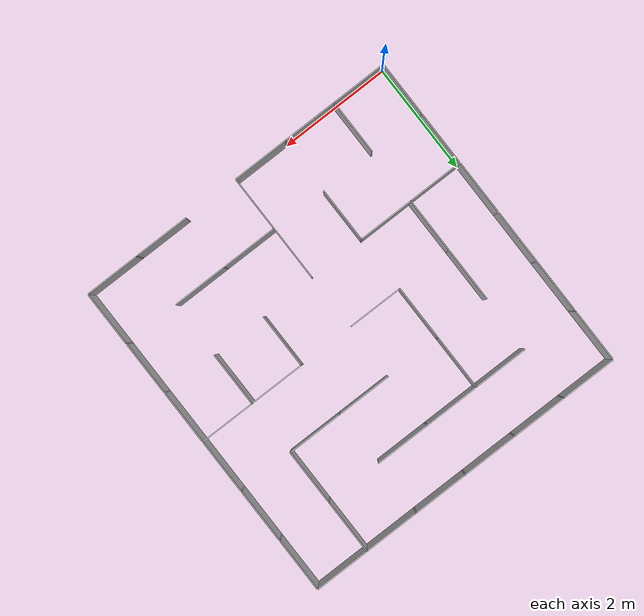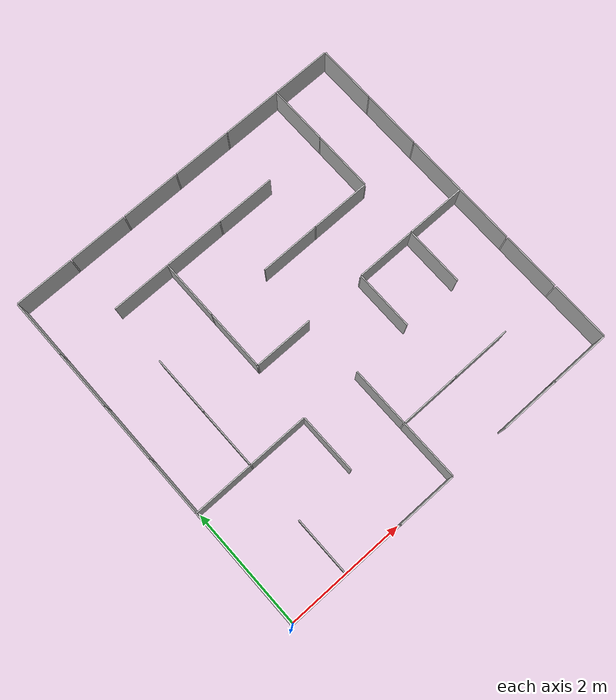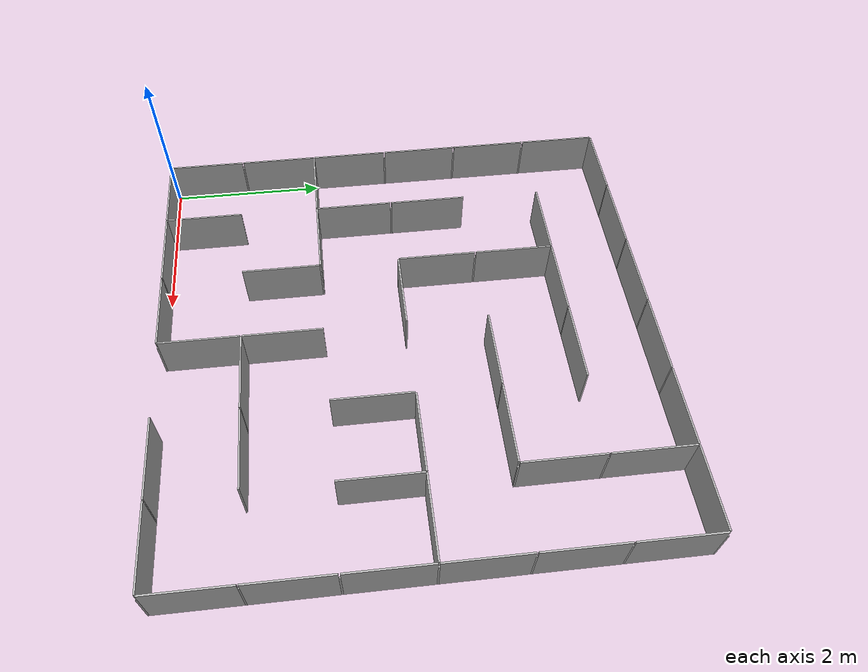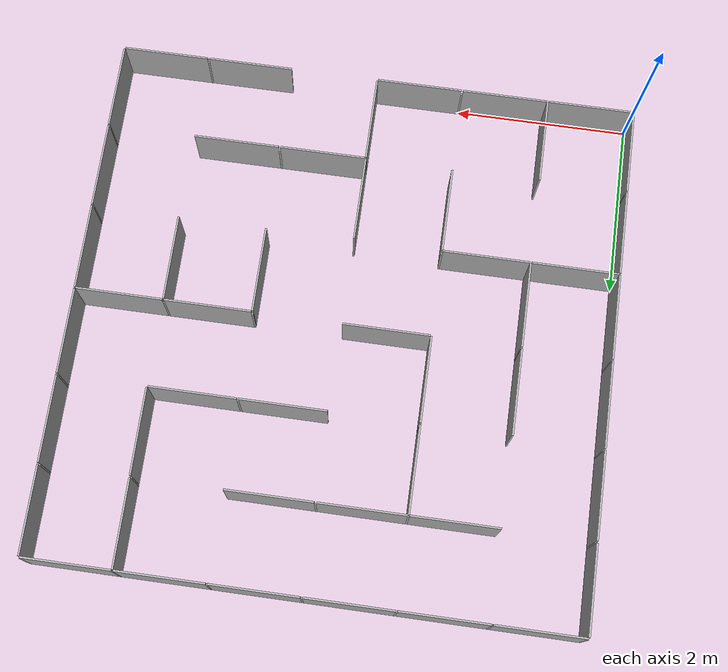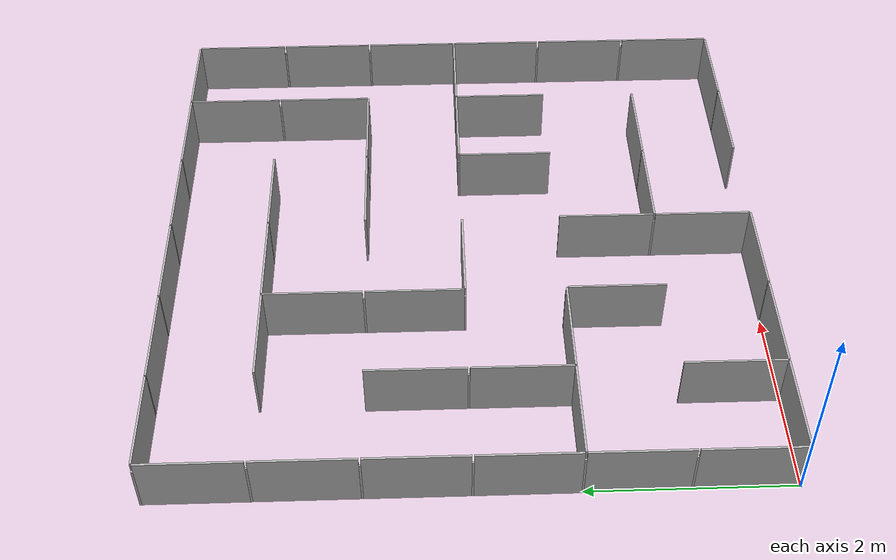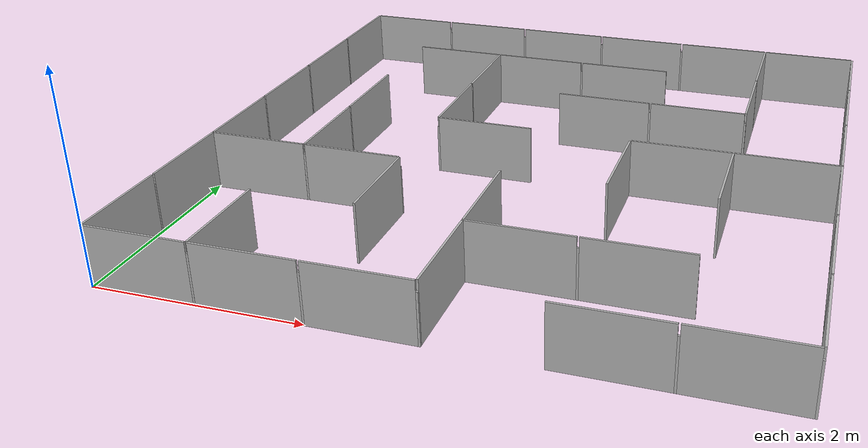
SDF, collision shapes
<?xml version='1.0'?>
<sdf version='1.7'>
  <model name='maze_midterm_validation'>
    <link name='metal_plate_0_0_b::main'>
      <pose>0 0 0 0 -0 1.571</pose>
      <self_collide>0</self_collide>
      <enable_wind>0</enable_wind>
      <kinematic>0</kinematic>
      <visual name='visual'>
        <pose>0.01 -0.01 0 3.14159 -1.57059 3.14159</pose>
        <geometry>
          <mesh>
            <scale>1 1 1</scale>
            <uri>model://metal_plate/meshes/metal_plate.dae</uri>
          </mesh>
        </geometry>
        <material>
          <shader type='pixel'/>
        </material>
        <transparency>0</transparency>
        <cast_shadows>1</cast_shadows>
      </visual>
      <collision name='collision'>
        <laser_retro>0</laser_retro>
        <max_contacts>10</max_contacts>
        <pose>0 -0.5 0.3 -1.571 -0 -1.571</pose>
        <geometry>
          <box>
            <size>0.98 0.6 0.02</size>
          </box>
        </geometry>
        <surface>
          <friction>
            <ode>
              <mu>1</mu>
              <mu2>1</mu2>
              <fdir1>0 0 0</fdir1>
              <slip1>0</slip1>
              <slip2>0</slip2>
            </ode>
            <torsional>
              <coefficient>1</coefficient>
              <patch_radius>0</patch_radius>
              <surface_radius>0</surface_radius>
              <use_patch_radius>1</use_patch_radius>
              <ode>
                <slip>0</slip>
              </ode>
            </torsional>
          </friction>
          <bounce>
            <restitution_coefficient>0</restitution_coefficient>
            <threshold>1e+06</threshold>
          </bounce>
          <contact>
            <collide_without_contact>0</collide_without_contact>
            <collide_without_contact_bitmask>1</collide_without_contact_bitmask>
            <collide_bitmask>1</collide_bitmask>
            <ode>
              <soft_cfm>0</soft_cfm>
              <soft_erp>0.2</soft_erp>
              <kp>1e+13</kp>
              <kd>1</kd>
              <max_vel>0.01</max_vel>
              <min_depth>0</min_depth>
            </ode>
            <bullet>
              <split_impulse>1</split_impulse>
              <split_impulse_penetration_threshold>-0.01</split_impulse_penetration_threshold>
              <soft_cfm>0</soft_cfm>
              <soft_erp>0.2</soft_erp>
              <kp>1e+13</kp>
              <kd>1</kd>
            </bullet>
          </contact>
        </surface>
      </collision>
    </link>
    <link name='metal_joint_0_0_b::link'>
      <pose>0 0 0.25 0 -0 0</pose>
      <self_collide>0</self_collide>
      <enable_wind>0</enable_wind>
      <kinematic>0</kinematic>
      <visual name='visual_metal_joint_0'>
        <pose>0 0 0 0 -0 0</pose>
        <geometry>
          <box>
            <size>0.02 0.02 0.5</size>
          </box>
        </geometry>
        <material>
          <script>
            <uri>model://metal_joint/materials/scripts</uri>
            <uri>model://metal_joint/materials/textures</uri>
            <name>metal_joint</name>
          </script>
          <shader type='pixel'/>
        </material>
        <transparency>0</transparency>
        <cast_shadows>1</cast_shadows>
      </visual>
      <collision name='metal_joint_01'>
        <laser_retro>0</laser_retro>
        <max_contacts>10</max_contacts>
        <pose>0 0 0 0 -0 0</pose>
        <geometry>
          <box>
            <size>0.02 0.02 0.5</size>
          </box>
        </geometry>
        <surface>
          <friction>
            <ode>
              <mu>1</mu>
              <mu2>1</mu2>
              <fdir1>0 0 0</fdir1>
              <slip1>0</slip1>
              <slip2>0</slip2>
            </ode>
            <torsional>
              <coefficient>1</coefficient>
              <patch_radius>0</patch_radius>
              <surface_radius>0</surface_radius>
              <use_patch_radius>1</use_patch_radius>
              <ode>
                <slip>0</slip>
              </ode>
            </torsional>
          </friction>
          <bounce>
            <restitution_coefficient>0</restitution_coefficient>
            <threshold>1e+06</threshold>
          </bounce>
          <contact>
            <collide_without_contact>0</collide_without_contact>
            <collide_without_contact_bitmask>1</collide_without_contact_bitmask>
            <collide_bitmask>1</collide_bitmask>
            <ode>
              <soft_cfm>0</soft_cfm>
              <soft_erp>0.2</soft_erp>
              <kp>1e+13</kp>
              <kd>1</kd>
              <max_vel>0.01</max_vel>
              <min_depth>0</min_depth>
            </ode>
            <bullet>
              <split_impulse>1</split_impulse>
              <split_impulse_penetration_threshold>-0.01</split_impulse_penetration_threshold>
              <soft_cfm>0</soft_cfm>
              <soft_erp>0.2</soft_erp>
              <kp>1e+13</kp>
              <kd>1</kd>
            </bullet>
          </contact>
        </surface>
      </collision>
    </link>
    <link name='metal_joint_0_1_a::link'>
      <pose>0 1 0.25 0 -0 0</pose>
      <self_collide>0</self_collide>
      <enable_wind>0</enable_wind>
      <kinematic>0</kinematic>
      <visual name='visual_metal_joint_0'>
        <pose>0 0 0 0 -0 0</pose>
        <geometry>
          <box>
            <size>0.02 0.02 0.5</size>
          </box>
        </geometry>
        <material>
          <script>
            <uri>model://metal_joint/materials/scripts</uri>
            <uri>model://metal_joint/materials/textures</uri>
            <name>metal_joint</name>
          </script>
          <shader type='pixel'/>
        </material>
        <transparency>0</transparency>
        <cast_shadows>1</cast_shadows>
      </visual>
      <collision name='metal_joint_01'>
        <laser_retro>0</laser_retro>
        <max_contacts>10</max_contacts>
        <pose>0 0 0 0 -0 0</pose>
        <geometry>
          <box>
            <size>0.02 0.02 0.5</size>
          </box>
        </geometry>
        <surface>
          <friction>
            <ode>
              <mu>1</mu>
              <mu2>1</mu2>
              <fdir1>0 0 0</fdir1>
              <slip1>0</slip1>
              <slip2>0</slip2>
            </ode>
            <torsional>
              <coefficient>1</coefficient>
              <patch_radius>0</patch_radius>
              <surface_radius>0</surface_radius>
              <use_patch_radius>1</use_patch_radius>
              <ode>
                <slip>0</slip>
              </ode>
            </torsional>
          </friction>
          <bounce>
            <restitution_coefficient>0</restitution_coefficient>
            <threshold>1e+06</threshold>
          </bounce>
          <contact>
            <collide_without_contact>0</collide_without_contact>
            <collide_without_contact_bitmask>1</collide_without_contact_bitmask>
            <collide_bitmask>1</collide_bitmask>
            <ode>
              <soft_cfm>0</soft_cfm>
              <soft_erp>0.2</soft_erp>
              <kp>1e+13</kp>
              <kd>1</kd>
              <max_vel>0.01</max_vel>
              <min_depth>0</min_depth>
            </ode>
            <bullet>
              <split_impulse>1</split_impulse>
              <split_impulse_penetration_threshold>-0.01</split_impulse_penetration_threshold>
              <soft_cfm>0</soft_cfm>
              <soft_erp>0.2</soft_erp>
              <kp>1e+13</kp>
              <kd>1</kd>
            </bullet>
          </contact>
        </surface>
      </collision>
    </link>
    <link name='metal_joint_0_2_a::link'>
      <pose>0 2 0.25 0 -0 0</pose>
      <self_collide>0</self_collide>
      <enable_wind>0</enable_wind>
      <kinematic>0</kinematic>
      <visual name='visual_metal_joint_0'>
        <pose>0 0 0 0 -0 0</pose>
        <geometry>
          <box>
            <size>0.02 0.02 0.5</size>
          </box>
        </geometry>
        <material>
          <script>
            <uri>model://metal_joint/materials/scripts</uri>
            <uri>model://metal_joint/materials/textures</uri>
            <name>metal_joint</name>
          </script>
          <shader type='pixel'/>
        </material>
        <transparency>0</transparency>
        <cast_shadows>1</cast_shadows>
      </visual>
      <collision name='metal_joint_01'>
        <laser_retro>0</laser_retro>
        <max_contacts>10</max_contacts>
        <pose>0 0 0 0 -0 0</pose>
        <geometry>
          <box>
            <size>0.02 0.02 0.5</size>
          </box>
        </geometry>
        <surface>
          <friction>
            <ode>
              <mu>1</mu>
              <mu2>1</mu2>
              <fdir1>0 0 0</fdir1>
              <slip1>0</slip1>
              <slip2>0</slip2>
            </ode>
            <torsional>
              <coefficient>1</coefficient>
              <patch_radius>0</patch_radius>
              <surface_radius>0</surface_radius>
              <use_patch_radius>1</use_patch_radius>
              <ode>
                <slip>0</slip>
              </ode>
            </torsional>
          </friction>
          <bounce>
            <restitution_coefficient>0</restitution_coefficient>
            <threshold>1e+06</threshold>
          </bounce>
          <contact>
            <collide_without_contact>0</collide_without_contact>
            <collide_without_contact_bitmask>1</collide_without_contact_bitmask>
            <collide_bitmask>1</collide_bitmask>
            <ode>
              <soft_cfm>0</soft_cfm>
              <soft_erp>0.2</soft_erp>
              <kp>1e+13</kp>
              <kd>1</kd>
              <max_vel>0.01</max_vel>
              <min_depth>0</min_depth>
            </ode>
            <bullet>
              <split_impulse>1</split_impulse>
              <split_impulse_penetration_threshold>-0.01</split_impulse_penetration_threshold>
              <soft_cfm>0</soft_cfm>
              <soft_erp>0.2</soft_erp>
              <kp>1e+13</kp>
              <kd>1</kd>
            </bullet>
          </contact>
        </surface>
      </collision>
    </link>
    <link name='metal_joint_0_3_a::link'>
      <pose>0 3 0.25 0 -0 0</pose>
      <self_collide>0</self_collide>
      <enable_wind>0</enable_wind>
      <kinematic>0</kinematic>
      <visual name='visual_metal_joint_0'>
        <pose>0 0 0 0 -0 0</pose>
        <geometry>
          <box>
            <size>0.02 0.02 0.5</size>
          </box>
        </geometry>
        <material>
          <script>
            <uri>model://metal_joint/materials/scripts</uri>
            <uri>model://metal_joint/materials/textures</uri>
            <name>metal_joint</name>
          </script>
          <shader type='pixel'/>
        </material>
        <transparency>0</transparency>
        <cast_shadows>1</cast_shadows>
      </visual>
      <collision name='metal_joint_01'>
        <laser_retro>0</laser_retro>
        <max_contacts>10</max_contacts>
        <pose>0 0 0 0 -0 0</pose>
        <geometry>
          <box>
            <size>0.02 0.02 0.5</size>
          </box>
        </geometry>
        <surface>
          <friction>
            <ode>
              <mu>1</mu>
              <mu2>1</mu2>
              <fdir1>0 0 0</fdir1>
              <slip1>0</slip1>
              <slip2>0</slip2>
            </ode>
            <torsional>
              <coefficient>1</coefficient>
              <patch_radius>0</patch_radius>
              <surface_radius>0</surface_radius>
              <use_patch_radius>1</use_patch_radius>
              <ode>
                <slip>0</slip>
              </ode>
            </torsional>
          </friction>
          <bounce>
            <restitution_coefficient>0</restitution_coefficient>
            <threshold>1e+06</threshold>
          </bounce>
          <contact>
            <collide_without_contact>0</collide_without_contact>
            <collide_without_contact_bitmask>1</collide_without_contact_bitmask>
            <collide_bitmask>1</collide_bitmask>
            <ode>
              <soft_cfm>0</soft_cfm>
              <soft_erp>0.2</soft_erp>
              <kp>1e+13</kp>
              <kd>1</kd>
              <max_vel>0.01</max_vel>
              <min_depth>0</min_depth>
            </ode>
            <bullet>
              <split_impulse>1</split_impulse>
              <split_impulse_penetration_threshold>-0.01</split_impulse_penetration_threshold>
              <soft_cfm>0</soft_cfm>
              <soft_erp>0.2</soft_erp>
              <kp>1e+13</kp>
              <kd>1</kd>
            </bullet>
          </contact>
        </surface>
      </collision>
    </link>
    <link name='metal_joint_0_4_a::link'>
      <pose>0 4 0.25 0 -0 0</pose>
      <self_collide>0</self_collide>
      <enable_wind>0</enable_wind>
      <kinematic>0</kinematic>
      <visual name='visual_metal_joint_0'>
        <pose>0 0 0 0 -0 0</pose>
        <geometry>
          <box>
            <size>0.02 0.02 0.5</size>
          </box>
        </geometry>
        <material>
          <script>
            <uri>model://metal_joint/materials/scripts</uri>
            <uri>model://metal_joint/materials/textures</uri>
            <name>metal_joint</name>
          </script>
          <shader type='pixel'/>
        </material>
        <transparency>0</transparency>
        <cast_shadows>1</cast_shadows>
      </visual>
      <collision name='metal_joint_01'>
        <laser_retro>0</laser_retro>
        <max_contacts>10</max_contacts>
        <pose>0 0 0 0 -0 0</pose>
        <geometry>
          <box>
            <size>0.02 0.02 0.5</size>
          </box>
        </geometry>
        <surface>
          <friction>
            <ode>
              <mu>1</mu>
              <mu2>1</mu2>
              <fdir1>0 0 0</fdir1>
              <slip1>0</slip1>
              <slip2>0</slip2>
            </ode>
            <torsional>
              <coefficient>1</coefficient>
              <patch_radius>0</patch_radius>
              <surface_radius>0</surface_radius>
              <use_patch_radius>1</use_patch_radius>
              <ode>
                <slip>0</slip>
              </ode>
            </torsional>
          </friction>
          <bounce>
            <restitution_coefficient>0</restitution_coefficient>
            <threshold>1e+06</threshold>
          </bounce>
          <contact>
            <collide_without_contact>0</collide_without_contact>
            <collide_without_contact_bitmask>1</collide_without_contact_bitmask>
            <collide_bitmask>1</collide_bitmask>
            <ode>
              <soft_cfm>0</soft_cfm>
              <soft_erp>0.2</soft_erp>
              <kp>1e+13</kp>
              <kd>1</kd>
              <max_vel>0.01</max_vel>
              <min_depth>0</min_depth>
            </ode>
            <bullet>
              <split_impulse>1</split_impulse>
              <split_impulse_penetration_threshold>-0.01</split_impulse_penetration_threshold>
              <soft_cfm>0</soft_cfm>
              <soft_erp>0.2</soft_erp>
              <kp>1e+13</kp>
              <kd>1</kd>
            </bullet>
          </contact>
        </surface>
      </collision>
    </link>
    <link name='metal_joint_0_5_a::link'>
      <pose>0 5 0.25 0 -0 0</pose>
      <self_collide>0</self_collide>
      <enable_wind>0</enable_wind>
      <kinematic>0</kinematic>
      <visual name='visual_metal_joint_0'>
        <pose>0 0 0 0 -0 0</pose>
        <geometry>
          <box>
            <size>0.02 0.02 0.5</size>
          </box>
        </geometry>
        <material>
          <script>
            <uri>model://metal_joint/materials/scripts</uri>
            <uri>model://metal_joint/materials/textures</uri>
            <name>metal_joint</name>
          </script>
          <shader type='pixel'/>
        </material>
        <transparency>0</transparency>
        <cast_shadows>1</cast_shadows>
      </visual>
      <collision name='metal_joint_01'>
        <laser_retro>0</laser_retro>
        <max_contacts>10</max_contacts>
        <pose>0 0 0 0 -0 0</pose>
        <geometry>
          <box>
            <size>0.02 0.02 0.5</size>
          </box>
        </geometry>
        <surface>
          <friction>
            <ode>
              <mu>1</mu>
              <mu2>1</mu2>
              <fdir1>0 0 0</fdir1>
              <slip1>0</slip1>
              <slip2>0</slip2>
            </ode>
            <torsional>
              <coefficient>1</coefficient>
              <patch_radius>0</patch_radius>
              <surface_radius>0</surface_radius>
              <use_patch_radius>1</use_patch_radius>
              <ode>
                <slip>0</slip>
              </ode>
            </torsional>
          </friction>
          <bounce>
            <restitution_coefficient>0</restitution_coefficient>
            <threshold>1e+06</threshold>
          </bounce>
          <contact>
            <collide_without_contact>0</collide_without_contact>
            <collide_without_contact_bitmask>1</collide_without_contact_bitmask>
            <collide_bitmask>1</collide_bitmask>
            <ode>
              <soft_cfm>0</soft_cfm>
              <soft_erp>0.2</soft_erp>
              <kp>1e+13</kp>
              <kd>1</kd>
              <max_vel>0.01</max_vel>
              <min_depth>0</min_depth>
            </ode>
            <bullet>
              <split_impulse>1</split_impulse>
              <split_impulse_penetration_threshold>-0.01</split_impulse_penetration_threshold>
              <soft_cfm>0</soft_cfm>
              <soft_erp>0.2</soft_erp>
              <kp>1e+13</kp>
              <kd>1</kd>
            </bullet>
          </contact>
        </surface>
      </collision>
    </link>
    <link name='metal_joint_0_6_b::link'>
      <pose>0 6 0.25 0 -0 0</pose>
      <self_collide>0</self_collide>
      <enable_wind>0</enable_wind>
      <kinematic>0</kinematic>
      <visual name='visual_metal_joint_0'>
        <pose>0 0 0 0 -0 0</pose>
        <geometry>
          <box>
            <size>0.02 0.02 0.5</size>
          </box>
        </geometry>
        <material>
          <script>
            <uri>model://metal_joint/materials/scripts</uri>
            <uri>model://metal_joint/materials/textures</uri>
            <name>metal_joint</name>
          </script>
          <shader type='pixel'/>
        </material>
        <transparency>0</transparency>
        <cast_shadows>1</cast_shadows>
      </visual>
      <collision name='metal_joint_01'>
        <laser_retro>0</laser_retro>
        <max_contacts>10</max_contacts>
        <pose>0 0 0 0 -0 0</pose>
        <geometry>
          <box>
            <size>0.02 0.02 0.5</size>
          </box>
        </geometry>
        <surface>
          <friction>
            <ode>
              <mu>1</mu>
              <mu2>1</mu2>
              <fdir1>0 0 0</fdir1>
              <slip1>0</slip1>
              <slip2>0</slip2>
            </ode>
            <torsional>
              <coefficient>1</coefficient>
              <patch_radius>0</patch_radius>
              <surface_radius>0</surface_radius>
              <use_patch_radius>1</use_patch_radius>
              <ode>
                <slip>0</slip>
              </ode>
            </torsional>
          </friction>
          <bounce>
            <restitution_coefficient>0</restitution_coefficient>
            <threshold>1e+06</threshold>
          </bounce>
          <contact>
            <collide_without_contact>0</collide_without_contact>
            <collide_without_contact_bitmask>1</collide_without_contact_bitmask>
            <collide_bitmask>1</collide_bitmask>
            <ode>
              <soft_cfm>0</soft_cfm>
              <soft_erp>0.2</soft_erp>
              <kp>1e+13</kp>
              <kd>1</kd>
              <max_vel>0.01</max_vel>
              <min_depth>0</min_depth>
            </ode>
            <bullet>
              <split_impulse>1</split_impulse>
              <split_impulse_penetration_threshold>-0.01</split_impulse_penetration_threshold>
              <soft_cfm>0</soft_cfm>
              <soft_erp>0.2</soft_erp>
              <kp>1e+13</kp>
              <kd>1</kd>
            </bullet>
          </contact>
        </surface>
      </collision>
    </link>
    <link name='metal_joint_1_0_b::link'>
      <pose>1 0 0.25 0 -0 0</pose>
      <self_collide>0</self_collide>
      <enable_wind>0</enable_wind>
      <kinematic>0</kinematic>
      <visual name='visual_metal_joint_0'>
        <pose>0 0 0 0 -0 0</pose>
        <geometry>
          <box>
            <size>0.02 0.02 0.5</size>
          </box>
        </geometry>
        <material>
          <script>
            <uri>model://metal_joint/materials/scripts</uri>
            <uri>model://metal_joint/materials/textures</uri>
            <name>metal_joint</name>
          </script>
          <shader type='pixel'/>
        </material>
        <transparency>0</transparency>
        <cast_shadows>1</cast_shadows>
      </visual>
      <collision name='metal_joint_01'>
        <laser_retro>0</laser_retro>
        <max_contacts>10</max_contacts>
        <pose>0 0 0 0 -0 0</pose>
        <geometry>
          <box>
            <size>0.02 0.02 0.5</size>
          </box>
        </geometry>
        <surface>
          <friction>
            <ode>
              <mu>1</mu>
              <mu2>1</mu2>
              <fdir1>0 0 0</fdir1>
              <slip1>0</slip1>
              <slip2>0</slip2>
            </ode>
            <torsional>
              <coefficient>1</coefficient>
              <patch_radius>0</patch_radius>
              <surface_radius>0</surface_radius>
              <use_patch_radius>1</use_patch_radius>
              <ode>
                <slip>0</slip>
              </ode>
            </torsional>
          </friction>
          <bounce>
            <restitution_coefficient>0</restitution_coefficient>
            <threshold>1e+06</threshold>
          </bounce>
          <contact>
            <collide_without_contact>0</collide_without_contact>
            <collide_without_contact_bitmask>1</collide_without_contact_bitmask>
            <collide_bitmask>1</collide_bitmask>
            <ode>
              <soft_cfm>0</soft_cfm>
              <soft_erp>0.2</soft_erp>
              <kp>1e+13</kp>
              <kd>1</kd>
              <max_vel>0.01</max_vel>
              <min_depth>0</min_depth>
            </ode>
            <bullet>
              <split_impulse>1</split_impulse>
              <split_impulse_penetration_threshold>-0.01</split_impulse_penetration_threshold>
              <soft_cfm>0</soft_cfm>
              <soft_erp>0.2</soft_erp>
              <kp>1e+13</kp>
              <kd>1</kd>
            </bullet>
          </contact>
        </surface>
      </collision>
    </link>
    <link name='metal_joint_1_2::link'>
      <pose>1 2 0.25 0 -0 0</pose>
      <self_collide>0</self_collide>
      <enable_wind>0</enable_wind>
      <kinematic>0</kinematic>
      <visual name='visual_metal_joint_0'>
        <pose>0 0 0 0 -0 0</pose>
        <geometry>
          <box>
            <size>0.02 0.02 0.5</size>
          </box>
        </geometry>
        <material>
          <script>
            <uri>model://metal_joint/materials/scripts</uri>
            <uri>model://metal_joint/materials/textures</uri>
            <name>metal_joint</name>
          </script>
          <shader type='pixel'/>
        </material>
        <transparency>0</transparency>
        <cast_shadows>1</cast_shadows>
      </visual>
      <collision name='metal_joint_01'>
        <laser_retro>0</laser_retro>
        <max_contacts>10</max_contacts>
        <pose>0 0 0 0 -0 0</pose>
        <geometry>
          <box>
            <size>0.02 0.02 0.5</size>
          </box>
        </geometry>
        <surface>
          <friction>
            <ode>
              <mu>1</mu>
              <mu2>1</mu2>
              <fdir1>0 0 0</fdir1>
              <slip1>0</slip1>
              <slip2>0</slip2>
            </ode>
            <torsional>
              <coefficient>1</coefficient>
              <patch_radius>0</patch_radius>
              <surface_radius>0</surface_radius>
              <use_patch_radius>1</use_patch_radius>
              <ode>
                <slip>0</slip>
              </ode>
            </torsional>
          </friction>
          <bounce>
            <restitution_coefficient>0</restitution_coefficient>
            <threshold>1e+06</threshold>
          </bounce>
          <contact>
            <collide_without_contact>0</collide_without_contact>
            <collide_without_contact_bitmask>1</collide_without_contact_bitmask>
            <collide_bitmask>1</collide_bitmask>
            <ode>
              <soft_cfm>0</soft_cfm>
              <soft_erp>0.2</soft_erp>
              <kp>1e+13</kp>
              <kd>1</kd>
              <max_vel>0.01</max_vel>
              <min_depth>0</min_depth>
            </ode>
            <bullet>
              <split_impulse>1</split_impulse>
              <split_impulse_penetration_threshold>-0.01</split_impulse_penetration_threshold>
              <soft_cfm>0</soft_cfm>
              <soft_erp>0.2</soft_erp>
              <kp>1e+13</kp>
              <kd>1</kd>
            </bullet>
          </contact>
        </surface>
      </collision>
    </link>
    <link name='metal_joint_1_3::link'>
      <pose>1 3 0.25 0 -0 0</pose>
      <self_collide>0</self_collide>
      <enable_wind>0</enable_wind>
      <kinematic>0</kinematic>
      <visual name='visual_metal_joint_0'>
        <pose>0 0 0 0 -0 0</pose>
        <geometry>
          <box>
            <size>0.02 0.02 0.5</size>
          </box>
        </geometry>
        <material>
          <script>
            <uri>model://metal_joint/materials/scripts</uri>
            <uri>model://metal_joint/materials/textures</uri>
            <name>metal_joint</name>
          </script>
          <shader type='pixel'/>
        </material>
        <transparency>0</transparency>
        <cast_shadows>1</cast_shadows>
      </visual>
      <collision name='metal_joint_01'>
        <laser_retro>0</laser_retro>
        <max_contacts>10</max_contacts>
        <pose>0 0 0 0 -0 0</pose>
        <geometry>
          <box>
            <size>0.02 0.02 0.5</size>
          </box>
        </geometry>
        <surface>
          <friction>
            <ode>
              <mu>1</mu>
              <mu2>1</mu2>
              <fdir1>0 0 0</fdir1>
              <slip1>0</slip1>
              <slip2>0</slip2>
            </ode>
            <torsional>
              <coefficient>1</coefficient>
              <patch_radius>0</patch_radius>
              <surface_radius>0</surface_radius>
              <use_patch_radius>1</use_patch_radius>
              <ode>
                <slip>0</slip>
              </ode>
            </torsional>
          </friction>
          <bounce>
            <restitution_coefficient>0</restitution_coefficient>
            <threshold>1e+06</threshold>
          </bounce>
          <contact>
            <collide_without_contact>0</collide_without_contact>
            <collide_without_contact_bitmask>1</collide_without_contact_bitmask>
            <collide_bitmask>1</collide_bitmask>
            <ode>
              <soft_cfm>0</soft_cfm>
              <soft_erp>0.2</soft_erp>
              <kp>1e+13</kp>
              <kd>1</kd>
              <max_vel>0.01</max_vel>
              <min_depth>0</min_depth>
            </ode>
            <bullet>
              <split_impulse>1</split_impulse>
              <split_impulse_penetration_threshold>-0.01</split_impulse_penetration_threshold>
              <soft_cfm>0</soft_cfm>
              <soft_erp>0.2</soft_erp>
              <kp>1e+13</kp>
              <kd>1</kd>
            </bullet>
          </contact>
        </surface>
      </collision>
    </link>
    <link name='metal_joint_1_6_b::link'>
      <pose>1 6 0.25 0 -0 0</pose>
      <self_collide>0</self_collide>
      <enable_wind>0</enable_wind>
      <kinematic>0</kinematic>
      <visual name='visual_metal_joint_0'>
        <pose>0 0 0 0 -0 0</pose>
        <geometry>
          <box>
            <size>0.02 0.02 0.5</size>
          </box>
        </geometry>
        <material>
          <script>
            <uri>model://metal_joint/materials/scripts</uri>
            <uri>model://metal_joint/materials/textures</uri>
            <name>metal_joint</name>
          </script>
          <shader type='pixel'/>
        </material>
        <transparency>0</transparency>
        <cast_shadows>1</cast_shadows>
      </visual>
      <collision name='metal_joint_01'>
        <laser_retro>0</laser_retro>
        <max_contacts>10</max_contacts>
        <pose>0 0 0 0 -0 0</pose>
        <geometry>
          <box>
            <size>0.02 0.02 0.5</size>
          </box>
        </geometry>
        <surface>
          <friction>
            <ode>
              <mu>1</mu>
              <mu2>1</mu2>
              <fdir1>0 0 0</fdir1>
              <slip1>0</slip1>
              <slip2>0</slip2>
            </ode>
            <torsional>
              <coefficient>1</coefficient>
              <patch_radius>0</patch_radius>
              <surface_radius>0</surface_radius>
              <use_patch_radius>1</use_patch_radius>
              <ode>
                <slip>0</slip>
              </ode>
            </torsional>
          </friction>
          <bounce>
            <restitution_coefficient>0</restitution_coefficient>
            <threshold>1e+06</threshold>
          </bounce>
          <contact>
            <collide_without_contact>0</collide_without_contact>
            <collide_without_contact_bitmask>1</collide_without_contact_bitmask>
            <collide_bitmask>1</collide_bitmask>
            <ode>
              <soft_cfm>0</soft_cfm>
              <soft_erp>0.2</soft_erp>
              <kp>1e+13</kp>
              <kd>1</kd>
              <max_vel>0.01</max_vel>
              <min_depth>0</min_depth>
            </ode>
            <bullet>
              <split_impulse>1</split_impulse>
              <split_impulse_penetration_threshold>-0.01</split_impulse_penetration_threshold>
              <soft_cfm>0</soft_cfm>
              <soft_erp>0.2</soft_erp>
              <kp>1e+13</kp>
              <kd>1</kd>
            </bullet>
          </contact>
        </surface>
      </collision>
    </link>
    <link name='metal_joint_2_0_b::link'>
      <pose>2 0 0.25 0 -0 0</pose>
      <self_collide>0</self_collide>
      <enable_wind>0</enable_wind>
      <kinematic>0</kinematic>
      <visual name='visual_metal_joint_0'>
        <pose>0 0 0 0 -0 0</pose>
        <geometry>
          <box>
            <size>0.02 0.02 0.5</size>
          </box>
        </geometry>
        <material>
          <script>
            <uri>model://metal_joint/materials/scripts</uri>
            <uri>model://metal_joint/materials/textures</uri>
            <name>metal_joint</name>
          </script>
          <shader type='pixel'/>
        </material>
        <transparency>0</transparency>
        <cast_shadows>1</cast_shadows>
      </visual>
      <collision name='metal_joint_01'>
        <laser_retro>0</laser_retro>
        <max_contacts>10</max_contacts>
        <pose>0 0 0 0 -0 0</pose>
        <geometry>
          <box>
            <size>0.02 0.02 0.5</size>
          </box>
        </geometry>
        <surface>
          <friction>
            <ode>
              <mu>1</mu>
              <mu2>1</mu2>
              <fdir1>0 0 0</fdir1>
              <slip1>0</slip1>
              <slip2>0</slip2>
            </ode>
            <torsional>
              <coefficient>1</coefficient>
              <patch_radius>0</patch_radius>
              <surface_radius>0</surface_radius>
              <use_patch_radius>1</use_patch_radius>
              <ode>
                <slip>0</slip>
              </ode>
            </torsional>
          </friction>
          <bounce>
            <restitution_coefficient>0</restitution_coefficient>
            <threshold>1e+06</threshold>
          </bounce>
          <contact>
            <collide_without_contact>0</collide_without_contact>
            <collide_without_contact_bitmask>1</collide_without_contact_bitmask>
            <collide_bitmask>1</collide_bitmask>
            <ode>
              <soft_cfm>0</soft_cfm>
              <soft_erp>0.2</soft_erp>
              <kp>1e+13</kp>
              <kd>1</kd>
              <max_vel>0.01</max_vel>
              <min_depth>0</min_depth>
            </ode>
            <bullet>
              <split_impulse>1</split_impulse>
              <split_impulse_penetration_threshold>-0.01</split_impulse_penetration_threshold>
              <soft_cfm>0</soft_cfm>
              <soft_erp>0.2</soft_erp>
              <kp>1e+13</kp>
              <kd>1</kd>
            </bullet>
          </contact>
        </surface>
      </collision>
    </link>
    <link name='metal_joint_2_2::link'>
      <pose>2 2 0.25 0 -0 0</pose>
      <self_collide>0</self_collide>
      <enable_wind>0</enable_wind>
      <kinematic>0</kinematic>
      <visual name='visual_metal_joint_0'>
        <pose>0 0 0 0 -0 0</pose>
        <geometry>
          <box>
            <size>0.02 0.02 0.5</size>
          </box>
        </geometry>
        <material>
          <script>
            <uri>model://metal_joint/materials/scripts</uri>
            <uri>model://metal_joint/materials/textures</uri>
            <name>metal_joint</name>
          </script>
          <shader type='pixel'/>
        </material>
        <transparency>0</transparency>
        <cast_shadows>1</cast_shadows>
      </visual>
      <collision name='metal_joint_01'>
        <laser_retro>0</laser_retro>
        <max_contacts>10</max_contacts>
        <pose>0 0 0 0 -0 0</pose>
        <geometry>
          <box>
            <size>0.02 0.02 0.5</size>
          </box>
        </geometry>
        <surface>
          <friction>
            <ode>
              <mu>1</mu>
              <mu2>1</mu2>
              <fdir1>0 0 0</fdir1>
              <slip1>0</slip1>
              <slip2>0</slip2>
            </ode>
            <torsional>
              <coefficient>1</coefficient>
              <patch_radius>0</patch_radius>
              <surface_radius>0</surface_radius>
              <use_patch_radius>1</use_patch_radius>
              <ode>
                <slip>0</slip>
              </ode>
            </torsional>
          </friction>
          <bounce>
            <restitution_coefficient>0</restitution_coefficient>
            <threshold>1e+06</threshold>
          </bounce>
          <contact>
            <collide_without_contact>0</collide_without_contact>
            <collide_without_contact_bitmask>1</collide_without_contact_bitmask>
            <collide_bitmask>1</collide_bitmask>
            <ode>
              <soft_cfm>0</soft_cfm>
              <soft_erp>0.2</soft_erp>
              <kp>1e+13</kp>
              <kd>1</kd>
              <max_vel>0.01</max_vel>
              <min_depth>0</min_depth>
            </ode>
            <bullet>
              <split_impulse>1</split_impulse>
              <split_impulse_penetration_threshold>-0.01</split_impulse_penetration_threshold>
              <soft_cfm>0</soft_cfm>
              <soft_erp>0.2</soft_erp>
              <kp>1e+13</kp>
              <kd>1</kd>
            </bullet>
          </contact>
        </surface>
      </collision>
    </link>
    <link name='metal_joint_2_3::link'>
      <pose>2 3 0.25 0 -0 0</pose>
      <self_collide>0</self_collide>
      <enable_wind>0</enable_wind>
      <kinematic>0</kinematic>
      <visual name='visual_metal_joint_0'>
        <pose>0 0 0 0 -0 0</pose>
        <geometry>
          <box>
            <size>0.02 0.02 0.5</size>
          </box>
        </geometry>
        <material>
          <script>
            <uri>model://metal_joint/materials/scripts</uri>
            <uri>model://metal_joint/materials/textures</uri>
            <name>metal_joint</name>
          </script>
          <shader type='pixel'/>
        </material>
        <transparency>0</transparency>
        <cast_shadows>1</cast_shadows>
      </visual>
      <collision name='metal_joint_01'>
        <laser_retro>0</laser_retro>
        <max_contacts>10</max_contacts>
        <pose>0 0 0 0 -0 0</pose>
        <geometry>
          <box>
            <size>0.02 0.02 0.5</size>
          </box>
        </geometry>
        <surface>
          <friction>
            <ode>
              <mu>1</mu>
              <mu2>1</mu2>
              <fdir1>0 0 0</fdir1>
              <slip1>0</slip1>
              <slip2>0</slip2>
            </ode>
            <torsional>
              <coefficient>1</coefficient>
              <patch_radius>0</patch_radius>
              <surface_radius>0</surface_radius>
              <use_patch_radius>1</use_patch_radius>
              <ode>
                <slip>0</slip>
              </ode>
            </torsional>
          </friction>
          <bounce>
            <restitution_coefficient>0</restitution_coefficient>
            <threshold>1e+06</threshold>
          </bounce>
          <contact>
            <collide_without_contact>0</collide_without_contact>
            <collide_without_contact_bitmask>1</collide_without_contact_bitmask>
            <collide_bitmask>1</collide_bitmask>
            <ode>
              <soft_cfm>0</soft_cfm>
              <soft_erp>0.2</soft_erp>
              <kp>1e+13</kp>
              <kd>1</kd>
              <max_vel>0.01</max_vel>
              <min_depth>0</min_depth>
            </ode>
            <bullet>
              <split_impulse>1</split_impulse>
              <split_impulse_penetration_threshold>-0.01</split_impulse_penetration_threshold>
              <soft_cfm>0</soft_cfm>
              <soft_erp>0.2</soft_erp>
              <kp>1e+13</kp>
              <kd>1</kd>
            </bullet>
          </contact>
        </surface>
      </collision>
    </link>
    <link name='metal_joint_2_4::link'>
      <pose>2 4 0.25 0 -0 0</pose>
      <self_collide>0</self_collide>
      <enable_wind>0</enable_wind>
      <kinematic>0</kinematic>
      <visual name='visual_metal_joint_0'>
        <pose>0 0 0 0 -0 0</pose>
        <geometry>
          <box>
            <size>0.02 0.02 0.5</size>
          </box>
        </geometry>
        <material>
          <script>
            <uri>model://metal_joint/materials/scripts</uri>
            <uri>model://metal_joint/materials/textures</uri>
            <name>metal_joint</name>
          </script>
          <shader type='pixel'/>
        </material>
        <transparency>0</transparency>
        <cast_shadows>1</cast_shadows>
      </visual>
      <collision name='metal_joint_01'>
        <laser_retro>0</laser_retro>
        <max_contacts>10</max_contacts>
        <pose>0 0 0 0 -0 0</pose>
        <geometry>
          <box>
            <size>0.02 0.02 0.5</size>
          </box>
        </geometry>
        <surface>
          <friction>
            <ode>
              <mu>1</mu>
              <mu2>1</mu2>
              <fdir1>0 0 0</fdir1>
              <slip1>0</slip1>
              <slip2>0</slip2>
            </ode>
            <torsional>
              <coefficient>1</coefficient>
              <patch_radius>0</patch_radius>
              <surface_radius>0</surface_radius>
              <use_patch_radius>1</use_patch_radius>
              <ode>
                <slip>0</slip>
              </ode>
            </torsional>
          </friction>
          <bounce>
            <restitution_coefficient>0</restitution_coefficient>
            <threshold>1e+06</threshold>
          </bounce>
          <contact>
            <collide_without_contact>0</collide_without_contact>
            <collide_without_contact_bitmask>1</collide_without_contact_bitmask>
            <collide_bitmask>1</collide_bitmask>
            <ode>
              <soft_cfm>0</soft_cfm>
              <soft_erp>0.2</soft_erp>
              <kp>1e+13</kp>
              <kd>1</kd>
              <max_vel>0.01</max_vel>
              <min_depth>0</min_depth>
            </ode>
            <bullet>
              <split_impulse>1</split_impulse>
              <split_impulse_penetration_threshold>-0.01</split_impulse_penetration_threshold>
              <soft_cfm>0</soft_cfm>
              <soft_erp>0.2</soft_erp>
              <kp>1e+13</kp>
              <kd>1</kd>
            </bullet>
          </contact>
        </surface>
      </collision>
    </link>
    <link name='metal_joint_2_5::link'>
      <pose>2 5 0.25 0 -0 0</pose>
      <self_collide>0</self_collide>
      <enable_wind>0</enable_wind>
      <kinematic>0</kinematic>
      <visual name='visual_metal_joint_0'>
        <pose>0 0 0 0 -0 0</pose>
        <geometry>
          <box>
            <size>0.02 0.02 0.5</size>
          </box>
        </geometry>
        <material>
          <script>
            <uri>model://metal_joint/materials/scripts</uri>
            <uri>model://metal_joint/materials/textures</uri>
            <name>metal_joint</name>
          </script>
          <shader type='pixel'/>
        </material>
        <transparency>0</transparency>
        <cast_shadows>1</cast_shadows>
      </visual>
      <collision name='metal_joint_01'>
        <laser_retro>0</laser_retro>
        <max_contacts>10</max_contacts>
        <pose>0 0 0 0 -0 0</pose>
        <geometry>
          <box>
            <size>0.02 0.02 0.5</size>
          </box>
        </geometry>
        <surface>
          <friction>
            <ode>
              <mu>1</mu>
              <mu2>1</mu2>
              <fdir1>0 0 0</fdir1>
              <slip1>0</slip1>
              <slip2>0</slip2>
            </ode>
            <torsional>
              <coefficient>1</coefficient>
              <patch_radius>0</patch_radius>
              <surface_radius>0</surface_radius>
              <use_patch_radius>1</use_patch_radius>
              <ode>
                <slip>0</slip>
              </ode>
            </torsional>
          </friction>
          <bounce>
            <restitution_coefficient>0</restitution_coefficient>
            <threshold>1e+06</threshold>
          </bounce>
          <contact>
            <collide_without_contact>0</collide_without_contact>
            <collide_without_contact_bitmask>1</collide_without_contact_bitmask>
            <collide_bitmask>1</collide_bitmask>
            <ode>
              <soft_cfm>0</soft_cfm>
              <soft_erp>0.2</soft_erp>
              <kp>1e+13</kp>
              <kd>1</kd>
              <max_vel>0.01</max_vel>
              <min_depth>0</min_depth>
            </ode>
            <bullet>
              <split_impulse>1</split_impulse>
              <split_impulse_penetration_threshold>-0.01</split_impulse_penetration_threshold>
              <soft_cfm>0</soft_cfm>
              <soft_erp>0.2</soft_erp>
              <kp>1e+13</kp>
              <kd>1</kd>
            </bullet>
          </contact>
        </surface>
      </collision>
    </link>
    <link name='metal_joint_2_6_b::link'>
      <pose>2 6 0.25 0 -0 0</pose>
      <self_collide>0</self_collide>
      <enable_wind>0</enable_wind>
      <kinematic>0</kinematic>
      <visual name='visual_metal_joint_0'>
        <pose>0 0 0 0 -0 0</pose>
        <geometry>
          <box>
            <size>0.02 0.02 0.5</size>
          </box>
        </geometry>
        <material>
          <script>
            <uri>model://metal_joint/materials/scripts</uri>
            <uri>model://metal_joint/materials/textures</uri>
            <name>metal_joint</name>
          </script>
          <shader type='pixel'/>
        </material>
        <transparency>0</transparency>
        <cast_shadows>1</cast_shadows>
      </visual>
      <collision name='metal_joint_01'>
        <laser_retro>0</laser_retro>
        <max_contacts>10</max_contacts>
        <pose>0 0 0 0 -0 0</pose>
        <geometry>
          <box>
            <size>0.02 0.02 0.5</size>
          </box>
        </geometry>
        <surface>
          <friction>
            <ode>
              <mu>1</mu>
              <mu2>1</mu2>
              <fdir1>0 0 0</fdir1>
              <slip1>0</slip1>
              <slip2>0</slip2>
            </ode>
            <torsional>
              <coefficient>1</coefficient>
              <patch_radius>0</patch_radius>
              <surface_radius>0</surface_radius>
              <use_patch_radius>1</use_patch_radius>
              <ode>
                <slip>0</slip>
              </ode>
            </torsional>
          </friction>
          <bounce>
            <restitution_coefficient>0</restitution_coefficient>
            <threshold>1e+06</threshold>
          </bounce>
          <contact>
            <collide_without_contact>0</collide_without_contact>
            <collide_without_contact_bitmask>1</collide_without_contact_bitmask>
            <collide_bitmask>1</collide_bitmask>
            <ode>
              <soft_cfm>0</soft_cfm>
              <soft_erp>0.2</soft_erp>
              <kp>1e+13</kp>
              <kd>1</kd>
              <max_vel>0.01</max_vel>
              <min_depth>0</min_depth>
            </ode>
            <bullet>
              <split_impulse>1</split_impulse>
              <split_impulse_penetration_threshold>-0.01</split_impulse_penetration_threshold>
              <soft_cfm>0</soft_cfm>
              <soft_erp>0.2</soft_erp>
              <kp>1e+13</kp>
              <kd>1</kd>
            </bullet>
          </contact>
        </surface>
      </collision>
    </link>
    <link name='metal_joint_3_0_b::link'>
      <pose>3 0 0.25 0 -0 0</pose>
      <self_collide>0</self_collide>
      <enable_wind>0</enable_wind>
      <kinematic>0</kinematic>
      <visual name='visual_metal_joint_0'>
        <pose>0 0 0 0 -0 0</pose>
        <geometry>
          <box>
            <size>0.02 0.02 0.5</size>
          </box>
        </geometry>
        <material>
          <script>
            <uri>model://metal_joint/materials/scripts</uri>
            <uri>model://metal_joint/materials/textures</uri>
            <name>metal_joint</name>
          </script>
          <shader type='pixel'/>
        </material>
        <transparency>0</transparency>
        <cast_shadows>1</cast_shadows>
      </visual>
      <collision name='metal_joint_01'>
        <laser_retro>0</laser_retro>
        <max_contacts>10</max_contacts>
        <pose>0 0 0 0 -0 0</pose>
        <geometry>
          <box>
            <size>0.02 0.02 0.5</size>
          </box>
        </geometry>
        <surface>
          <friction>
            <ode>
              <mu>1</mu>
              <mu2>1</mu2>
              <fdir1>0 0 0</fdir1>
              <slip1>0</slip1>
              <slip2>0</slip2>
            </ode>
            <torsional>
              <coefficient>1</coefficient>
              <patch_radius>0</patch_radius>
              <surface_radius>0</surface_radius>
              <use_patch_radius>1</use_patch_radius>
              <ode>
                <slip>0</slip>
              </ode>
            </torsional>
          </friction>
          <bounce>
            <restitution_coefficient>0</restitution_coefficient>
            <threshold>1e+06</threshold>
          </bounce>
          <contact>
            <collide_without_contact>0</collide_without_contact>
            <collide_without_contact_bitmask>1</collide_without_contact_bitmask>
            <collide_bitmask>1</collide_bitmask>
            <ode>
              <soft_cfm>0</soft_cfm>
              <soft_erp>0.2</soft_erp>
              <kp>1e+13</kp>
              <kd>1</kd>
              <max_vel>0.01</max_vel>
              <min_depth>0</min_depth>
            </ode>
            <bullet>
              <split_impulse>1</split_impulse>
              <split_impulse_penetration_threshold>-0.01</split_impulse_penetration_threshold>
              <soft_cfm>0</soft_cfm>
              <soft_erp>0.2</soft_erp>
              <kp>1e+13</kp>
              <kd>1</kd>
            </bullet>
          </contact>
        </surface>
      </collision>
    </link>
    <link name='metal_joint_3_1::link'>
      <pose>3 1 0.25 0 -0 0</pose>
      <self_collide>0</self_collide>
      <enable_wind>0</enable_wind>
      <kinematic>0</kinematic>
      <visual name='visual_metal_joint_0'>
        <pose>0 0 0 0 -0 0</pose>
        <geometry>
          <box>
            <size>0.02 0.02 0.5</size>
          </box>
        </geometry>
        <material>
          <script>
            <uri>model://metal_joint/materials/scripts</uri>
            <uri>model://metal_joint/materials/textures</uri>
            <name>metal_joint</name>
          </script>
          <shader type='pixel'/>
        </material>
        <transparency>0</transparency>
        <cast_shadows>1</cast_shadows>
      </visual>
      <collision name='metal_joint_01'>
        <laser_retro>0</laser_retro>
        <max_contacts>10</max_contacts>
        <pose>0 0 0 0 -0 0</pose>
        <geometry>
          <box>
            <size>0.02 0.02 0.5</size>
          </box>
        </geometry>
        <surface>
          <friction>
            <ode>
              <mu>1</mu>
              <mu2>1</mu2>
              <fdir1>0 0 0</fdir1>
              <slip1>0</slip1>
              <slip2>0</slip2>
            </ode>
            <torsional>
              <coefficient>1</coefficient>
              <patch_radius>0</patch_radius>
              <surface_radius>0</surface_radius>
              <use_patch_radius>1</use_patch_radius>
              <ode>
                <slip>0</slip>
              </ode>
            </torsional>
          </friction>
          <bounce>
            <restitution_coefficient>0</restitution_coefficient>
            <threshold>1e+06</threshold>
          </bounce>
          <contact>
            <collide_without_contact>0</collide_without_contact>
            <collide_without_contact_bitmask>1</collide_without_contact_bitmask>
            <collide_bitmask>1</collide_bitmask>
            <ode>
              <soft_cfm>0</soft_cfm>
              <soft_erp>0.2</soft_erp>
              <kp>1e+13</kp>
              <kd>1</kd>
              <max_vel>0.01</max_vel>
              <min_depth>0</min_depth>
            </ode>
            <bullet>
              <split_impulse>1</split_impulse>
              <split_impulse_penetration_threshold>-0.01</split_impulse_penetration_threshold>
              <soft_cfm>0</soft_cfm>
              <soft_erp>0.2</soft_erp>
              <kp>1e+13</kp>
              <kd>1</kd>
            </bullet>
          </contact>
        </surface>
      </collision>
    </link>
    <link name='metal_joint_3_5::link'>
      <pose>3 5 0.25 0 -0 0</pose>
      <self_collide>0</self_collide>
      <enable_wind>0</enable_wind>
      <kinematic>0</kinematic>
      <visual name='visual_metal_joint_0'>
        <pose>0 0 0 0 -0 0</pose>
        <geometry>
          <box>
            <size>0.02 0.02 0.5</size>
          </box>
        </geometry>
        <material>
          <script>
            <uri>model://metal_joint/materials/scripts</uri>
            <uri>model://metal_joint/materials/textures</uri>
            <name>metal_joint</name>
          </script>
          <shader type='pixel'/>
        </material>
        <transparency>0</transparency>
        <cast_shadows>1</cast_shadows>
      </visual>
      <collision name='metal_joint_01'>
        <laser_retro>0</laser_retro>
        <max_contacts>10</max_contacts>
        <pose>0 0 0 0 -0 0</pose>
        <geometry>
          <box>
            <size>0.02 0.02 0.5</size>
          </box>
        </geometry>
        <surface>
          <friction>
            <ode>
              <mu>1</mu>
              <mu2>1</mu2>
              <fdir1>0 0 0</fdir1>
              <slip1>0</slip1>
              <slip2>0</slip2>
            </ode>
            <torsional>
              <coefficient>1</coefficient>
              <patch_radius>0</patch_radius>
              <surface_radius>0</surface_radius>
              <use_patch_radius>1</use_patch_radius>
              <ode>
                <slip>0</slip>
              </ode>
            </torsional>
          </friction>
          <bounce>
            <restitution_coefficient>0</restitution_coefficient>
            <threshold>1e+06</threshold>
          </bounce>
          <contact>
            <collide_without_contact>0</collide_without_contact>
            <collide_without_contact_bitmask>1</collide_without_contact_bitmask>
            <collide_bitmask>1</collide_bitmask>
            <ode>
              <soft_cfm>0</soft_cfm>
              <soft_erp>0.2</soft_erp>
              <kp>1e+13</kp>
              <kd>1</kd>
              <max_vel>0.01</max_vel>
              <min_depth>0</min_depth>
            </ode>
            <bullet>
              <split_impulse>1</split_impulse>
              <split_impulse_penetration_threshold>-0.01</split_impulse_penetration_threshold>
              <soft_cfm>0</soft_cfm>
              <soft_erp>0.2</soft_erp>
              <kp>1e+13</kp>
              <kd>1</kd>
            </bullet>
          </contact>
        </surface>
      </collision>
    </link>
    <link name='metal_joint_3_6_b::link'>
      <pose>3 6 0.25 0 -0 0</pose>
      <self_collide>0</self_collide>
      <enable_wind>0</enable_wind>
      <kinematic>0</kinematic>
      <visual name='visual_metal_joint_0'>
        <pose>0 0 0 0 -0 0</pose>
        <geometry>
          <box>
            <size>0.02 0.02 0.5</size>
          </box>
        </geometry>
        <material>
          <script>
            <uri>model://metal_joint/materials/scripts</uri>
            <uri>model://metal_joint/materials/textures</uri>
            <name>metal_joint</name>
          </script>
          <shader type='pixel'/>
        </material>
        <transparency>0</transparency>
        <cast_shadows>1</cast_shadows>
      </visual>
      <collision name='metal_joint_01'>
        <laser_retro>0</laser_retro>
        <max_contacts>10</max_contacts>
        <pose>0 0 0 0 -0 0</pose>
        <geometry>
          <box>
            <size>0.02 0.02 0.5</size>
          </box>
        </geometry>
        <surface>
          <friction>
            <ode>
              <mu>1</mu>
              <mu2>1</mu2>
              <fdir1>0 0 0</fdir1>
              <slip1>0</slip1>
              <slip2>0</slip2>
            </ode>
            <torsional>
              <coefficient>1</coefficient>
              <patch_radius>0</patch_radius>
              <surface_radius>0</surface_radius>
              <use_patch_radius>1</use_patch_radius>
              <ode>
                <slip>0</slip>
              </ode>
            </torsional>
          </friction>
          <bounce>
            <restitution_coefficient>0</restitution_coefficient>
            <threshold>1e+06</threshold>
          </bounce>
          <contact>
            <collide_without_contact>0</collide_without_contact>
            <collide_without_contact_bitmask>1</collide_without_contact_bitmask>
            <collide_bitmask>1</collide_bitmask>
            <ode>
              <soft_cfm>0</soft_cfm>
              <soft_erp>0.2</soft_erp>
              <kp>1e+13</kp>
              <kd>1</kd>
              <max_vel>0.01</max_vel>
              <min_depth>0</min_depth>
            </ode>
            <bullet>
              <split_impulse>1</split_impulse>
              <split_impulse_penetration_threshold>-0.01</split_impulse_penetration_threshold>
              <soft_cfm>0</soft_cfm>
              <soft_erp>0.2</soft_erp>
              <kp>1e+13</kp>
              <kd>1</kd>
            </bullet>
          </contact>
        </surface>
      </collision>
    </link>
    <link name='metal_joint_4_1::link'>
      <pose>4 1 0.25 0 -0 0</pose>
      <self_collide>0</self_collide>
      <enable_wind>0</enable_wind>
      <kinematic>0</kinematic>
      <visual name='visual_metal_joint_0'>
        <pose>0 0 0 0 -0 0</pose>
        <geometry>
          <box>
            <size>0.02 0.02 0.5</size>
          </box>
        </geometry>
        <material>
          <script>
            <uri>model://metal_joint/materials/scripts</uri>
            <uri>model://metal_joint/materials/textures</uri>
            <name>metal_joint</name>
          </script>
          <shader type='pixel'/>
        </material>
        <transparency>0</transparency>
        <cast_shadows>1</cast_shadows>
      </visual>
      <collision name='metal_joint_01'>
        <laser_retro>0</laser_retro>
        <max_contacts>10</max_contacts>
        <pose>0 0 0 0 -0 0</pose>
        <geometry>
          <box>
            <size>0.02 0.02 0.5</size>
          </box>
        </geometry>
        <surface>
          <friction>
            <ode>
              <mu>1</mu>
              <mu2>1</mu2>
              <fdir1>0 0 0</fdir1>
              <slip1>0</slip1>
              <slip2>0</slip2>
            </ode>
            <torsional>
              <coefficient>1</coefficient>
              <patch_radius>0</patch_radius>
              <surface_radius>0</surface_radius>
              <use_patch_radius>1</use_patch_radius>
              <ode>
                <slip>0</slip>
              </ode>
            </torsional>
          </friction>
          <bounce>
            <restitution_coefficient>0</restitution_coefficient>
            <threshold>1e+06</threshold>
          </bounce>
          <contact>
            <collide_without_contact>0</collide_without_contact>
            <collide_without_contact_bitmask>1</collide_without_contact_bitmask>
            <collide_bitmask>1</collide_bitmask>
            <ode>
              <soft_cfm>0</soft_cfm>
              <soft_erp>0.2</soft_erp>
              <kp>1e+13</kp>
              <kd>1</kd>
              <max_vel>0.01</max_vel>
              <min_depth>0</min_depth>
            </ode>
            <bullet>
              <split_impulse>1</split_impulse>
              <split_impulse_penetration_threshold>-0.01</split_impulse_penetration_threshold>
              <soft_cfm>0</soft_cfm>
              <soft_erp>0.2</soft_erp>
              <kp>1e+13</kp>
              <kd>1</kd>
            </bullet>
          </contact>
        </surface>
      </collision>
    </link>
    <link name='metal_joint_4_3::link'>
      <pose>4 3 0.25 0 -0 0</pose>
      <self_collide>0</self_collide>
      <enable_wind>0</enable_wind>
      <kinematic>0</kinematic>
      <visual name='visual_metal_joint_0'>
        <pose>0 0 0 0 -0 0</pose>
        <geometry>
          <box>
            <size>0.02 0.02 0.5</size>
          </box>
        </geometry>
        <material>
          <script>
            <uri>model://metal_joint/materials/scripts</uri>
            <uri>model://metal_joint/materials/textures</uri>
            <name>metal_joint</name>
          </script>
          <shader type='pixel'/>
        </material>
        <transparency>0</transparency>
        <cast_shadows>1</cast_shadows>
      </visual>
      <collision name='metal_joint_01'>
        <laser_retro>0</laser_retro>
        <max_contacts>10</max_contacts>
        <pose>0 0 0 0 -0 0</pose>
        <geometry>
          <box>
            <size>0.02 0.02 0.5</size>
          </box>
        </geometry>
        <surface>
          <friction>
            <ode>
              <mu>1</mu>
              <mu2>1</mu2>
              <fdir1>0 0 0</fdir1>
              <slip1>0</slip1>
              <slip2>0</slip2>
            </ode>
            <torsional>
              <coefficient>1</coefficient>
              <patch_radius>0</patch_radius>
              <surface_radius>0</surface_radius>
              <use_patch_radius>1</use_patch_radius>
              <ode>
                <slip>0</slip>
              </ode>
            </torsional>
          </friction>
          <bounce>
            <restitution_coefficient>0</restitution_coefficient>
            <threshold>1e+06</threshold>
          </bounce>
          <contact>
            <collide_without_contact>0</collide_without_contact>
            <collide_without_contact_bitmask>1</collide_without_contact_bitmask>
            <collide_bitmask>1</collide_bitmask>
            <ode>
              <soft_cfm>0</soft_cfm>
              <soft_erp>0.2</soft_erp>
              <kp>1e+13</kp>
              <kd>1</kd>
              <max_vel>0.01</max_vel>
              <min_depth>0</min_depth>
            </ode>
            <bullet>
              <split_impulse>1</split_impulse>
              <split_impulse_penetration_threshold>-0.01</split_impulse_penetration_threshold>
              <soft_cfm>0</soft_cfm>
              <soft_erp>0.2</soft_erp>
              <kp>1e+13</kp>
              <kd>1</kd>
            </bullet>
          </contact>
        </surface>
      </collision>
    </link>
    <link name='metal_joint_4_4::link'>
      <pose>4 4 0.25 0 -0 0</pose>
      <self_collide>0</self_collide>
      <enable_wind>0</enable_wind>
      <kinematic>0</kinematic>
      <visual name='visual_metal_joint_0'>
        <pose>0 0 0 0 -0 0</pose>
        <geometry>
          <box>
            <size>0.02 0.02 0.5</size>
          </box>
        </geometry>
        <material>
          <script>
            <uri>model://metal_joint/materials/scripts</uri>
            <uri>model://metal_joint/materials/textures</uri>
            <name>metal_joint</name>
          </script>
          <shader type='pixel'/>
        </material>
        <transparency>0</transparency>
        <cast_shadows>1</cast_shadows>
      </visual>
      <collision name='metal_joint_01'>
        <laser_retro>0</laser_retro>
        <max_contacts>10</max_contacts>
        <pose>0 0 0 0 -0 0</pose>
        <geometry>
          <box>
            <size>0.02 0.02 0.5</size>
          </box>
        </geometry>
        <surface>
          <friction>
            <ode>
              <mu>1</mu>
              <mu2>1</mu2>
              <fdir1>0 0 0</fdir1>
              <slip1>0</slip1>
              <slip2>0</slip2>
            </ode>
            <torsional>
              <coefficient>1</coefficient>
              <patch_radius>0</patch_radius>
              <surface_radius>0</surface_radius>
              <use_patch_radius>1</use_patch_radius>
              <ode>
                <slip>0</slip>
              </ode>
            </torsional>
          </friction>
          <bounce>
            <restitution_coefficient>0</restitution_coefficient>
            <threshold>1e+06</threshold>
          </bounce>
          <contact>
            <collide_without_contact>0</collide_without_contact>
            <collide_without_contact_bitmask>1</collide_without_contact_bitmask>
            <collide_bitmask>1</collide_bitmask>
            <ode>
              <soft_cfm>0</soft_cfm>
              <soft_erp>0.2</soft_erp>
              <kp>1e+13</kp>
              <kd>1</kd>
              <max_vel>0.01</max_vel>
              <min_depth>0</min_depth>
            </ode>
            <bullet>
              <split_impulse>1</split_impulse>
              <split_impulse_penetration_threshold>-0.01</split_impulse_penetration_threshold>
              <soft_cfm>0</soft_cfm>
              <soft_erp>0.2</soft_erp>
              <kp>1e+13</kp>
              <kd>1</kd>
            </bullet>
          </contact>
        </surface>
      </collision>
    </link>
    <link name='metal_joint_4_6_b::link'>
      <pose>4 6 0.25 0 -0 0</pose>
      <self_collide>0</self_collide>
      <enable_wind>0</enable_wind>
      <kinematic>0</kinematic>
      <visual name='visual_metal_joint_0'>
        <pose>0 0 0 0 -0 0</pose>
        <geometry>
          <box>
            <size>0.02 0.02 0.5</size>
          </box>
        </geometry>
        <material>
          <script>
            <uri>model://metal_joint/materials/scripts</uri>
            <uri>model://metal_joint/materials/textures</uri>
            <name>metal_joint</name>
          </script>
          <shader type='pixel'/>
        </material>
        <transparency>0</transparency>
        <cast_shadows>1</cast_shadows>
      </visual>
      <collision name='metal_joint_01'>
        <laser_retro>0</laser_retro>
        <max_contacts>10</max_contacts>
        <pose>0 0 0 0 -0 0</pose>
        <geometry>
          <box>
            <size>0.02 0.02 0.5</size>
          </box>
        </geometry>
        <surface>
          <friction>
            <ode>
              <mu>1</mu>
              <mu2>1</mu2>
              <fdir1>0 0 0</fdir1>
              <slip1>0</slip1>
              <slip2>0</slip2>
            </ode>
            <torsional>
              <coefficient>1</coefficient>
              <patch_radius>0</patch_radius>
              <surface_radius>0</surface_radius>
              <use_patch_radius>1</use_patch_radius>
              <ode>
                <slip>0</slip>
              </ode>
            </torsional>
          </friction>
          <bounce>
            <restitution_coefficient>0</restitution_coefficient>
            <threshold>1e+06</threshold>
          </bounce>
          <contact>
            <collide_without_contact>0</collide_without_contact>
            <collide_without_contact_bitmask>1</collide_without_contact_bitmask>
            <collide_bitmask>1</collide_bitmask>
            <ode>
              <soft_cfm>0</soft_cfm>
              <soft_erp>0.2</soft_erp>
              <kp>1e+13</kp>
              <kd>1</kd>
              <max_vel>0.01</max_vel>
              <min_depth>0</min_depth>
            </ode>
            <bullet>
              <split_impulse>1</split_impulse>
              <split_impulse_penetration_threshold>-0.01</split_impulse_penetration_threshold>
              <soft_cfm>0</soft_cfm>
              <soft_erp>0.2</soft_erp>
              <kp>1e+13</kp>
              <kd>1</kd>
            </bullet>
          </contact>
        </surface>
      </collision>
    </link>
    <link name='metal_joint_5_0_b::link'>
      <pose>5 0 0.25 0 -0 0</pose>
      <self_collide>0</self_collide>
      <enable_wind>0</enable_wind>
      <kinematic>0</kinematic>
      <visual name='visual_metal_joint_0'>
        <pose>0 0 0 0 -0 0</pose>
        <geometry>
          <box>
            <size>0.02 0.02 0.5</size>
          </box>
        </geometry>
        <material>
          <script>
            <uri>model://metal_joint/materials/scripts</uri>
            <uri>model://metal_joint/materials/textures</uri>
            <name>metal_joint</name>
          </script>
          <shader type='pixel'/>
        </material>
        <transparency>0</transparency>
        <cast_shadows>1</cast_shadows>
      </visual>
      <collision name='metal_joint_01'>
        <laser_retro>0</laser_retro>
        <max_contacts>10</max_contacts>
        <pose>0 0 0 0 -0 0</pose>
        <geometry>
          <box>
            <size>0.02 0.02 0.5</size>
          </box>
        </geometry>
        <surface>
          <friction>
            <ode>
              <mu>1</mu>
              <mu2>1</mu2>
              <fdir1>0 0 0</fdir1>
              <slip1>0</slip1>
              <slip2>0</slip2>
            </ode>
            <torsional>
              <coefficient>1</coefficient>
              <patch_radius>0</patch_radius>
              <surface_radius>0</surface_radius>
              <use_patch_radius>1</use_patch_radius>
              <ode>
                <slip>0</slip>
              </ode>
            </torsional>
          </friction>
          <bounce>
            <restitution_coefficient>0</restitution_coefficient>
            <threshold>1e+06</threshold>
          </bounce>
          <contact>
            <collide_without_contact>0</collide_without_contact>
            <collide_without_contact_bitmask>1</collide_without_contact_bitmask>
            <collide_bitmask>1</collide_bitmask>
            <ode>
              <soft_cfm>0</soft_cfm>
              <soft_erp>0.2</soft_erp>
              <kp>1e+13</kp>
              <kd>1</kd>
              <max_vel>0.01</max_vel>
              <min_depth>0</min_depth>
            </ode>
            <bullet>
              <split_impulse>1</split_impulse>
              <split_impulse_penetration_threshold>-0.01</split_impulse_penetration_threshold>
              <soft_cfm>0</soft_cfm>
              <soft_erp>0.2</soft_erp>
              <kp>1e+13</kp>
              <kd>1</kd>
            </bullet>
          </contact>
        </surface>
      </collision>
    </link>
    <link name='metal_joint_5_3::link'>
      <pose>5 3 0.25 0 -0 0</pose>
      <self_collide>0</self_collide>
      <enable_wind>0</enable_wind>
      <kinematic>0</kinematic>
      <visual name='visual_metal_joint_0'>
        <pose>0 0 0 0 -0 0</pose>
        <geometry>
          <box>
            <size>0.02 0.02 0.5</size>
          </box>
        </geometry>
        <material>
          <script>
            <uri>model://metal_joint/materials/scripts</uri>
            <uri>model://metal_joint/materials/textures</uri>
            <name>metal_joint</name>
          </script>
          <shader type='pixel'/>
        </material>
        <transparency>0</transparency>
        <cast_shadows>1</cast_shadows>
      </visual>
      <collision name='metal_joint_01'>
        <laser_retro>0</laser_retro>
        <max_contacts>10</max_contacts>
        <pose>0 0 0 0 -0 0</pose>
        <geometry>
          <box>
            <size>0.02 0.02 0.5</size>
          </box>
        </geometry>
        <surface>
          <friction>
            <ode>
              <mu>1</mu>
              <mu2>1</mu2>
              <fdir1>0 0 0</fdir1>
              <slip1>0</slip1>
              <slip2>0</slip2>
            </ode>
            <torsional>
              <coefficient>1</coefficient>
              <patch_radius>0</patch_radius>
              <surface_radius>0</surface_radius>
              <use_patch_radius>1</use_patch_radius>
              <ode>
                <slip>0</slip>
              </ode>
            </torsional>
          </friction>
          <bounce>
            <restitution_coefficient>0</restitution_coefficient>
            <threshold>1e+06</threshold>
          </bounce>
          <contact>
            <collide_without_contact>0</collide_without_contact>
            <collide_without_contact_bitmask>1</collide_without_contact_bitmask>
            <collide_bitmask>1</collide_bitmask>
            <ode>
              <soft_cfm>0</soft_cfm>
              <soft_erp>0.2</soft_erp>
              <kp>1e+13</kp>
              <kd>1</kd>
              <max_vel>0.01</max_vel>
              <min_depth>0</min_depth>
            </ode>
            <bullet>
              <split_impulse>1</split_impulse>
              <split_impulse_penetration_threshold>-0.01</split_impulse_penetration_threshold>
              <soft_cfm>0</soft_cfm>
              <soft_erp>0.2</soft_erp>
              <kp>1e+13</kp>
              <kd>1</kd>
            </bullet>
          </contact>
        </surface>
      </collision>
    </link>
    <link name='metal_joint_5_4::link'>
      <pose>5 4 0.25 0 -0 0</pose>
      <self_collide>0</self_collide>
      <enable_wind>0</enable_wind>
      <kinematic>0</kinematic>
      <visual name='visual_metal_joint_0'>
        <pose>0 0 0 0 -0 0</pose>
        <geometry>
          <box>
            <size>0.02 0.02 0.5</size>
          </box>
        </geometry>
        <material>
          <script>
            <uri>model://metal_joint/materials/scripts</uri>
            <uri>model://metal_joint/materials/textures</uri>
            <name>metal_joint</name>
          </script>
          <shader type='pixel'/>
        </material>
        <transparency>0</transparency>
        <cast_shadows>1</cast_shadows>
      </visual>
      <collision name='metal_joint_01'>
        <laser_retro>0</laser_retro>
        <max_contacts>10</max_contacts>
        <pose>0 0 0 0 -0 0</pose>
        <geometry>
          <box>
            <size>0.02 0.02 0.5</size>
          </box>
        </geometry>
        <surface>
          <friction>
            <ode>
              <mu>1</mu>
              <mu2>1</mu2>
              <fdir1>0 0 0</fdir1>
              <slip1>0</slip1>
              <slip2>0</slip2>
            </ode>
            <torsional>
              <coefficient>1</coefficient>
              <patch_radius>0</patch_radius>
              <surface_radius>0</surface_radius>
              <use_patch_radius>1</use_patch_radius>
              <ode>
                <slip>0</slip>
              </ode>
            </torsional>
          </friction>
          <bounce>
            <restitution_coefficient>0</restitution_coefficient>
            <threshold>1e+06</threshold>
          </bounce>
          <contact>
            <collide_without_contact>0</collide_without_contact>
            <collide_without_contact_bitmask>1</collide_without_contact_bitmask>
            <collide_bitmask>1</collide_bitmask>
            <ode>
              <soft_cfm>0</soft_cfm>
              <soft_erp>0.2</soft_erp>
              <kp>1e+13</kp>
              <kd>1</kd>
              <max_vel>0.01</max_vel>
              <min_depth>0</min_depth>
            </ode>
            <bullet>
              <split_impulse>1</split_impulse>
              <split_impulse_penetration_threshold>-0.01</split_impulse_penetration_threshold>
              <soft_cfm>0</soft_cfm>
              <soft_erp>0.2</soft_erp>
              <kp>1e+13</kp>
              <kd>1</kd>
            </bullet>
          </contact>
        </surface>
      </collision>
    </link>
    <link name='metal_joint_5_5::link'>
      <pose>5 5 0.25 0 -0 0</pose>
      <self_collide>0</self_collide>
      <enable_wind>0</enable_wind>
      <kinematic>0</kinematic>
      <visual name='visual_metal_joint_0'>
        <pose>0 0 0 0 -0 0</pose>
        <geometry>
          <box>
            <size>0.02 0.02 0.5</size>
          </box>
        </geometry>
        <material>
          <script>
            <uri>model://metal_joint/materials/scripts</uri>
            <uri>model://metal_joint/materials/textures</uri>
            <name>metal_joint</name>
          </script>
          <shader type='pixel'/>
        </material>
        <transparency>0</transparency>
        <cast_shadows>1</cast_shadows>
      </visual>
      <collision name='metal_joint_01'>
        <laser_retro>0</laser_retro>
        <max_contacts>10</max_contacts>
        <pose>0 0 0 0 -0 0</pose>
        <geometry>
          <box>
            <size>0.02 0.02 0.5</size>
          </box>
        </geometry>
        <surface>
          <friction>
            <ode>
              <mu>1</mu>
              <mu2>1</mu2>
              <fdir1>0 0 0</fdir1>
              <slip1>0</slip1>
              <slip2>0</slip2>
            </ode>
            <torsional>
              <coefficient>1</coefficient>
              <patch_radius>0</patch_radius>
              <surface_radius>0</surface_radius>
              <use_patch_radius>1</use_patch_radius>
              <ode>
                <slip>0</slip>
              </ode>
            </torsional>
          </friction>
          <bounce>
            <restitution_coefficient>0</restitution_coefficient>
            <threshold>1e+06</threshold>
          </bounce>
          <contact>
            <collide_without_contact>0</collide_without_contact>
            <collide_without_contact_bitmask>1</collide_without_contact_bitmask>
            <collide_bitmask>1</collide_bitmask>
            <ode>
              <soft_cfm>0</soft_cfm>
              <soft_erp>0.2</soft_erp>
              <kp>1e+13</kp>
              <kd>1</kd>
              <max_vel>0.01</max_vel>
              <min_depth>0</min_depth>
            </ode>
            <bullet>
              <split_impulse>1</split_impulse>
              <split_impulse_penetration_threshold>-0.01</split_impulse_penetration_threshold>
              <soft_cfm>0</soft_cfm>
              <soft_erp>0.2</soft_erp>
              <kp>1e+13</kp>
              <kd>1</kd>
            </bullet>
          </contact>
        </surface>
      </collision>
    </link>
    <link name='metal_joint_5_6_b::link'>
      <pose>5 6 0.25 0 -0 0</pose>
      <self_collide>0</self_collide>
      <enable_wind>0</enable_wind>
      <kinematic>0</kinematic>
      <visual name='visual_metal_joint_0'>
        <pose>0 0 0 0 -0 0</pose>
        <geometry>
          <box>
            <size>0.02 0.02 0.5</size>
          </box>
        </geometry>
        <material>
          <script>
            <uri>model://metal_joint/materials/scripts</uri>
            <uri>model://metal_joint/materials/textures</uri>
            <name>metal_joint</name>
          </script>
          <shader type='pixel'/>
        </material>
        <transparency>0</transparency>
        <cast_shadows>1</cast_shadows>
      </visual>
      <collision name='metal_joint_01'>
        <laser_retro>0</laser_retro>
        <max_contacts>10</max_contacts>
        <pose>0 0 0 0 -0 0</pose>
        <geometry>
          <box>
            <size>0.02 0.02 0.5</size>
          </box>
        </geometry>
        <surface>
          <friction>
            <ode>
              <mu>1</mu>
              <mu2>1</mu2>
              <fdir1>0 0 0</fdir1>
              <slip1>0</slip1>
              <slip2>0</slip2>
            </ode>
            <torsional>
              <coefficient>1</coefficient>
              <patch_radius>0</patch_radius>
              <surface_radius>0</surface_radius>
              <use_patch_radius>1</use_patch_radius>
              <ode>
                <slip>0</slip>
              </ode>
            </torsional>
          </friction>
          <bounce>
            <restitution_coefficient>0</restitution_coefficient>
            <threshold>1e+06</threshold>
          </bounce>
          <contact>
            <collide_without_contact>0</collide_without_contact>
            <collide_without_contact_bitmask>1</collide_without_contact_bitmask>
            <collide_bitmask>1</collide_bitmask>
            <ode>
              <soft_cfm>0</soft_cfm>
              <soft_erp>0.2</soft_erp>
              <kp>1e+13</kp>
              <kd>1</kd>
              <max_vel>0.01</max_vel>
              <min_depth>0</min_depth>
            </ode>
            <bullet>
              <split_impulse>1</split_impulse>
              <split_impulse_penetration_threshold>-0.01</split_impulse_penetration_threshold>
              <soft_cfm>0</soft_cfm>
              <soft_erp>0.2</soft_erp>
              <kp>1e+13</kp>
              <kd>1</kd>
            </bullet>
          </contact>
        </surface>
      </collision>
    </link>
    <link name='metal_joint_6_0_a::link'>
      <pose>6 0 0.25 0 -0 0</pose>
      <self_collide>0</self_collide>
      <enable_wind>0</enable_wind>
      <kinematic>0</kinematic>
      <visual name='visual_metal_joint_0'>
        <pose>0 0 0 0 -0 0</pose>
        <geometry>
          <box>
            <size>0.02 0.02 0.5</size>
          </box>
        </geometry>
        <material>
          <script>
            <uri>model://metal_joint/materials/scripts</uri>
            <uri>model://metal_joint/materials/textures</uri>
            <name>metal_joint</name>
          </script>
          <shader type='pixel'/>
        </material>
        <transparency>0</transparency>
        <cast_shadows>1</cast_shadows>
      </visual>
      <collision name='metal_joint_01'>
        <laser_retro>0</laser_retro>
        <max_contacts>10</max_contacts>
        <pose>0 0 0 0 -0 0</pose>
        <geometry>
          <box>
            <size>0.02 0.02 0.5</size>
          </box>
        </geometry>
        <surface>
          <friction>
            <ode>
              <mu>1</mu>
              <mu2>1</mu2>
              <fdir1>0 0 0</fdir1>
              <slip1>0</slip1>
              <slip2>0</slip2>
            </ode>
            <torsional>
              <coefficient>1</coefficient>
              <patch_radius>0</patch_radius>
              <surface_radius>0</surface_radius>
              <use_patch_radius>1</use_patch_radius>
              <ode>
                <slip>0</slip>
              </ode>
            </torsional>
          </friction>
          <bounce>
            <restitution_coefficient>0</restitution_coefficient>
            <threshold>1e+06</threshold>
          </bounce>
          <contact>
            <collide_without_contact>0</collide_without_contact>
            <collide_without_contact_bitmask>1</collide_without_contact_bitmask>
            <collide_bitmask>1</collide_bitmask>
            <ode>
              <soft_cfm>0</soft_cfm>
              <soft_erp>0.2</soft_erp>
              <kp>1e+13</kp>
              <kd>1</kd>
              <max_vel>0.01</max_vel>
              <min_depth>0</min_depth>
            </ode>
            <bullet>
              <split_impulse>1</split_impulse>
              <split_impulse_penetration_threshold>-0.01</split_impulse_penetration_threshold>
              <soft_cfm>0</soft_cfm>
              <soft_erp>0.2</soft_erp>
              <kp>1e+13</kp>
              <kd>1</kd>
            </bullet>
          </contact>
        </surface>
      </collision>
    </link>
    <link name='metal_joint_6_1_a::link'>
      <pose>6 1 0.25 0 -0 0</pose>
      <self_collide>0</self_collide>
      <enable_wind>0</enable_wind>
      <kinematic>0</kinematic>
      <visual name='visual_metal_joint_0'>
        <pose>0 0 0 0 -0 0</pose>
        <geometry>
          <box>
            <size>0.02 0.02 0.5</size>
          </box>
        </geometry>
        <material>
          <script>
            <uri>model://metal_joint/materials/scripts</uri>
            <uri>model://metal_joint/materials/textures</uri>
            <name>metal_joint</name>
          </script>
          <shader type='pixel'/>
        </material>
        <transparency>0</transparency>
        <cast_shadows>1</cast_shadows>
      </visual>
      <collision name='metal_joint_01'>
        <laser_retro>0</laser_retro>
        <max_contacts>10</max_contacts>
        <pose>0 0 0 0 -0 0</pose>
        <geometry>
          <box>
            <size>0.02 0.02 0.5</size>
          </box>
        </geometry>
        <surface>
          <friction>
            <ode>
              <mu>1</mu>
              <mu2>1</mu2>
              <fdir1>0 0 0</fdir1>
              <slip1>0</slip1>
              <slip2>0</slip2>
            </ode>
            <torsional>
              <coefficient>1</coefficient>
              <patch_radius>0</patch_radius>
              <surface_radius>0</surface_radius>
              <use_patch_radius>1</use_patch_radius>
              <ode>
                <slip>0</slip>
              </ode>
            </torsional>
          </friction>
          <bounce>
            <restitution_coefficient>0</restitution_coefficient>
            <threshold>1e+06</threshold>
          </bounce>
          <contact>
            <collide_without_contact>0</collide_without_contact>
            <collide_without_contact_bitmask>1</collide_without_contact_bitmask>
            <collide_bitmask>1</collide_bitmask>
            <ode>
              <soft_cfm>0</soft_cfm>
              <soft_erp>0.2</soft_erp>
              <kp>1e+13</kp>
              <kd>1</kd>
              <max_vel>0.01</max_vel>
              <min_depth>0</min_depth>
            </ode>
            <bullet>
              <split_impulse>1</split_impulse>
              <split_impulse_penetration_threshold>-0.01</split_impulse_penetration_threshold>
              <soft_cfm>0</soft_cfm>
              <soft_erp>0.2</soft_erp>
              <kp>1e+13</kp>
              <kd>1</kd>
            </bullet>
          </contact>
        </surface>
      </collision>
    </link>
    <link name='metal_joint_6_2_a::link'>
      <pose>6 2 0.25 0 -0 0</pose>
      <self_collide>0</self_collide>
      <enable_wind>0</enable_wind>
      <kinematic>0</kinematic>
      <visual name='visual_metal_joint_0'>
        <pose>0 0 0 0 -0 0</pose>
        <geometry>
          <box>
            <size>0.02 0.02 0.5</size>
          </box>
        </geometry>
        <material>
          <script>
            <uri>model://metal_joint/materials/scripts</uri>
            <uri>model://metal_joint/materials/textures</uri>
            <name>metal_joint</name>
          </script>
          <shader type='pixel'/>
        </material>
        <transparency>0</transparency>
        <cast_shadows>1</cast_shadows>
      </visual>
      <collision name='metal_joint_01'>
        <laser_retro>0</laser_retro>
        <max_contacts>10</max_contacts>
        <pose>0 0 0 0 -0 0</pose>
        <geometry>
          <box>
            <size>0.02 0.02 0.5</size>
          </box>
        </geometry>
        <surface>
          <friction>
            <ode>
              <mu>1</mu>
              <mu2>1</mu2>
              <fdir1>0 0 0</fdir1>
              <slip1>0</slip1>
              <slip2>0</slip2>
            </ode>
            <torsional>
              <coefficient>1</coefficient>
              <patch_radius>0</patch_radius>
              <surface_radius>0</surface_radius>
              <use_patch_radius>1</use_patch_radius>
              <ode>
                <slip>0</slip>
              </ode>
            </torsional>
          </friction>
          <bounce>
            <restitution_coefficient>0</restitution_coefficient>
            <threshold>1e+06</threshold>
          </bounce>
          <contact>
            <collide_without_contact>0</collide_without_contact>
            <collide_without_contact_bitmask>1</collide_without_contact_bitmask>
            <collide_bitmask>1</collide_bitmask>
            <ode>
              <soft_cfm>0</soft_cfm>
              <soft_erp>0.2</soft_erp>
              <kp>1e+13</kp>
              <kd>1</kd>
              <max_vel>0.01</max_vel>
              <min_depth>0</min_depth>
            </ode>
            <bullet>
              <split_impulse>1</split_impulse>
              <split_impulse_penetration_threshold>-0.01</split_impulse_penetration_threshold>
              <soft_cfm>0</soft_cfm>
              <soft_erp>0.2</soft_erp>
              <kp>1e+13</kp>
              <kd>1</kd>
            </bullet>
          </contact>
        </surface>
      </collision>
    </link>
    <link name='metal_joint_6_3_a::link'>
      <pose>6 3 0.25 0 -0 0</pose>
      <self_collide>0</self_collide>
      <enable_wind>0</enable_wind>
      <kinematic>0</kinematic>
      <visual name='visual_metal_joint_0'>
        <pose>0 0 0 0 -0 0</pose>
        <geometry>
          <box>
            <size>0.02 0.02 0.5</size>
          </box>
        </geometry>
        <material>
          <script>
            <uri>model://metal_joint/materials/scripts</uri>
            <uri>model://metal_joint/materials/textures</uri>
            <name>metal_joint</name>
          </script>
          <shader type='pixel'/>
        </material>
        <transparency>0</transparency>
        <cast_shadows>1</cast_shadows>
      </visual>
      <collision name='metal_joint_01'>
        <laser_retro>0</laser_retro>
        <max_contacts>10</max_contacts>
        <pose>0 0 0 0 -0 0</pose>
        <geometry>
          <box>
            <size>0.02 0.02 0.5</size>
          </box>
        </geometry>
        <surface>
          <friction>
            <ode>
              <mu>1</mu>
              <mu2>1</mu2>
              <fdir1>0 0 0</fdir1>
              <slip1>0</slip1>
              <slip2>0</slip2>
            </ode>
            <torsional>
              <coefficient>1</coefficient>
              <patch_radius>0</patch_radius>
              <surface_radius>0</surface_radius>
              <use_patch_radius>1</use_patch_radius>
              <ode>
                <slip>0</slip>
              </ode>
            </torsional>
          </friction>
          <bounce>
            <restitution_coefficient>0</restitution_coefficient>
            <threshold>1e+06</threshold>
          </bounce>
          <contact>
            <collide_without_contact>0</collide_without_contact>
            <collide_without_contact_bitmask>1</collide_without_contact_bitmask>
            <collide_bitmask>1</collide_bitmask>
            <ode>
              <soft_cfm>0</soft_cfm>
              <soft_erp>0.2</soft_erp>
              <kp>1e+13</kp>
              <kd>1</kd>
              <max_vel>0.01</max_vel>
              <min_depth>0</min_depth>
            </ode>
            <bullet>
              <split_impulse>1</split_impulse>
              <split_impulse_penetration_threshold>-0.01</split_impulse_penetration_threshold>
              <soft_cfm>0</soft_cfm>
              <soft_erp>0.2</soft_erp>
              <kp>1e+13</kp>
              <kd>1</kd>
            </bullet>
          </contact>
        </surface>
      </collision>
    </link>
    <link name='metal_joint_6_4_a::link'>
      <pose>6 4 0.25 0 -0 0</pose>
      <self_collide>0</self_collide>
      <enable_wind>0</enable_wind>
      <kinematic>0</kinematic>
      <visual name='visual_metal_joint_0'>
        <pose>0 0 0 0 -0 0</pose>
        <geometry>
          <box>
            <size>0.02 0.02 0.5</size>
          </box>
        </geometry>
        <material>
          <script>
            <uri>model://metal_joint/materials/scripts</uri>
            <uri>model://metal_joint/materials/textures</uri>
            <name>metal_joint</name>
          </script>
          <shader type='pixel'/>
        </material>
        <transparency>0</transparency>
        <cast_shadows>1</cast_shadows>
      </visual>
      <collision name='metal_joint_01'>
        <laser_retro>0</laser_retro>
        <max_contacts>10</max_contacts>
        <pose>0 0 0 0 -0 0</pose>
        <geometry>
          <box>
            <size>0.02 0.02 0.5</size>
          </box>
        </geometry>
        <surface>
          <friction>
            <ode>
              <mu>1</mu>
              <mu2>1</mu2>
              <fdir1>0 0 0</fdir1>
              <slip1>0</slip1>
              <slip2>0</slip2>
            </ode>
            <torsional>
              <coefficient>1</coefficient>
              <patch_radius>0</patch_radius>
              <surface_radius>0</surface_radius>
              <use_patch_radius>1</use_patch_radius>
              <ode>
                <slip>0</slip>
              </ode>
            </torsional>
          </friction>
          <bounce>
            <restitution_coefficient>0</restitution_coefficient>
            <threshold>1e+06</threshold>
          </bounce>
          <contact>
            <collide_without_contact>0</collide_without_contact>
            <collide_without_contact_bitmask>1</collide_without_contact_bitmask>
            <collide_bitmask>1</collide_bitmask>
            <ode>
              <soft_cfm>0</soft_cfm>
              <soft_erp>0.2</soft_erp>
              <kp>1e+13</kp>
              <kd>1</kd>
              <max_vel>0.01</max_vel>
              <min_depth>0</min_depth>
            </ode>
            <bullet>
              <split_impulse>1</split_impulse>
              <split_impulse_penetration_threshold>-0.01</split_impulse_penetration_threshold>
              <soft_cfm>0</soft_cfm>
              <soft_erp>0.2</soft_erp>
              <kp>1e+13</kp>
              <kd>1</kd>
            </bullet>
          </contact>
        </surface>
      </collision>
    </link>
    <link name='metal_joint_6_5_a::link'>
      <pose>6 5 0.25 0 -0 0</pose>
      <self_collide>0</self_collide>
      <enable_wind>0</enable_wind>
      <kinematic>0</kinematic>
      <visual name='visual_metal_joint_0'>
        <pose>0 0 0 0 -0 0</pose>
        <geometry>
          <box>
            <size>0.02 0.02 0.5</size>
          </box>
        </geometry>
        <material>
          <script>
            <uri>model://metal_joint/materials/scripts</uri>
            <uri>model://metal_joint/materials/textures</uri>
            <name>metal_joint</name>
          </script>
          <shader type='pixel'/>
        </material>
        <transparency>0</transparency>
        <cast_shadows>1</cast_shadows>
      </visual>
      <collision name='metal_joint_01'>
        <laser_retro>0</laser_retro>
        <max_contacts>10</max_contacts>
        <pose>0 0 0 0 -0 0</pose>
        <geometry>
          <box>
            <size>0.02 0.02 0.5</size>
          </box>
        </geometry>
        <surface>
          <friction>
            <ode>
              <mu>1</mu>
              <mu2>1</mu2>
              <fdir1>0 0 0</fdir1>
              <slip1>0</slip1>
              <slip2>0</slip2>
            </ode>
            <torsional>
              <coefficient>1</coefficient>
              <patch_radius>0</patch_radius>
              <surface_radius>0</surface_radius>
              <use_patch_radius>1</use_patch_radius>
              <ode>
                <slip>0</slip>
              </ode>
            </torsional>
          </friction>
          <bounce>
            <restitution_coefficient>0</restitution_coefficient>
            <threshold>1e+06</threshold>
          </bounce>
          <contact>
            <collide_without_contact>0</collide_without_contact>
            <collide_without_contact_bitmask>1</collide_without_contact_bitmask>
            <collide_bitmask>1</collide_bitmask>
            <ode>
              <soft_cfm>0</soft_cfm>
              <soft_erp>0.2</soft_erp>
              <kp>1e+13</kp>
              <kd>1</kd>
              <max_vel>0.01</max_vel>
              <min_depth>0</min_depth>
            </ode>
            <bullet>
              <split_impulse>1</split_impulse>
              <split_impulse_penetration_threshold>-0.01</split_impulse_penetration_threshold>
              <soft_cfm>0</soft_cfm>
              <soft_erp>0.2</soft_erp>
              <kp>1e+13</kp>
              <kd>1</kd>
            </bullet>
          </contact>
        </surface>
      </collision>
    </link>
    <link name='metal_joint_6_6_a::link'>
      <pose>6 6 0.25 0 -0 0</pose>
      <self_collide>0</self_collide>
      <enable_wind>0</enable_wind>
      <kinematic>0</kinematic>
      <visual name='visual_metal_joint_0'>
        <pose>0 0 0 0 -0 0</pose>
        <geometry>
          <box>
            <size>0.02 0.02 0.5</size>
          </box>
        </geometry>
        <material>
          <script>
            <uri>model://metal_joint/materials/scripts</uri>
            <uri>model://metal_joint/materials/textures</uri>
            <name>metal_joint</name>
          </script>
          <shader type='pixel'/>
        </material>
        <transparency>0</transparency>
        <cast_shadows>1</cast_shadows>
      </visual>
      <collision name='metal_joint_01'>
        <laser_retro>0</laser_retro>
        <max_contacts>10</max_contacts>
        <pose>0 0 0 0 -0 0</pose>
        <geometry>
          <box>
            <size>0.02 0.02 0.5</size>
          </box>
        </geometry>
        <surface>
          <friction>
            <ode>
              <mu>1</mu>
              <mu2>1</mu2>
              <fdir1>0 0 0</fdir1>
              <slip1>0</slip1>
              <slip2>0</slip2>
            </ode>
            <torsional>
              <coefficient>1</coefficient>
              <patch_radius>0</patch_radius>
              <surface_radius>0</surface_radius>
              <use_patch_radius>1</use_patch_radius>
              <ode>
                <slip>0</slip>
              </ode>
            </torsional>
          </friction>
          <bounce>
            <restitution_coefficient>0</restitution_coefficient>
            <threshold>1e+06</threshold>
          </bounce>
          <contact>
            <collide_without_contact>0</collide_without_contact>
            <collide_without_contact_bitmask>1</collide_without_contact_bitmask>
            <collide_bitmask>1</collide_bitmask>
            <ode>
              <soft_cfm>0</soft_cfm>
              <soft_erp>0.2</soft_erp>
              <kp>1e+13</kp>
              <kd>1</kd>
              <max_vel>0.01</max_vel>
              <min_depth>0</min_depth>
            </ode>
            <bullet>
              <split_impulse>1</split_impulse>
              <split_impulse_penetration_threshold>-0.01</split_impulse_penetration_threshold>
              <soft_cfm>0</soft_cfm>
              <soft_erp>0.2</soft_erp>
              <kp>1e+13</kp>
              <kd>1</kd>
            </bullet>
          </contact>
        </surface>
      </collision>
    </link>
    <link name='metal_plate_0_0_a::main'>
      <pose>0 0 0 0 -0 3.14159</pose>
      <self_collide>0</self_collide>
      <enable_wind>0</enable_wind>
      <kinematic>0</kinematic>
      <visual name='visual'>
        <pose>0.01 -0.01 0 3.14159 -1.57059 3.14159</pose>
        <geometry>
          <mesh>
            <scale>1 1 1</scale>
            <uri>model://metal_plate/meshes/metal_plate.dae</uri>
          </mesh>
        </geometry>
        <material>
          <shader type='pixel'/>
        </material>
        <transparency>0</transparency>
        <cast_shadows>1</cast_shadows>
      </visual>
      <collision name='collision'>
        <laser_retro>0</laser_retro>
        <max_contacts>10</max_contacts>
        <pose>0 -0.5 0.3 -1.571 -0 -1.571</pose>
        <geometry>
          <box>
            <size>0.98 0.6 0.02</size>
          </box>
        </geometry>
        <surface>
          <friction>
            <ode>
              <mu>1</mu>
              <mu2>1</mu2>
              <fdir1>0 0 0</fdir1>
              <slip1>0</slip1>
              <slip2>0</slip2>
            </ode>
            <torsional>
              <coefficient>1</coefficient>
              <patch_radius>0</patch_radius>
              <surface_radius>0</surface_radius>
              <use_patch_radius>1</use_patch_radius>
              <ode>
                <slip>0</slip>
              </ode>
            </torsional>
          </friction>
          <bounce>
            <restitution_coefficient>0</restitution_coefficient>
            <threshold>1e+06</threshold>
          </bounce>
          <contact>
            <collide_without_contact>0</collide_without_contact>
            <collide_without_contact_bitmask>1</collide_without_contact_bitmask>
            <collide_bitmask>1</collide_bitmask>
            <ode>
              <soft_cfm>0</soft_cfm>
              <soft_erp>0.2</soft_erp>
              <kp>1e+13</kp>
              <kd>1</kd>
              <max_vel>0.01</max_vel>
              <min_depth>0</min_depth>
            </ode>
            <bullet>
              <split_impulse>1</split_impulse>
              <split_impulse_penetration_threshold>-0.01</split_impulse_penetration_threshold>
              <soft_cfm>0</soft_cfm>
              <soft_erp>0.2</soft_erp>
              <kp>1e+13</kp>
              <kd>1</kd>
            </bullet>
          </contact>
        </surface>
      </collision>
    </link>
    <link name='metal_plate_0_1_a::main'>
      <pose>0 1 0 0 -0 3.14159</pose>
      <self_collide>0</self_collide>
      <enable_wind>0</enable_wind>
      <kinematic>0</kinematic>
      <visual name='visual'>
        <pose>0.01 -0.01 0 3.14159 -1.57059 3.14159</pose>
        <geometry>
          <mesh>
            <scale>1 1 1</scale>
            <uri>model://metal_plate/meshes/metal_plate.dae</uri>
          </mesh>
        </geometry>
        <material>
          <shader type='pixel'/>
        </material>
        <transparency>0</transparency>
        <cast_shadows>1</cast_shadows>
      </visual>
      <collision name='collision'>
        <laser_retro>0</laser_retro>
        <max_contacts>10</max_contacts>
        <pose>0 -0.5 0.3 -1.571 -0 -1.571</pose>
        <geometry>
          <box>
            <size>0.98 0.6 0.02</size>
          </box>
        </geometry>
        <surface>
          <friction>
            <ode>
              <mu>1</mu>
              <mu2>1</mu2>
              <fdir1>0 0 0</fdir1>
              <slip1>0</slip1>
              <slip2>0</slip2>
            </ode>
            <torsional>
              <coefficient>1</coefficient>
              <patch_radius>0</patch_radius>
              <surface_radius>0</surface_radius>
              <use_patch_radius>1</use_patch_radius>
              <ode>
                <slip>0</slip>
              </ode>
            </torsional>
          </friction>
          <bounce>
            <restitution_coefficient>0</restitution_coefficient>
            <threshold>1e+06</threshold>
          </bounce>
          <contact>
            <collide_without_contact>0</collide_without_contact>
            <collide_without_contact_bitmask>1</collide_without_contact_bitmask>
            <collide_bitmask>1</collide_bitmask>
            <ode>
              <soft_cfm>0</soft_cfm>
              <soft_erp>0.2</soft_erp>
              <kp>1e+13</kp>
              <kd>1</kd>
              <max_vel>0.01</max_vel>
              <min_depth>0</min_depth>
            </ode>
            <bullet>
              <split_impulse>1</split_impulse>
              <split_impulse_penetration_threshold>-0.01</split_impulse_penetration_threshold>
              <soft_cfm>0</soft_cfm>
              <soft_erp>0.2</soft_erp>
              <kp>1e+13</kp>
              <kd>1</kd>
            </bullet>
          </contact>
        </surface>
      </collision>
    </link>
    <link name='metal_plate_0_2_a::main'>
      <pose>0 2 0 0 -0 3.14159</pose>
      <self_collide>0</self_collide>
      <enable_wind>0</enable_wind>
      <kinematic>0</kinematic>
      <visual name='visual'>
        <pose>0.01 -0.01 0 3.14159 -1.57059 3.14159</pose>
        <geometry>
          <mesh>
            <scale>1 1 1</scale>
            <uri>model://metal_plate/meshes/metal_plate.dae</uri>
          </mesh>
        </geometry>
        <material>
          <shader type='pixel'/>
        </material>
        <transparency>0</transparency>
        <cast_shadows>1</cast_shadows>
      </visual>
      <collision name='collision'>
        <laser_retro>0</laser_retro>
        <max_contacts>10</max_contacts>
        <pose>0 -0.5 0.3 -1.571 -0 -1.571</pose>
        <geometry>
          <box>
            <size>0.98 0.6 0.02</size>
          </box>
        </geometry>
        <surface>
          <friction>
            <ode>
              <mu>1</mu>
              <mu2>1</mu2>
              <fdir1>0 0 0</fdir1>
              <slip1>0</slip1>
              <slip2>0</slip2>
            </ode>
            <torsional>
              <coefficient>1</coefficient>
              <patch_radius>0</patch_radius>
              <surface_radius>0</surface_radius>
              <use_patch_radius>1</use_patch_radius>
              <ode>
                <slip>0</slip>
              </ode>
            </torsional>
          </friction>
          <bounce>
            <restitution_coefficient>0</restitution_coefficient>
            <threshold>1e+06</threshold>
          </bounce>
          <contact>
            <collide_without_contact>0</collide_without_contact>
            <collide_without_contact_bitmask>1</collide_without_contact_bitmask>
            <collide_bitmask>1</collide_bitmask>
            <ode>
              <soft_cfm>0</soft_cfm>
              <soft_erp>0.2</soft_erp>
              <kp>1e+13</kp>
              <kd>1</kd>
              <max_vel>0.01</max_vel>
              <min_depth>0</min_depth>
            </ode>
            <bullet>
              <split_impulse>1</split_impulse>
              <split_impulse_penetration_threshold>-0.01</split_impulse_penetration_threshold>
              <soft_cfm>0</soft_cfm>
              <soft_erp>0.2</soft_erp>
              <kp>1e+13</kp>
              <kd>1</kd>
            </bullet>
          </contact>
        </surface>
      </collision>
    </link>
    <link name='metal_plate_0_3_a::main'>
      <pose>0 3 0 0 -0 3.14159</pose>
      <self_collide>0</self_collide>
      <enable_wind>0</enable_wind>
      <kinematic>0</kinematic>
      <visual name='visual'>
        <pose>0.01 -0.01 0 3.14159 -1.57059 3.14159</pose>
        <geometry>
          <mesh>
            <scale>1 1 1</scale>
            <uri>model://metal_plate/meshes/metal_plate.dae</uri>
          </mesh>
        </geometry>
        <material>
          <shader type='pixel'/>
        </material>
        <transparency>0</transparency>
        <cast_shadows>1</cast_shadows>
      </visual>
      <collision name='collision'>
        <laser_retro>0</laser_retro>
        <max_contacts>10</max_contacts>
        <pose>0 -0.5 0.3 -1.571 -0 -1.571</pose>
        <geometry>
          <box>
            <size>0.98 0.6 0.02</size>
          </box>
        </geometry>
        <surface>
          <friction>
            <ode>
              <mu>1</mu>
              <mu2>1</mu2>
              <fdir1>0 0 0</fdir1>
              <slip1>0</slip1>
              <slip2>0</slip2>
            </ode>
            <torsional>
              <coefficient>1</coefficient>
              <patch_radius>0</patch_radius>
              <surface_radius>0</surface_radius>
              <use_patch_radius>1</use_patch_radius>
              <ode>
                <slip>0</slip>
              </ode>
            </torsional>
          </friction>
          <bounce>
            <restitution_coefficient>0</restitution_coefficient>
            <threshold>1e+06</threshold>
          </bounce>
          <contact>
            <collide_without_contact>0</collide_without_contact>
            <collide_without_contact_bitmask>1</collide_without_contact_bitmask>
            <collide_bitmask>1</collide_bitmask>
            <ode>
              <soft_cfm>0</soft_cfm>
              <soft_erp>0.2</soft_erp>
              <kp>1e+13</kp>
              <kd>1</kd>
              <max_vel>0.01</max_vel>
              <min_depth>0</min_depth>
            </ode>
            <bullet>
              <split_impulse>1</split_impulse>
              <split_impulse_penetration_threshold>-0.01</split_impulse_penetration_threshold>
              <soft_cfm>0</soft_cfm>
              <soft_erp>0.2</soft_erp>
              <kp>1e+13</kp>
              <kd>1</kd>
            </bullet>
          </contact>
        </surface>
      </collision>
    </link>
    <link name='metal_plate_0_4_a::main'>
      <pose>0 4 0 0 -0 3.14159</pose>
      <self_collide>0</self_collide>
      <enable_wind>0</enable_wind>
      <kinematic>0</kinematic>
      <visual name='visual'>
        <pose>0.01 -0.01 0 3.14159 -1.57059 3.14159</pose>
        <geometry>
          <mesh>
            <scale>1 1 1</scale>
            <uri>model://metal_plate/meshes/metal_plate.dae</uri>
          </mesh>
        </geometry>
        <material>
          <shader type='pixel'/>
        </material>
        <transparency>0</transparency>
        <cast_shadows>1</cast_shadows>
      </visual>
      <collision name='collision'>
        <laser_retro>0</laser_retro>
        <max_contacts>10</max_contacts>
        <pose>0 -0.5 0.3 -1.571 -0 -1.571</pose>
        <geometry>
          <box>
            <size>0.98 0.6 0.02</size>
          </box>
        </geometry>
        <surface>
          <friction>
            <ode>
              <mu>1</mu>
              <mu2>1</mu2>
              <fdir1>0 0 0</fdir1>
              <slip1>0</slip1>
              <slip2>0</slip2>
            </ode>
            <torsional>
              <coefficient>1</coefficient>
              <patch_radius>0</patch_radius>
              <surface_radius>0</surface_radius>
              <use_patch_radius>1</use_patch_radius>
              <ode>
                <slip>0</slip>
              </ode>
            </torsional>
          </friction>
          <bounce>
            <restitution_coefficient>0</restitution_coefficient>
            <threshold>1e+06</threshold>
          </bounce>
          <contact>
            <collide_without_contact>0</collide_without_contact>
            <collide_without_contact_bitmask>1</collide_without_contact_bitmask>
            <collide_bitmask>1</collide_bitmask>
            <ode>
              <soft_cfm>0</soft_cfm>
              <soft_erp>0.2</soft_erp>
              <kp>1e+13</kp>
              <kd>1</kd>
              <max_vel>0.01</max_vel>
              <min_depth>0</min_depth>
            </ode>
            <bullet>
              <split_impulse>1</split_impulse>
              <split_impulse_penetration_threshold>-0.01</split_impulse_penetration_threshold>
              <soft_cfm>0</soft_cfm>
              <soft_erp>0.2</soft_erp>
              <kp>1e+13</kp>
              <kd>1</kd>
            </bullet>
          </contact>
        </surface>
      </collision>
    </link>
    <link name='metal_plate_0_5_a::main'>
      <pose>0 5 0 0 -0 3.14159</pose>
      <self_collide>0</self_collide>
      <enable_wind>0</enable_wind>
      <kinematic>0</kinematic>
      <visual name='visual'>
        <pose>0.01 -0.01 0 3.14159 -1.57059 3.14159</pose>
        <geometry>
          <mesh>
            <scale>1 1 1</scale>
            <uri>model://metal_plate/meshes/metal_plate.dae</uri>
          </mesh>
        </geometry>
        <material>
          <shader type='pixel'/>
        </material>
        <transparency>0</transparency>
        <cast_shadows>1</cast_shadows>
      </visual>
      <collision name='collision'>
        <laser_retro>0</laser_retro>
        <max_contacts>10</max_contacts>
        <pose>0 -0.5 0.3 -1.571 -0 -1.571</pose>
        <geometry>
          <box>
            <size>0.98 0.6 0.02</size>
          </box>
        </geometry>
        <surface>
          <friction>
            <ode>
              <mu>1</mu>
              <mu2>1</mu2>
              <fdir1>0 0 0</fdir1>
              <slip1>0</slip1>
              <slip2>0</slip2>
            </ode>
            <torsional>
              <coefficient>1</coefficient>
              <patch_radius>0</patch_radius>
              <surface_radius>0</surface_radius>
              <use_patch_radius>1</use_patch_radius>
              <ode>
                <slip>0</slip>
              </ode>
            </torsional>
          </friction>
          <bounce>
            <restitution_coefficient>0</restitution_coefficient>
            <threshold>1e+06</threshold>
          </bounce>
          <contact>
            <collide_without_contact>0</collide_without_contact>
            <collide_without_contact_bitmask>1</collide_without_contact_bitmask>
            <collide_bitmask>1</collide_bitmask>
            <ode>
              <soft_cfm>0</soft_cfm>
              <soft_erp>0.2</soft_erp>
              <kp>1e+13</kp>
              <kd>1</kd>
              <max_vel>0.01</max_vel>
              <min_depth>0</min_depth>
            </ode>
            <bullet>
              <split_impulse>1</split_impulse>
              <split_impulse_penetration_threshold>-0.01</split_impulse_penetration_threshold>
              <soft_cfm>0</soft_cfm>
              <soft_erp>0.2</soft_erp>
              <kp>1e+13</kp>
              <kd>1</kd>
            </bullet>
          </contact>
        </surface>
      </collision>
    </link>
    <link name='metal_plate_0_6_b::main'>
      <pose>0 6 0 0 -0 1.571</pose>
      <self_collide>0</self_collide>
      <enable_wind>0</enable_wind>
      <kinematic>0</kinematic>
      <visual name='visual'>
        <pose>0.01 -0.01 0 3.14159 -1.57059 3.14159</pose>
        <geometry>
          <mesh>
            <scale>1 1 1</scale>
            <uri>model://metal_plate/meshes/metal_plate.dae</uri>
          </mesh>
        </geometry>
        <material>
          <shader type='pixel'/>
        </material>
        <transparency>0</transparency>
        <cast_shadows>1</cast_shadows>
      </visual>
      <collision name='collision'>
        <laser_retro>0</laser_retro>
        <max_contacts>10</max_contacts>
        <pose>0 -0.5 0.3 -1.571 -0 -1.571</pose>
        <geometry>
          <box>
            <size>0.98 0.6 0.02</size>
          </box>
        </geometry>
        <surface>
          <friction>
            <ode>
              <mu>1</mu>
              <mu2>1</mu2>
              <fdir1>0 0 0</fdir1>
              <slip1>0</slip1>
              <slip2>0</slip2>
            </ode>
            <torsional>
              <coefficient>1</coefficient>
              <patch_radius>0</patch_radius>
              <surface_radius>0</surface_radius>
              <use_patch_radius>1</use_patch_radius>
              <ode>
                <slip>0</slip>
              </ode>
            </torsional>
          </friction>
          <bounce>
            <restitution_coefficient>0</restitution_coefficient>
            <threshold>1e+06</threshold>
          </bounce>
          <contact>
            <collide_without_contact>0</collide_without_contact>
            <collide_without_contact_bitmask>1</collide_without_contact_bitmask>
            <collide_bitmask>1</collide_bitmask>
            <ode>
              <soft_cfm>0</soft_cfm>
              <soft_erp>0.2</soft_erp>
              <kp>1e+13</kp>
              <kd>1</kd>
              <max_vel>0.01</max_vel>
              <min_depth>0</min_depth>
            </ode>
            <bullet>
              <split_impulse>1</split_impulse>
              <split_impulse_penetration_threshold>-0.01</split_impulse_penetration_threshold>
              <soft_cfm>0</soft_cfm>
              <soft_erp>0.2</soft_erp>
              <kp>1e+13</kp>
              <kd>1</kd>
            </bullet>
          </contact>
        </surface>
      </collision>
    </link>
    <link name='metal_plate_1_0_b::main'>
      <pose>1 0 0 0 -0 1.571</pose>
      <self_collide>0</self_collide>
      <enable_wind>0</enable_wind>
      <kinematic>0</kinematic>
      <visual name='visual'>
        <pose>0.01 -0.01 0 3.14159 -1.57059 3.14159</pose>
        <geometry>
          <mesh>
            <scale>1 1 1</scale>
            <uri>model://metal_plate/meshes/metal_plate.dae</uri>
          </mesh>
        </geometry>
        <material>
          <shader type='pixel'/>
        </material>
        <transparency>0</transparency>
        <cast_shadows>1</cast_shadows>
      </visual>
      <collision name='collision'>
        <laser_retro>0</laser_retro>
        <max_contacts>10</max_contacts>
        <pose>0 -0.5 0.3 -1.571 -0 -1.571</pose>
        <geometry>
          <box>
            <size>0.98 0.6 0.02</size>
          </box>
        </geometry>
        <surface>
          <friction>
            <ode>
              <mu>1</mu>
              <mu2>1</mu2>
              <fdir1>0 0 0</fdir1>
              <slip1>0</slip1>
              <slip2>0</slip2>
            </ode>
            <torsional>
              <coefficient>1</coefficient>
              <patch_radius>0</patch_radius>
              <surface_radius>0</surface_radius>
              <use_patch_radius>1</use_patch_radius>
              <ode>
                <slip>0</slip>
              </ode>
            </torsional>
          </friction>
          <bounce>
            <restitution_coefficient>0</restitution_coefficient>
            <threshold>1e+06</threshold>
          </bounce>
          <contact>
            <collide_without_contact>0</collide_without_contact>
            <collide_without_contact_bitmask>1</collide_without_contact_bitmask>
            <collide_bitmask>1</collide_bitmask>
            <ode>
              <soft_cfm>0</soft_cfm>
              <soft_erp>0.2</soft_erp>
              <kp>1e+13</kp>
              <kd>1</kd>
              <max_vel>0.01</max_vel>
              <min_depth>0</min_depth>
            </ode>
            <bullet>
              <split_impulse>1</split_impulse>
              <split_impulse_penetration_threshold>-0.01</split_impulse_penetration_threshold>
              <soft_cfm>0</soft_cfm>
              <soft_erp>0.2</soft_erp>
              <kp>1e+13</kp>
              <kd>1</kd>
            </bullet>
          </contact>
        </surface>
      </collision>
    </link>
    <link name='metal_plate_1_1_a::main'>
      <pose>1 1 0 0 -0 0</pose>
      <self_collide>0</self_collide>
      <enable_wind>0</enable_wind>
      <kinematic>0</kinematic>
      <visual name='visual'>
        <pose>0.01 -0.01 0 3.14159 -1.57059 3.14159</pose>
        <geometry>
          <mesh>
            <scale>1 1 1</scale>
            <uri>model://metal_plate/meshes/metal_plate.dae</uri>
          </mesh>
        </geometry>
        <material>
          <shader type='pixel'/>
        </material>
        <transparency>0</transparency>
        <cast_shadows>1</cast_shadows>
      </visual>
      <collision name='collision'>
        <laser_retro>0</laser_retro>
        <max_contacts>10</max_contacts>
        <pose>0 -0.5 0.3 -1.571 -0 -1.571</pose>
        <geometry>
          <box>
            <size>0.98 0.6 0.02</size>
          </box>
        </geometry>
        <surface>
          <friction>
            <ode>
              <mu>1</mu>
              <mu2>1</mu2>
              <fdir1>0 0 0</fdir1>
              <slip1>0</slip1>
              <slip2>0</slip2>
            </ode>
            <torsional>
              <coefficient>1</coefficient>
              <patch_radius>0</patch_radius>
              <surface_radius>0</surface_radius>
              <use_patch_radius>1</use_patch_radius>
              <ode>
                <slip>0</slip>
              </ode>
            </torsional>
          </friction>
          <bounce>
            <restitution_coefficient>0</restitution_coefficient>
            <threshold>1e+06</threshold>
          </bounce>
          <contact>
            <collide_without_contact>0</collide_without_contact>
            <collide_without_contact_bitmask>1</collide_without_contact_bitmask>
            <collide_bitmask>1</collide_bitmask>
            <ode>
              <soft_cfm>0</soft_cfm>
              <soft_erp>0.2</soft_erp>
              <kp>1e+13</kp>
              <kd>1</kd>
              <max_vel>0.01</max_vel>
              <min_depth>0</min_depth>
            </ode>
            <bullet>
              <split_impulse>1</split_impulse>
              <split_impulse_penetration_threshold>-0.01</split_impulse_penetration_threshold>
              <soft_cfm>0</soft_cfm>
              <soft_erp>0.2</soft_erp>
              <kp>1e+13</kp>
              <kd>1</kd>
            </bullet>
          </contact>
        </surface>
      </collision>
    </link>
    <link name='metal_plate_1_2_c::main'>
      <pose>1 2 0 0 0 -1.5708</pose>
      <self_collide>0</self_collide>
      <enable_wind>0</enable_wind>
      <kinematic>0</kinematic>
      <visual name='visual'>
        <pose>0.01 -0.01 0 3.14159 -1.57059 3.14159</pose>
        <geometry>
          <mesh>
            <scale>1 1 1</scale>
            <uri>model://metal_plate/meshes/metal_plate.dae</uri>
          </mesh>
        </geometry>
        <material>
          <shader type='pixel'/>
        </material>
        <transparency>0</transparency>
        <cast_shadows>1</cast_shadows>
      </visual>
      <collision name='collision'>
        <laser_retro>0</laser_retro>
        <max_contacts>10</max_contacts>
        <pose>0 -0.5 0.3 -1.571 -0 -1.571</pose>
        <geometry>
          <box>
            <size>0.98 0.6 0.02</size>
          </box>
        </geometry>
        <surface>
          <friction>
            <ode>
              <mu>1</mu>
              <mu2>1</mu2>
              <fdir1>0 0 0</fdir1>
              <slip1>0</slip1>
              <slip2>0</slip2>
            </ode>
            <torsional>
              <coefficient>1</coefficient>
              <patch_radius>0</patch_radius>
              <surface_radius>0</surface_radius>
              <use_patch_radius>1</use_patch_radius>
              <ode>
                <slip>0</slip>
              </ode>
            </torsional>
          </friction>
          <bounce>
            <restitution_coefficient>0</restitution_coefficient>
            <threshold>1e+06</threshold>
          </bounce>
          <contact>
            <collide_without_contact>0</collide_without_contact>
            <collide_without_contact_bitmask>1</collide_without_contact_bitmask>
            <collide_bitmask>1</collide_bitmask>
            <ode>
              <soft_cfm>0</soft_cfm>
              <soft_erp>0.2</soft_erp>
              <kp>1e+13</kp>
              <kd>1</kd>
              <max_vel>0.01</max_vel>
              <min_depth>0</min_depth>
            </ode>
            <bullet>
              <split_impulse>1</split_impulse>
              <split_impulse_penetration_threshold>-0.01</split_impulse_penetration_threshold>
              <soft_cfm>0</soft_cfm>
              <soft_erp>0.2</soft_erp>
              <kp>1e+13</kp>
              <kd>1</kd>
            </bullet>
          </contact>
        </surface>
      </collision>
    </link>
    <link name='metal_plate_1_3_a::main'>
      <pose>1 3 0 0 -0 0</pose>
      <self_collide>0</self_collide>
      <enable_wind>0</enable_wind>
      <kinematic>0</kinematic>
      <visual name='visual'>
        <pose>0.01 -0.01 0 3.14159 -1.57059 3.14159</pose>
        <geometry>
          <mesh>
            <scale>1 1 1</scale>
            <uri>model://metal_plate/meshes/metal_plate.dae</uri>
          </mesh>
        </geometry>
        <material>
          <shader type='pixel'/>
        </material>
        <transparency>0</transparency>
        <cast_shadows>1</cast_shadows>
      </visual>
      <collision name='collision'>
        <laser_retro>0</laser_retro>
        <max_contacts>10</max_contacts>
        <pose>0 -0.5 0.3 -1.571 -0 -1.571</pose>
        <geometry>
          <box>
            <size>0.98 0.6 0.02</size>
          </box>
        </geometry>
        <surface>
          <friction>
            <ode>
              <mu>1</mu>
              <mu2>1</mu2>
              <fdir1>0 0 0</fdir1>
              <slip1>0</slip1>
              <slip2>0</slip2>
            </ode>
            <torsional>
              <coefficient>1</coefficient>
              <patch_radius>0</patch_radius>
              <surface_radius>0</surface_radius>
              <use_patch_radius>1</use_patch_radius>
              <ode>
                <slip>0</slip>
              </ode>
            </torsional>
          </friction>
          <bounce>
            <restitution_coefficient>0</restitution_coefficient>
            <threshold>1e+06</threshold>
          </bounce>
          <contact>
            <collide_without_contact>0</collide_without_contact>
            <collide_without_contact_bitmask>1</collide_without_contact_bitmask>
            <collide_bitmask>1</collide_bitmask>
            <ode>
              <soft_cfm>0</soft_cfm>
              <soft_erp>0.2</soft_erp>
              <kp>1e+13</kp>
              <kd>1</kd>
              <max_vel>0.01</max_vel>
              <min_depth>0</min_depth>
            </ode>
            <bullet>
              <split_impulse>1</split_impulse>
              <split_impulse_penetration_threshold>-0.01</split_impulse_penetration_threshold>
              <soft_cfm>0</soft_cfm>
              <soft_erp>0.2</soft_erp>
              <kp>1e+13</kp>
              <kd>1</kd>
            </bullet>
          </contact>
        </surface>
      </collision>
    </link>
    <link name='metal_plate_1_4_a::main'>
      <pose>1 4 0 0 -0 0</pose>
      <self_collide>0</self_collide>
      <enable_wind>0</enable_wind>
      <kinematic>0</kinematic>
      <visual name='visual'>
        <pose>0.01 -0.01 0 3.14159 -1.57059 3.14159</pose>
        <geometry>
          <mesh>
            <scale>1 1 1</scale>
            <uri>model://metal_plate/meshes/metal_plate.dae</uri>
          </mesh>
        </geometry>
        <material>
          <shader type='pixel'/>
        </material>
        <transparency>0</transparency>
        <cast_shadows>1</cast_shadows>
      </visual>
      <collision name='collision'>
        <laser_retro>0</laser_retro>
        <max_contacts>10</max_contacts>
        <pose>0 -0.5 0.3 -1.571 -0 -1.571</pose>
        <geometry>
          <box>
            <size>0.98 0.6 0.02</size>
          </box>
        </geometry>
        <surface>
          <friction>
            <ode>
              <mu>1</mu>
              <mu2>1</mu2>
              <fdir1>0 0 0</fdir1>
              <slip1>0</slip1>
              <slip2>0</slip2>
            </ode>
            <torsional>
              <coefficient>1</coefficient>
              <patch_radius>0</patch_radius>
              <surface_radius>0</surface_radius>
              <use_patch_radius>1</use_patch_radius>
              <ode>
                <slip>0</slip>
              </ode>
            </torsional>
          </friction>
          <bounce>
            <restitution_coefficient>0</restitution_coefficient>
            <threshold>1e+06</threshold>
          </bounce>
          <contact>
            <collide_without_contact>0</collide_without_contact>
            <collide_without_contact_bitmask>1</collide_without_contact_bitmask>
            <collide_bitmask>1</collide_bitmask>
            <ode>
              <soft_cfm>0</soft_cfm>
              <soft_erp>0.2</soft_erp>
              <kp>1e+13</kp>
              <kd>1</kd>
              <max_vel>0.01</max_vel>
              <min_depth>0</min_depth>
            </ode>
            <bullet>
              <split_impulse>1</split_impulse>
              <split_impulse_penetration_threshold>-0.01</split_impulse_penetration_threshold>
              <soft_cfm>0</soft_cfm>
              <soft_erp>0.2</soft_erp>
              <kp>1e+13</kp>
              <kd>1</kd>
            </bullet>
          </contact>
        </surface>
      </collision>
    </link>
    <link name='metal_plate_1_6_b::main'>
      <pose>1 6 0 0 -0 1.571</pose>
      <self_collide>0</self_collide>
      <enable_wind>0</enable_wind>
      <kinematic>0</kinematic>
      <visual name='visual'>
        <pose>0.01 -0.01 0 3.14159 -1.57059 3.14159</pose>
        <geometry>
          <mesh>
            <scale>1 1 1</scale>
            <uri>model://metal_plate/meshes/metal_plate.dae</uri>
          </mesh>
        </geometry>
        <material>
          <shader type='pixel'/>
        </material>
        <transparency>0</transparency>
        <cast_shadows>1</cast_shadows>
      </visual>
      <collision name='collision'>
        <laser_retro>0</laser_retro>
        <max_contacts>10</max_contacts>
        <pose>0 -0.5 0.3 -1.571 -0 -1.571</pose>
        <geometry>
          <box>
            <size>0.98 0.6 0.02</size>
          </box>
        </geometry>
        <surface>
          <friction>
            <ode>
              <mu>1</mu>
              <mu2>1</mu2>
              <fdir1>0 0 0</fdir1>
              <slip1>0</slip1>
              <slip2>0</slip2>
            </ode>
            <torsional>
              <coefficient>1</coefficient>
              <patch_radius>0</patch_radius>
              <surface_radius>0</surface_radius>
              <use_patch_radius>1</use_patch_radius>
              <ode>
                <slip>0</slip>
              </ode>
            </torsional>
          </friction>
          <bounce>
            <restitution_coefficient>0</restitution_coefficient>
            <threshold>1e+06</threshold>
          </bounce>
          <contact>
            <collide_without_contact>0</collide_without_contact>
            <collide_without_contact_bitmask>1</collide_without_contact_bitmask>
            <collide_bitmask>1</collide_bitmask>
            <ode>
              <soft_cfm>0</soft_cfm>
              <soft_erp>0.2</soft_erp>
              <kp>1e+13</kp>
              <kd>1</kd>
              <max_vel>0.01</max_vel>
              <min_depth>0</min_depth>
            </ode>
            <bullet>
              <split_impulse>1</split_impulse>
              <split_impulse_penetration_threshold>-0.01</split_impulse_penetration_threshold>
              <soft_cfm>0</soft_cfm>
              <soft_erp>0.2</soft_erp>
              <kp>1e+13</kp>
              <kd>1</kd>
            </bullet>
          </contact>
        </surface>
      </collision>
    </link>
    <link name='metal_plate_2_0_b::main'>
      <pose>2 0 0 0 -0 1.571</pose>
      <self_collide>0</self_collide>
      <enable_wind>0</enable_wind>
      <kinematic>0</kinematic>
      <visual name='visual'>
        <pose>0.01 -0.01 0 3.14159 -1.57059 3.14159</pose>
        <geometry>
          <mesh>
            <scale>1 1 1</scale>
            <uri>model://metal_plate/meshes/metal_plate.dae</uri>
          </mesh>
        </geometry>
        <material>
          <shader type='pixel'/>
        </material>
        <transparency>0</transparency>
        <cast_shadows>1</cast_shadows>
      </visual>
      <collision name='collision'>
        <laser_retro>0</laser_retro>
        <max_contacts>10</max_contacts>
        <pose>0 -0.5 0.3 -1.571 -0 -1.571</pose>
        <geometry>
          <box>
            <size>0.98 0.6 0.02</size>
          </box>
        </geometry>
        <surface>
          <friction>
            <ode>
              <mu>1</mu>
              <mu2>1</mu2>
              <fdir1>0 0 0</fdir1>
              <slip1>0</slip1>
              <slip2>0</slip2>
            </ode>
            <torsional>
              <coefficient>1</coefficient>
              <patch_radius>0</patch_radius>
              <surface_radius>0</surface_radius>
              <use_patch_radius>1</use_patch_radius>
              <ode>
                <slip>0</slip>
              </ode>
            </torsional>
          </friction>
          <bounce>
            <restitution_coefficient>0</restitution_coefficient>
            <threshold>1e+06</threshold>
          </bounce>
          <contact>
            <collide_without_contact>0</collide_without_contact>
            <collide_without_contact_bitmask>1</collide_without_contact_bitmask>
            <collide_bitmask>1</collide_bitmask>
            <ode>
              <soft_cfm>0</soft_cfm>
              <soft_erp>0.2</soft_erp>
              <kp>1e+13</kp>
              <kd>1</kd>
              <max_vel>0.01</max_vel>
              <min_depth>0</min_depth>
            </ode>
            <bullet>
              <split_impulse>1</split_impulse>
              <split_impulse_penetration_threshold>-0.01</split_impulse_penetration_threshold>
              <soft_cfm>0</soft_cfm>
              <soft_erp>0.2</soft_erp>
              <kp>1e+13</kp>
              <kd>1</kd>
            </bullet>
          </contact>
        </surface>
      </collision>
    </link>
    <link name='metal_plate_2_2_a::main'>
      <pose>2 2 0 0 -0 0</pose>
      <self_collide>0</self_collide>
      <enable_wind>0</enable_wind>
      <kinematic>0</kinematic>
      <visual name='visual'>
        <pose>0.01 -0.01 0 3.14159 -1.57059 3.14159</pose>
        <geometry>
          <mesh>
            <scale>1 1 1</scale>
            <uri>model://metal_plate/meshes/metal_plate.dae</uri>
          </mesh>
        </geometry>
        <material>
          <shader type='pixel'/>
        </material>
        <transparency>0</transparency>
        <cast_shadows>1</cast_shadows>
      </visual>
      <collision name='collision'>
        <laser_retro>0</laser_retro>
        <max_contacts>10</max_contacts>
        <pose>0 -0.5 0.3 -1.571 -0 -1.571</pose>
        <geometry>
          <box>
            <size>0.98 0.6 0.02</size>
          </box>
        </geometry>
        <surface>
          <friction>
            <ode>
              <mu>1</mu>
              <mu2>1</mu2>
              <fdir1>0 0 0</fdir1>
              <slip1>0</slip1>
              <slip2>0</slip2>
            </ode>
            <torsional>
              <coefficient>1</coefficient>
              <patch_radius>0</patch_radius>
              <surface_radius>0</surface_radius>
              <use_patch_radius>1</use_patch_radius>
              <ode>
                <slip>0</slip>
              </ode>
            </torsional>
          </friction>
          <bounce>
            <restitution_coefficient>0</restitution_coefficient>
            <threshold>1e+06</threshold>
          </bounce>
          <contact>
            <collide_without_contact>0</collide_without_contact>
            <collide_without_contact_bitmask>1</collide_without_contact_bitmask>
            <collide_bitmask>1</collide_bitmask>
            <ode>
              <soft_cfm>0</soft_cfm>
              <soft_erp>0.2</soft_erp>
              <kp>1e+13</kp>
              <kd>1</kd>
              <max_vel>0.01</max_vel>
              <min_depth>0</min_depth>
            </ode>
            <bullet>
              <split_impulse>1</split_impulse>
              <split_impulse_penetration_threshold>-0.01</split_impulse_penetration_threshold>
              <soft_cfm>0</soft_cfm>
              <soft_erp>0.2</soft_erp>
              <kp>1e+13</kp>
              <kd>1</kd>
            </bullet>
          </contact>
        </surface>
      </collision>
    </link>
    <link name='metal_plate_2_2_c::main'>
      <pose>2 2 0 0 0 -1.5708</pose>
      <self_collide>0</self_collide>
      <enable_wind>0</enable_wind>
      <kinematic>0</kinematic>
      <visual name='visual'>
        <pose>0.01 -0.01 0 3.14159 -1.57059 3.14159</pose>
        <geometry>
          <mesh>
            <scale>1 1 1</scale>
            <uri>model://metal_plate/meshes/metal_plate.dae</uri>
          </mesh>
        </geometry>
        <material>
          <shader type='pixel'/>
        </material>
        <transparency>0</transparency>
        <cast_shadows>1</cast_shadows>
      </visual>
      <collision name='collision'>
        <laser_retro>0</laser_retro>
        <max_contacts>10</max_contacts>
        <pose>0 -0.5 0.3 -1.571 -0 -1.571</pose>
        <geometry>
          <box>
            <size>0.98 0.6 0.02</size>
          </box>
        </geometry>
        <surface>
          <friction>
            <ode>
              <mu>1</mu>
              <mu2>1</mu2>
              <fdir1>0 0 0</fdir1>
              <slip1>0</slip1>
              <slip2>0</slip2>
            </ode>
            <torsional>
              <coefficient>1</coefficient>
              <patch_radius>0</patch_radius>
              <surface_radius>0</surface_radius>
              <use_patch_radius>1</use_patch_radius>
              <ode>
                <slip>0</slip>
              </ode>
            </torsional>
          </friction>
          <bounce>
            <restitution_coefficient>0</restitution_coefficient>
            <threshold>1e+06</threshold>
          </bounce>
          <contact>
            <collide_without_contact>0</collide_without_contact>
            <collide_without_contact_bitmask>1</collide_without_contact_bitmask>
            <collide_bitmask>1</collide_bitmask>
            <ode>
              <soft_cfm>0</soft_cfm>
              <soft_erp>0.2</soft_erp>
              <kp>1e+13</kp>
              <kd>1</kd>
              <max_vel>0.01</max_vel>
              <min_depth>0</min_depth>
            </ode>
            <bullet>
              <split_impulse>1</split_impulse>
              <split_impulse_penetration_threshold>-0.01</split_impulse_penetration_threshold>
              <soft_cfm>0</soft_cfm>
              <soft_erp>0.2</soft_erp>
              <kp>1e+13</kp>
              <kd>1</kd>
            </bullet>
          </contact>
        </surface>
      </collision>
    </link>
    <link name='metal_plate_2_4_a::main'>
      <pose>2 4 0 0 -0 0</pose>
      <self_collide>0</self_collide>
      <enable_wind>0</enable_wind>
      <kinematic>0</kinematic>
      <visual name='visual'>
        <pose>0.01 -0.01 0 3.14159 -1.57059 3.14159</pose>
        <geometry>
          <mesh>
            <scale>1 1 1</scale>
            <uri>model://metal_plate/meshes/metal_plate.dae</uri>
          </mesh>
        </geometry>
        <material>
          <shader type='pixel'/>
        </material>
        <transparency>0</transparency>
        <cast_shadows>1</cast_shadows>
      </visual>
      <collision name='collision'>
        <laser_retro>0</laser_retro>
        <max_contacts>10</max_contacts>
        <pose>0 -0.5 0.3 -1.571 -0 -1.571</pose>
        <geometry>
          <box>
            <size>0.98 0.6 0.02</size>
          </box>
        </geometry>
        <surface>
          <friction>
            <ode>
              <mu>1</mu>
              <mu2>1</mu2>
              <fdir1>0 0 0</fdir1>
              <slip1>0</slip1>
              <slip2>0</slip2>
            </ode>
            <torsional>
              <coefficient>1</coefficient>
              <patch_radius>0</patch_radius>
              <surface_radius>0</surface_radius>
              <use_patch_radius>1</use_patch_radius>
              <ode>
                <slip>0</slip>
              </ode>
            </torsional>
          </friction>
          <bounce>
            <restitution_coefficient>0</restitution_coefficient>
            <threshold>1e+06</threshold>
          </bounce>
          <contact>
            <collide_without_contact>0</collide_without_contact>
            <collide_without_contact_bitmask>1</collide_without_contact_bitmask>
            <collide_bitmask>1</collide_bitmask>
            <ode>
              <soft_cfm>0</soft_cfm>
              <soft_erp>0.2</soft_erp>
              <kp>1e+13</kp>
              <kd>1</kd>
              <max_vel>0.01</max_vel>
              <min_depth>0</min_depth>
            </ode>
            <bullet>
              <split_impulse>1</split_impulse>
              <split_impulse_penetration_threshold>-0.01</split_impulse_penetration_threshold>
              <soft_cfm>0</soft_cfm>
              <soft_erp>0.2</soft_erp>
              <kp>1e+13</kp>
              <kd>1</kd>
            </bullet>
          </contact>
        </surface>
      </collision>
    </link>
    <link name='metal_plate_2_5_a::main'>
      <pose>2 5 0 0 -0 0</pose>
      <self_collide>0</self_collide>
      <enable_wind>0</enable_wind>
      <kinematic>0</kinematic>
      <visual name='visual'>
        <pose>0.01 -0.01 0 3.14159 -1.57059 3.14159</pose>
        <geometry>
          <mesh>
            <scale>1 1 1</scale>
            <uri>model://metal_plate/meshes/metal_plate.dae</uri>
          </mesh>
        </geometry>
        <material>
          <shader type='pixel'/>
        </material>
        <transparency>0</transparency>
        <cast_shadows>1</cast_shadows>
      </visual>
      <collision name='collision'>
        <laser_retro>0</laser_retro>
        <max_contacts>10</max_contacts>
        <pose>0 -0.5 0.3 -1.571 -0 -1.571</pose>
        <geometry>
          <box>
            <size>0.98 0.6 0.02</size>
          </box>
        </geometry>
        <surface>
          <friction>
            <ode>
              <mu>1</mu>
              <mu2>1</mu2>
              <fdir1>0 0 0</fdir1>
              <slip1>0</slip1>
              <slip2>0</slip2>
            </ode>
            <torsional>
              <coefficient>1</coefficient>
              <patch_radius>0</patch_radius>
              <surface_radius>0</surface_radius>
              <use_patch_radius>1</use_patch_radius>
              <ode>
                <slip>0</slip>
              </ode>
            </torsional>
          </friction>
          <bounce>
            <restitution_coefficient>0</restitution_coefficient>
            <threshold>1e+06</threshold>
          </bounce>
          <contact>
            <collide_without_contact>0</collide_without_contact>
            <collide_without_contact_bitmask>1</collide_without_contact_bitmask>
            <collide_bitmask>1</collide_bitmask>
            <ode>
              <soft_cfm>0</soft_cfm>
              <soft_erp>0.2</soft_erp>
              <kp>1e+13</kp>
              <kd>1</kd>
              <max_vel>0.01</max_vel>
              <min_depth>0</min_depth>
            </ode>
            <bullet>
              <split_impulse>1</split_impulse>
              <split_impulse_penetration_threshold>-0.01</split_impulse_penetration_threshold>
              <soft_cfm>0</soft_cfm>
              <soft_erp>0.2</soft_erp>
              <kp>1e+13</kp>
              <kd>1</kd>
            </bullet>
          </contact>
        </surface>
      </collision>
    </link>
    <link name='metal_plate_2_5_c::main'>
      <pose>2 5 0 0 0 -1.5708</pose>
      <self_collide>0</self_collide>
      <enable_wind>0</enable_wind>
      <kinematic>0</kinematic>
      <visual name='visual'>
        <pose>0.01 -0.01 0 3.14159 -1.57059 3.14159</pose>
        <geometry>
          <mesh>
            <scale>1 1 1</scale>
            <uri>model://metal_plate/meshes/metal_plate.dae</uri>
          </mesh>
        </geometry>
        <material>
          <shader type='pixel'/>
        </material>
        <transparency>0</transparency>
        <cast_shadows>1</cast_shadows>
      </visual>
      <collision name='collision'>
        <laser_retro>0</laser_retro>
        <max_contacts>10</max_contacts>
        <pose>0 -0.5 0.3 -1.571 -0 -1.571</pose>
        <geometry>
          <box>
            <size>0.98 0.6 0.02</size>
          </box>
        </geometry>
        <surface>
          <friction>
            <ode>
              <mu>1</mu>
              <mu2>1</mu2>
              <fdir1>0 0 0</fdir1>
              <slip1>0</slip1>
              <slip2>0</slip2>
            </ode>
            <torsional>
              <coefficient>1</coefficient>
              <patch_radius>0</patch_radius>
              <surface_radius>0</surface_radius>
              <use_patch_radius>1</use_patch_radius>
              <ode>
                <slip>0</slip>
              </ode>
            </torsional>
          </friction>
          <bounce>
            <restitution_coefficient>0</restitution_coefficient>
            <threshold>1e+06</threshold>
          </bounce>
          <contact>
            <collide_without_contact>0</collide_without_contact>
            <collide_without_contact_bitmask>1</collide_without_contact_bitmask>
            <collide_bitmask>1</collide_bitmask>
            <ode>
              <soft_cfm>0</soft_cfm>
              <soft_erp>0.2</soft_erp>
              <kp>1e+13</kp>
              <kd>1</kd>
              <max_vel>0.01</max_vel>
              <min_depth>0</min_depth>
            </ode>
            <bullet>
              <split_impulse>1</split_impulse>
              <split_impulse_penetration_threshold>-0.01</split_impulse_penetration_threshold>
              <soft_cfm>0</soft_cfm>
              <soft_erp>0.2</soft_erp>
              <kp>1e+13</kp>
              <kd>1</kd>
            </bullet>
          </contact>
        </surface>
      </collision>
    </link>
    <link name='metal_plate_2_6_b::main'>
      <pose>2 6 0 0 -0 1.571</pose>
      <self_collide>0</self_collide>
      <enable_wind>0</enable_wind>
      <kinematic>0</kinematic>
      <visual name='visual'>
        <pose>0.01 -0.01 0 3.14159 -1.57059 3.14159</pose>
        <geometry>
          <mesh>
            <scale>1 1 1</scale>
            <uri>model://metal_plate/meshes/metal_plate.dae</uri>
          </mesh>
        </geometry>
        <material>
          <shader type='pixel'/>
        </material>
        <transparency>0</transparency>
        <cast_shadows>1</cast_shadows>
      </visual>
      <collision name='collision'>
        <laser_retro>0</laser_retro>
        <max_contacts>10</max_contacts>
        <pose>0 -0.5 0.3 -1.571 -0 -1.571</pose>
        <geometry>
          <box>
            <size>0.98 0.6 0.02</size>
          </box>
        </geometry>
        <surface>
          <friction>
            <ode>
              <mu>1</mu>
              <mu2>1</mu2>
              <fdir1>0 0 0</fdir1>
              <slip1>0</slip1>
              <slip2>0</slip2>
            </ode>
            <torsional>
              <coefficient>1</coefficient>
              <patch_radius>0</patch_radius>
              <surface_radius>0</surface_radius>
              <use_patch_radius>1</use_patch_radius>
              <ode>
                <slip>0</slip>
              </ode>
            </torsional>
          </friction>
          <bounce>
            <restitution_coefficient>0</restitution_coefficient>
            <threshold>1e+06</threshold>
          </bounce>
          <contact>
            <collide_without_contact>0</collide_without_contact>
            <collide_without_contact_bitmask>1</collide_without_contact_bitmask>
            <collide_bitmask>1</collide_bitmask>
            <ode>
              <soft_cfm>0</soft_cfm>
              <soft_erp>0.2</soft_erp>
              <kp>1e+13</kp>
              <kd>1</kd>
              <max_vel>0.01</max_vel>
              <min_depth>0</min_depth>
            </ode>
            <bullet>
              <split_impulse>1</split_impulse>
              <split_impulse_penetration_threshold>-0.01</split_impulse_penetration_threshold>
              <soft_cfm>0</soft_cfm>
              <soft_erp>0.2</soft_erp>
              <kp>1e+13</kp>
              <kd>1</kd>
            </bullet>
          </contact>
        </surface>
      </collision>
    </link>
    <link name='metal_plate_3_1_a::main'>
      <pose>3 1 0 0 -0 0</pose>
      <self_collide>0</self_collide>
      <enable_wind>0</enable_wind>
      <kinematic>0</kinematic>
      <visual name='visual'>
        <pose>0.01 -0.01 0 3.14159 -1.57059 3.14159</pose>
        <geometry>
          <mesh>
            <scale>1 1 1</scale>
            <uri>model://metal_plate/meshes/metal_plate.dae</uri>
          </mesh>
        </geometry>
        <material>
          <shader type='pixel'/>
        </material>
        <transparency>0</transparency>
        <cast_shadows>1</cast_shadows>
      </visual>
      <collision name='collision'>
        <laser_retro>0</laser_retro>
        <max_contacts>10</max_contacts>
        <pose>0 -0.5 0.3 -1.571 -0 -1.571</pose>
        <geometry>
          <box>
            <size>0.98 0.6 0.02</size>
          </box>
        </geometry>
        <surface>
          <friction>
            <ode>
              <mu>1</mu>
              <mu2>1</mu2>
              <fdir1>0 0 0</fdir1>
              <slip1>0</slip1>
              <slip2>0</slip2>
            </ode>
            <torsional>
              <coefficient>1</coefficient>
              <patch_radius>0</patch_radius>
              <surface_radius>0</surface_radius>
              <use_patch_radius>1</use_patch_radius>
              <ode>
                <slip>0</slip>
              </ode>
            </torsional>
          </friction>
          <bounce>
            <restitution_coefficient>0</restitution_coefficient>
            <threshold>1e+06</threshold>
          </bounce>
          <contact>
            <collide_without_contact>0</collide_without_contact>
            <collide_without_contact_bitmask>1</collide_without_contact_bitmask>
            <collide_bitmask>1</collide_bitmask>
            <ode>
              <soft_cfm>0</soft_cfm>
              <soft_erp>0.2</soft_erp>
              <kp>1e+13</kp>
              <kd>1</kd>
              <max_vel>0.01</max_vel>
              <min_depth>0</min_depth>
            </ode>
            <bullet>
              <split_impulse>1</split_impulse>
              <split_impulse_penetration_threshold>-0.01</split_impulse_penetration_threshold>
              <soft_cfm>0</soft_cfm>
              <soft_erp>0.2</soft_erp>
              <kp>1e+13</kp>
              <kd>1</kd>
            </bullet>
          </contact>
        </surface>
      </collision>
    </link>
    <link name='metal_plate_3_2_a::main'>
      <pose>3 2 0 0 -0 0</pose>
      <self_collide>0</self_collide>
      <enable_wind>0</enable_wind>
      <kinematic>0</kinematic>
      <visual name='visual'>
        <pose>0.01 -0.01 0 3.14159 -1.57059 3.14159</pose>
        <geometry>
          <mesh>
            <scale>1 1 1</scale>
            <uri>model://metal_plate/meshes/metal_plate.dae</uri>
          </mesh>
        </geometry>
        <material>
          <shader type='pixel'/>
        </material>
        <transparency>0</transparency>
        <cast_shadows>1</cast_shadows>
      </visual>
      <collision name='collision'>
        <laser_retro>0</laser_retro>
        <max_contacts>10</max_contacts>
        <pose>0 -0.5 0.3 -1.571 -0 -1.571</pose>
        <geometry>
          <box>
            <size>0.98 0.6 0.02</size>
          </box>
        </geometry>
        <surface>
          <friction>
            <ode>
              <mu>1</mu>
              <mu2>1</mu2>
              <fdir1>0 0 0</fdir1>
              <slip1>0</slip1>
              <slip2>0</slip2>
            </ode>
            <torsional>
              <coefficient>1</coefficient>
              <patch_radius>0</patch_radius>
              <surface_radius>0</surface_radius>
              <use_patch_radius>1</use_patch_radius>
              <ode>
                <slip>0</slip>
              </ode>
            </torsional>
          </friction>
          <bounce>
            <restitution_coefficient>0</restitution_coefficient>
            <threshold>1e+06</threshold>
          </bounce>
          <contact>
            <collide_without_contact>0</collide_without_contact>
            <collide_without_contact_bitmask>1</collide_without_contact_bitmask>
            <collide_bitmask>1</collide_bitmask>
            <ode>
              <soft_cfm>0</soft_cfm>
              <soft_erp>0.2</soft_erp>
              <kp>1e+13</kp>
              <kd>1</kd>
              <max_vel>0.01</max_vel>
              <min_depth>0</min_depth>
            </ode>
            <bullet>
              <split_impulse>1</split_impulse>
              <split_impulse_penetration_threshold>-0.01</split_impulse_penetration_threshold>
              <soft_cfm>0</soft_cfm>
              <soft_erp>0.2</soft_erp>
              <kp>1e+13</kp>
              <kd>1</kd>
            </bullet>
          </contact>
        </surface>
      </collision>
    </link>
    <link name='metal_plate_3_3_c::main'>
      <pose>3 3 0 0 0 -1.5708</pose>
      <self_collide>0</self_collide>
      <enable_wind>0</enable_wind>
      <kinematic>0</kinematic>
      <visual name='visual'>
        <pose>0.01 -0.01 0 3.14159 -1.57059 3.14159</pose>
        <geometry>
          <mesh>
            <scale>1 1 1</scale>
            <uri>model://metal_plate/meshes/metal_plate.dae</uri>
          </mesh>
        </geometry>
        <material>
          <shader type='pixel'/>
        </material>
        <transparency>0</transparency>
        <cast_shadows>1</cast_shadows>
      </visual>
      <collision name='collision'>
        <laser_retro>0</laser_retro>
        <max_contacts>10</max_contacts>
        <pose>0 -0.5 0.3 -1.571 -0 -1.571</pose>
        <geometry>
          <box>
            <size>0.98 0.6 0.02</size>
          </box>
        </geometry>
        <surface>
          <friction>
            <ode>
              <mu>1</mu>
              <mu2>1</mu2>
              <fdir1>0 0 0</fdir1>
              <slip1>0</slip1>
              <slip2>0</slip2>
            </ode>
            <torsional>
              <coefficient>1</coefficient>
              <patch_radius>0</patch_radius>
              <surface_radius>0</surface_radius>
              <use_patch_radius>1</use_patch_radius>
              <ode>
                <slip>0</slip>
              </ode>
            </torsional>
          </friction>
          <bounce>
            <restitution_coefficient>0</restitution_coefficient>
            <threshold>1e+06</threshold>
          </bounce>
          <contact>
            <collide_without_contact>0</collide_without_contact>
            <collide_without_contact_bitmask>1</collide_without_contact_bitmask>
            <collide_bitmask>1</collide_bitmask>
            <ode>
              <soft_cfm>0</soft_cfm>
              <soft_erp>0.2</soft_erp>
              <kp>1e+13</kp>
              <kd>1</kd>
              <max_vel>0.01</max_vel>
              <min_depth>0</min_depth>
            </ode>
            <bullet>
              <split_impulse>1</split_impulse>
              <split_impulse_penetration_threshold>-0.01</split_impulse_penetration_threshold>
              <soft_cfm>0</soft_cfm>
              <soft_erp>0.2</soft_erp>
              <kp>1e+13</kp>
              <kd>1</kd>
            </bullet>
          </contact>
        </surface>
      </collision>
    </link>
    <link name='metal_plate_3_5_c::main'>
      <pose>3 5 0 0 0 -1.5708</pose>
      <self_collide>0</self_collide>
      <enable_wind>0</enable_wind>
      <kinematic>0</kinematic>
      <visual name='visual'>
        <pose>0.01 -0.01 0 3.14159 -1.57059 3.14159</pose>
        <geometry>
          <mesh>
            <scale>1 1 1</scale>
            <uri>model://metal_plate/meshes/metal_plate.dae</uri>
          </mesh>
        </geometry>
        <material>
          <shader type='pixel'/>
        </material>
        <transparency>0</transparency>
        <cast_shadows>1</cast_shadows>
      </visual>
      <collision name='collision'>
        <laser_retro>0</laser_retro>
        <max_contacts>10</max_contacts>
        <pose>0 -0.5 0.3 -1.571 -0 -1.571</pose>
        <geometry>
          <box>
            <size>0.98 0.6 0.02</size>
          </box>
        </geometry>
        <surface>
          <friction>
            <ode>
              <mu>1</mu>
              <mu2>1</mu2>
              <fdir1>0 0 0</fdir1>
              <slip1>0</slip1>
              <slip2>0</slip2>
            </ode>
            <torsional>
              <coefficient>1</coefficient>
              <patch_radius>0</patch_radius>
              <surface_radius>0</surface_radius>
              <use_patch_radius>1</use_patch_radius>
              <ode>
                <slip>0</slip>
              </ode>
            </torsional>
          </friction>
          <bounce>
            <restitution_coefficient>0</restitution_coefficient>
            <threshold>1e+06</threshold>
          </bounce>
          <contact>
            <collide_without_contact>0</collide_without_contact>
            <collide_without_contact_bitmask>1</collide_without_contact_bitmask>
            <collide_bitmask>1</collide_bitmask>
            <ode>
              <soft_cfm>0</soft_cfm>
              <soft_erp>0.2</soft_erp>
              <kp>1e+13</kp>
              <kd>1</kd>
              <max_vel>0.01</max_vel>
              <min_depth>0</min_depth>
            </ode>
            <bullet>
              <split_impulse>1</split_impulse>
              <split_impulse_penetration_threshold>-0.01</split_impulse_penetration_threshold>
              <soft_cfm>0</soft_cfm>
              <soft_erp>0.2</soft_erp>
              <kp>1e+13</kp>
              <kd>1</kd>
            </bullet>
          </contact>
        </surface>
      </collision>
    </link>
    <link name='metal_plate_3_6_b::main'>
      <pose>3 6 0 0 -0 1.571</pose>
      <self_collide>0</self_collide>
      <enable_wind>0</enable_wind>
      <kinematic>0</kinematic>
      <visual name='visual'>
        <pose>0.01 -0.01 0 3.14159 -1.57059 3.14159</pose>
        <geometry>
          <mesh>
            <scale>1 1 1</scale>
            <uri>model://metal_plate/meshes/metal_plate.dae</uri>
          </mesh>
        </geometry>
        <material>
          <shader type='pixel'/>
        </material>
        <transparency>0</transparency>
        <cast_shadows>1</cast_shadows>
      </visual>
      <collision name='collision'>
        <laser_retro>0</laser_retro>
        <max_contacts>10</max_contacts>
        <pose>0 -0.5 0.3 -1.571 -0 -1.571</pose>
        <geometry>
          <box>
            <size>0.98 0.6 0.02</size>
          </box>
        </geometry>
        <surface>
          <friction>
            <ode>
              <mu>1</mu>
              <mu2>1</mu2>
              <fdir1>0 0 0</fdir1>
              <slip1>0</slip1>
              <slip2>0</slip2>
            </ode>
            <torsional>
              <coefficient>1</coefficient>
              <patch_radius>0</patch_radius>
              <surface_radius>0</surface_radius>
              <use_patch_radius>1</use_patch_radius>
              <ode>
                <slip>0</slip>
              </ode>
            </torsional>
          </friction>
          <bounce>
            <restitution_coefficient>0</restitution_coefficient>
            <threshold>1e+06</threshold>
          </bounce>
          <contact>
            <collide_without_contact>0</collide_without_contact>
            <collide_without_contact_bitmask>1</collide_without_contact_bitmask>
            <collide_bitmask>1</collide_bitmask>
            <ode>
              <soft_cfm>0</soft_cfm>
              <soft_erp>0.2</soft_erp>
              <kp>1e+13</kp>
              <kd>1</kd>
              <max_vel>0.01</max_vel>
              <min_depth>0</min_depth>
            </ode>
            <bullet>
              <split_impulse>1</split_impulse>
              <split_impulse_penetration_threshold>-0.01</split_impulse_penetration_threshold>
              <soft_cfm>0</soft_cfm>
              <soft_erp>0.2</soft_erp>
              <kp>1e+13</kp>
              <kd>1</kd>
            </bullet>
          </contact>
        </surface>
      </collision>
    </link>
    <link name='metal_plate_4_0_b::main'>
      <pose>4 0 0 0 -0 1.571</pose>
      <self_collide>0</self_collide>
      <enable_wind>0</enable_wind>
      <kinematic>0</kinematic>
      <visual name='visual'>
        <pose>0.01 -0.01 0 3.14159 -1.57059 3.14159</pose>
        <geometry>
          <mesh>
            <scale>1 1 1</scale>
            <uri>model://metal_plate/meshes/metal_plate.dae</uri>
          </mesh>
        </geometry>
        <material>
          <shader type='pixel'/>
        </material>
        <transparency>0</transparency>
        <cast_shadows>1</cast_shadows>
      </visual>
      <collision name='collision'>
        <laser_retro>0</laser_retro>
        <max_contacts>10</max_contacts>
        <pose>0 -0.5 0.3 -1.571 -0 -1.571</pose>
        <geometry>
          <box>
            <size>0.98 0.6 0.02</size>
          </box>
        </geometry>
        <surface>
          <friction>
            <ode>
              <mu>1</mu>
              <mu2>1</mu2>
              <fdir1>0 0 0</fdir1>
              <slip1>0</slip1>
              <slip2>0</slip2>
            </ode>
            <torsional>
              <coefficient>1</coefficient>
              <patch_radius>0</patch_radius>
              <surface_radius>0</surface_radius>
              <use_patch_radius>1</use_patch_radius>
              <ode>
                <slip>0</slip>
              </ode>
            </torsional>
          </friction>
          <bounce>
            <restitution_coefficient>0</restitution_coefficient>
            <threshold>1e+06</threshold>
          </bounce>
          <contact>
            <collide_without_contact>0</collide_without_contact>
            <collide_without_contact_bitmask>1</collide_without_contact_bitmask>
            <collide_bitmask>1</collide_bitmask>
            <ode>
              <soft_cfm>0</soft_cfm>
              <soft_erp>0.2</soft_erp>
              <kp>1e+13</kp>
              <kd>1</kd>
              <max_vel>0.01</max_vel>
              <min_depth>0</min_depth>
            </ode>
            <bullet>
              <split_impulse>1</split_impulse>
              <split_impulse_penetration_threshold>-0.01</split_impulse_penetration_threshold>
              <soft_cfm>0</soft_cfm>
              <soft_erp>0.2</soft_erp>
              <kp>1e+13</kp>
              <kd>1</kd>
            </bullet>
          </contact>
        </surface>
      </collision>
    </link>
    <link name='metal_plate_4_1_c::main'>
      <pose>4 1 0 0 0 -1.5708</pose>
      <self_collide>0</self_collide>
      <enable_wind>0</enable_wind>
      <kinematic>0</kinematic>
      <visual name='visual'>
        <pose>0.01 -0.01 0 3.14159 -1.57059 3.14159</pose>
        <geometry>
          <mesh>
            <scale>1 1 1</scale>
            <uri>model://metal_plate/meshes/metal_plate.dae</uri>
          </mesh>
        </geometry>
        <material>
          <shader type='pixel'/>
        </material>
        <transparency>0</transparency>
        <cast_shadows>1</cast_shadows>
      </visual>
      <collision name='collision'>
        <laser_retro>0</laser_retro>
        <max_contacts>10</max_contacts>
        <pose>0 -0.5 0.3 -1.571 -0 -1.571</pose>
        <geometry>
          <box>
            <size>0.98 0.6 0.02</size>
          </box>
        </geometry>
        <surface>
          <friction>
            <ode>
              <mu>1</mu>
              <mu2>1</mu2>
              <fdir1>0 0 0</fdir1>
              <slip1>0</slip1>
              <slip2>0</slip2>
            </ode>
            <torsional>
              <coefficient>1</coefficient>
              <patch_radius>0</patch_radius>
              <surface_radius>0</surface_radius>
              <use_patch_radius>1</use_patch_radius>
              <ode>
                <slip>0</slip>
              </ode>
            </torsional>
          </friction>
          <bounce>
            <restitution_coefficient>0</restitution_coefficient>
            <threshold>1e+06</threshold>
          </bounce>
          <contact>
            <collide_without_contact>0</collide_without_contact>
            <collide_without_contact_bitmask>1</collide_without_contact_bitmask>
            <collide_bitmask>1</collide_bitmask>
            <ode>
              <soft_cfm>0</soft_cfm>
              <soft_erp>0.2</soft_erp>
              <kp>1e+13</kp>
              <kd>1</kd>
              <max_vel>0.01</max_vel>
              <min_depth>0</min_depth>
            </ode>
            <bullet>
              <split_impulse>1</split_impulse>
              <split_impulse_penetration_threshold>-0.01</split_impulse_penetration_threshold>
              <soft_cfm>0</soft_cfm>
              <soft_erp>0.2</soft_erp>
              <kp>1e+13</kp>
              <kd>1</kd>
            </bullet>
          </contact>
        </surface>
      </collision>
    </link>
    <link name='metal_plate_4_3_a::main'>
      <pose>4 3 0 0 -0 0</pose>
      <self_collide>0</self_collide>
      <enable_wind>0</enable_wind>
      <kinematic>0</kinematic>
      <visual name='visual'>
        <pose>0.01 -0.01 0 3.14159 -1.57059 3.14159</pose>
        <geometry>
          <mesh>
            <scale>1 1 1</scale>
            <uri>model://metal_plate/meshes/metal_plate.dae</uri>
          </mesh>
        </geometry>
        <material>
          <shader type='pixel'/>
        </material>
        <transparency>0</transparency>
        <cast_shadows>1</cast_shadows>
      </visual>
      <collision name='collision'>
        <laser_retro>0</laser_retro>
        <max_contacts>10</max_contacts>
        <pose>0 -0.5 0.3 -1.571 -0 -1.571</pose>
        <geometry>
          <box>
            <size>0.98 0.6 0.02</size>
          </box>
        </geometry>
        <surface>
          <friction>
            <ode>
              <mu>1</mu>
              <mu2>1</mu2>
              <fdir1>0 0 0</fdir1>
              <slip1>0</slip1>
              <slip2>0</slip2>
            </ode>
            <torsional>
              <coefficient>1</coefficient>
              <patch_radius>0</patch_radius>
              <surface_radius>0</surface_radius>
              <use_patch_radius>1</use_patch_radius>
              <ode>
                <slip>0</slip>
              </ode>
            </torsional>
          </friction>
          <bounce>
            <restitution_coefficient>0</restitution_coefficient>
            <threshold>1e+06</threshold>
          </bounce>
          <contact>
            <collide_without_contact>0</collide_without_contact>
            <collide_without_contact_bitmask>1</collide_without_contact_bitmask>
            <collide_bitmask>1</collide_bitmask>
            <ode>
              <soft_cfm>0</soft_cfm>
              <soft_erp>0.2</soft_erp>
              <kp>1e+13</kp>
              <kd>1</kd>
              <max_vel>0.01</max_vel>
              <min_depth>0</min_depth>
            </ode>
            <bullet>
              <split_impulse>1</split_impulse>
              <split_impulse_penetration_threshold>-0.01</split_impulse_penetration_threshold>
              <soft_cfm>0</soft_cfm>
              <soft_erp>0.2</soft_erp>
              <kp>1e+13</kp>
              <kd>1</kd>
            </bullet>
          </contact>
        </surface>
      </collision>
    </link>
    <link name='metal_plate_4_4_c::main'>
      <pose>4 4 0 0 0 -1.5708</pose>
      <self_collide>0</self_collide>
      <enable_wind>0</enable_wind>
      <kinematic>0</kinematic>
      <visual name='visual'>
        <pose>0.01 -0.01 0 3.14159 -1.57059 3.14159</pose>
        <geometry>
          <mesh>
            <scale>1 1 1</scale>
            <uri>model://metal_plate/meshes/metal_plate.dae</uri>
          </mesh>
        </geometry>
        <material>
          <shader type='pixel'/>
        </material>
        <transparency>0</transparency>
        <cast_shadows>1</cast_shadows>
      </visual>
      <collision name='collision'>
        <laser_retro>0</laser_retro>
        <max_contacts>10</max_contacts>
        <pose>0 -0.5 0.3 -1.571 -0 -1.571</pose>
        <geometry>
          <box>
            <size>0.98 0.6 0.02</size>
          </box>
        </geometry>
        <surface>
          <friction>
            <ode>
              <mu>1</mu>
              <mu2>1</mu2>
              <fdir1>0 0 0</fdir1>
              <slip1>0</slip1>
              <slip2>0</slip2>
            </ode>
            <torsional>
              <coefficient>1</coefficient>
              <patch_radius>0</patch_radius>
              <surface_radius>0</surface_radius>
              <use_patch_radius>1</use_patch_radius>
              <ode>
                <slip>0</slip>
              </ode>
            </torsional>
          </friction>
          <bounce>
            <restitution_coefficient>0</restitution_coefficient>
            <threshold>1e+06</threshold>
          </bounce>
          <contact>
            <collide_without_contact>0</collide_without_contact>
            <collide_without_contact_bitmask>1</collide_without_contact_bitmask>
            <collide_bitmask>1</collide_bitmask>
            <ode>
              <soft_cfm>0</soft_cfm>
              <soft_erp>0.2</soft_erp>
              <kp>1e+13</kp>
              <kd>1</kd>
              <max_vel>0.01</max_vel>
              <min_depth>0</min_depth>
            </ode>
            <bullet>
              <split_impulse>1</split_impulse>
              <split_impulse_penetration_threshold>-0.01</split_impulse_penetration_threshold>
              <soft_cfm>0</soft_cfm>
              <soft_erp>0.2</soft_erp>
              <kp>1e+13</kp>
              <kd>1</kd>
            </bullet>
          </contact>
        </surface>
      </collision>
    </link>
    <link name='metal_plate_4_5_c::main'>
      <pose>4 5 0 0 0 -1.5708</pose>
      <self_collide>0</self_collide>
      <enable_wind>0</enable_wind>
      <kinematic>0</kinematic>
      <visual name='visual'>
        <pose>0.01 -0.01 0 3.14159 -1.57059 3.14159</pose>
        <geometry>
          <mesh>
            <scale>1 1 1</scale>
            <uri>model://metal_plate/meshes/metal_plate.dae</uri>
          </mesh>
        </geometry>
        <material>
          <shader type='pixel'/>
        </material>
        <transparency>0</transparency>
        <cast_shadows>1</cast_shadows>
      </visual>
      <collision name='collision'>
        <laser_retro>0</laser_retro>
        <max_contacts>10</max_contacts>
        <pose>0 -0.5 0.3 -1.571 -0 -1.571</pose>
        <geometry>
          <box>
            <size>0.98 0.6 0.02</size>
          </box>
        </geometry>
        <surface>
          <friction>
            <ode>
              <mu>1</mu>
              <mu2>1</mu2>
              <fdir1>0 0 0</fdir1>
              <slip1>0</slip1>
              <slip2>0</slip2>
            </ode>
            <torsional>
              <coefficient>1</coefficient>
              <patch_radius>0</patch_radius>
              <surface_radius>0</surface_radius>
              <use_patch_radius>1</use_patch_radius>
              <ode>
                <slip>0</slip>
              </ode>
            </torsional>
          </friction>
          <bounce>
            <restitution_coefficient>0</restitution_coefficient>
            <threshold>1e+06</threshold>
          </bounce>
          <contact>
            <collide_without_contact>0</collide_without_contact>
            <collide_without_contact_bitmask>1</collide_without_contact_bitmask>
            <collide_bitmask>1</collide_bitmask>
            <ode>
              <soft_cfm>0</soft_cfm>
              <soft_erp>0.2</soft_erp>
              <kp>1e+13</kp>
              <kd>1</kd>
              <max_vel>0.01</max_vel>
              <min_depth>0</min_depth>
            </ode>
            <bullet>
              <split_impulse>1</split_impulse>
              <split_impulse_penetration_threshold>-0.01</split_impulse_penetration_threshold>
              <soft_cfm>0</soft_cfm>
              <soft_erp>0.2</soft_erp>
              <kp>1e+13</kp>
              <kd>1</kd>
            </bullet>
          </contact>
        </surface>
      </collision>
    </link>
    <link name='metal_plate_4_6_b::main'>
      <pose>4 6 0 0 -0 1.571</pose>
      <self_collide>0</self_collide>
      <enable_wind>0</enable_wind>
      <kinematic>0</kinematic>
      <visual name='visual'>
        <pose>0.01 -0.01 0 3.14159 -1.57059 3.14159</pose>
        <geometry>
          <mesh>
            <scale>1 1 1</scale>
            <uri>model://metal_plate/meshes/metal_plate.dae</uri>
          </mesh>
        </geometry>
        <material>
          <shader type='pixel'/>
        </material>
        <transparency>0</transparency>
        <cast_shadows>1</cast_shadows>
      </visual>
      <collision name='collision'>
        <laser_retro>0</laser_retro>
        <max_contacts>10</max_contacts>
        <pose>0 -0.5 0.3 -1.571 -0 -1.571</pose>
        <geometry>
          <box>
            <size>0.98 0.6 0.02</size>
          </box>
        </geometry>
        <surface>
          <friction>
            <ode>
              <mu>1</mu>
              <mu2>1</mu2>
              <fdir1>0 0 0</fdir1>
              <slip1>0</slip1>
              <slip2>0</slip2>
            </ode>
            <torsional>
              <coefficient>1</coefficient>
              <patch_radius>0</patch_radius>
              <surface_radius>0</surface_radius>
              <use_patch_radius>1</use_patch_radius>
              <ode>
                <slip>0</slip>
              </ode>
            </torsional>
          </friction>
          <bounce>
            <restitution_coefficient>0</restitution_coefficient>
            <threshold>1e+06</threshold>
          </bounce>
          <contact>
            <collide_without_contact>0</collide_without_contact>
            <collide_without_contact_bitmask>1</collide_without_contact_bitmask>
            <collide_bitmask>1</collide_bitmask>
            <ode>
              <soft_cfm>0</soft_cfm>
              <soft_erp>0.2</soft_erp>
              <kp>1e+13</kp>
              <kd>1</kd>
              <max_vel>0.01</max_vel>
              <min_depth>0</min_depth>
            </ode>
            <bullet>
              <split_impulse>1</split_impulse>
              <split_impulse_penetration_threshold>-0.01</split_impulse_penetration_threshold>
              <soft_cfm>0</soft_cfm>
              <soft_erp>0.2</soft_erp>
              <kp>1e+13</kp>
              <kd>1</kd>
            </bullet>
          </contact>
        </surface>
      </collision>
    </link>
    <link name='metal_plate_5_0_b::main'>
      <pose>5 0 0 0 -0 1.571</pose>
      <self_collide>0</self_collide>
      <enable_wind>0</enable_wind>
      <kinematic>0</kinematic>
      <visual name='visual'>
        <pose>0.01 -0.01 0 3.14159 -1.57059 3.14159</pose>
        <geometry>
          <mesh>
            <scale>1 1 1</scale>
            <uri>model://metal_plate/meshes/metal_plate.dae</uri>
          </mesh>
        </geometry>
        <material>
          <shader type='pixel'/>
        </material>
        <transparency>0</transparency>
        <cast_shadows>1</cast_shadows>
      </visual>
      <collision name='collision'>
        <laser_retro>0</laser_retro>
        <max_contacts>10</max_contacts>
        <pose>0 -0.5 0.3 -1.571 -0 -1.571</pose>
        <geometry>
          <box>
            <size>0.98 0.6 0.02</size>
          </box>
        </geometry>
        <surface>
          <friction>
            <ode>
              <mu>1</mu>
              <mu2>1</mu2>
              <fdir1>0 0 0</fdir1>
              <slip1>0</slip1>
              <slip2>0</slip2>
            </ode>
            <torsional>
              <coefficient>1</coefficient>
              <patch_radius>0</patch_radius>
              <surface_radius>0</surface_radius>
              <use_patch_radius>1</use_patch_radius>
              <ode>
                <slip>0</slip>
              </ode>
            </torsional>
          </friction>
          <bounce>
            <restitution_coefficient>0</restitution_coefficient>
            <threshold>1e+06</threshold>
          </bounce>
          <contact>
            <collide_without_contact>0</collide_without_contact>
            <collide_without_contact_bitmask>1</collide_without_contact_bitmask>
            <collide_bitmask>1</collide_bitmask>
            <ode>
              <soft_cfm>0</soft_cfm>
              <soft_erp>0.2</soft_erp>
              <kp>1e+13</kp>
              <kd>1</kd>
              <max_vel>0.01</max_vel>
              <min_depth>0</min_depth>
            </ode>
            <bullet>
              <split_impulse>1</split_impulse>
              <split_impulse_penetration_threshold>-0.01</split_impulse_penetration_threshold>
              <soft_cfm>0</soft_cfm>
              <soft_erp>0.2</soft_erp>
              <kp>1e+13</kp>
              <kd>1</kd>
            </bullet>
          </contact>
        </surface>
      </collision>
    </link>
    <link name='metal_plate_5_1_c::main'>
      <pose>5 1 0 0 0 -1.5708</pose>
      <self_collide>0</self_collide>
      <enable_wind>0</enable_wind>
      <kinematic>0</kinematic>
      <visual name='visual'>
        <pose>0.01 -0.01 0 3.14159 -1.57059 3.14159</pose>
        <geometry>
          <mesh>
            <scale>1 1 1</scale>
            <uri>model://metal_plate/meshes/metal_plate.dae</uri>
          </mesh>
        </geometry>
        <material>
          <shader type='pixel'/>
        </material>
        <transparency>0</transparency>
        <cast_shadows>1</cast_shadows>
      </visual>
      <collision name='collision'>
        <laser_retro>0</laser_retro>
        <max_contacts>10</max_contacts>
        <pose>0 -0.5 0.3 -1.571 -0 -1.571</pose>
        <geometry>
          <box>
            <size>0.98 0.6 0.02</size>
          </box>
        </geometry>
        <surface>
          <friction>
            <ode>
              <mu>1</mu>
              <mu2>1</mu2>
              <fdir1>0 0 0</fdir1>
              <slip1>0</slip1>
              <slip2>0</slip2>
            </ode>
            <torsional>
              <coefficient>1</coefficient>
              <patch_radius>0</patch_radius>
              <surface_radius>0</surface_radius>
              <use_patch_radius>1</use_patch_radius>
              <ode>
                <slip>0</slip>
              </ode>
            </torsional>
          </friction>
          <bounce>
            <restitution_coefficient>0</restitution_coefficient>
            <threshold>1e+06</threshold>
          </bounce>
          <contact>
            <collide_without_contact>0</collide_without_contact>
            <collide_without_contact_bitmask>1</collide_without_contact_bitmask>
            <collide_bitmask>1</collide_bitmask>
            <ode>
              <soft_cfm>0</soft_cfm>
              <soft_erp>0.2</soft_erp>
              <kp>1e+13</kp>
              <kd>1</kd>
              <max_vel>0.01</max_vel>
              <min_depth>0</min_depth>
            </ode>
            <bullet>
              <split_impulse>1</split_impulse>
              <split_impulse_penetration_threshold>-0.01</split_impulse_penetration_threshold>
              <soft_cfm>0</soft_cfm>
              <soft_erp>0.2</soft_erp>
              <kp>1e+13</kp>
              <kd>1</kd>
            </bullet>
          </contact>
        </surface>
      </collision>
    </link>
    <link name='metal_plate_5_3_a::main'>
      <pose>5 3 0 0 -0 0</pose>
      <self_collide>0</self_collide>
      <enable_wind>0</enable_wind>
      <kinematic>0</kinematic>
      <visual name='visual'>
        <pose>0.01 -0.01 0 3.14159 -1.57059 3.14159</pose>
        <geometry>
          <mesh>
            <scale>1 1 1</scale>
            <uri>model://metal_plate/meshes/metal_plate.dae</uri>
          </mesh>
        </geometry>
        <material>
          <shader type='pixel'/>
        </material>
        <transparency>0</transparency>
        <cast_shadows>1</cast_shadows>
      </visual>
      <collision name='collision'>
        <laser_retro>0</laser_retro>
        <max_contacts>10</max_contacts>
        <pose>0 -0.5 0.3 -1.571 -0 -1.571</pose>
        <geometry>
          <box>
            <size>0.98 0.6 0.02</size>
          </box>
        </geometry>
        <surface>
          <friction>
            <ode>
              <mu>1</mu>
              <mu2>1</mu2>
              <fdir1>0 0 0</fdir1>
              <slip1>0</slip1>
              <slip2>0</slip2>
            </ode>
            <torsional>
              <coefficient>1</coefficient>
              <patch_radius>0</patch_radius>
              <surface_radius>0</surface_radius>
              <use_patch_radius>1</use_patch_radius>
              <ode>
                <slip>0</slip>
              </ode>
            </torsional>
          </friction>
          <bounce>
            <restitution_coefficient>0</restitution_coefficient>
            <threshold>1e+06</threshold>
          </bounce>
          <contact>
            <collide_without_contact>0</collide_without_contact>
            <collide_without_contact_bitmask>1</collide_without_contact_bitmask>
            <collide_bitmask>1</collide_bitmask>
            <ode>
              <soft_cfm>0</soft_cfm>
              <soft_erp>0.2</soft_erp>
              <kp>1e+13</kp>
              <kd>1</kd>
              <max_vel>0.01</max_vel>
              <min_depth>0</min_depth>
            </ode>
            <bullet>
              <split_impulse>1</split_impulse>
              <split_impulse_penetration_threshold>-0.01</split_impulse_penetration_threshold>
              <soft_cfm>0</soft_cfm>
              <soft_erp>0.2</soft_erp>
              <kp>1e+13</kp>
              <kd>1</kd>
            </bullet>
          </contact>
        </surface>
      </collision>
    </link>
    <link name='metal_plate_5_3_c::main'>
      <pose>5 3 0 0 0 -1.5708</pose>
      <self_collide>0</self_collide>
      <enable_wind>0</enable_wind>
      <kinematic>0</kinematic>
      <visual name='visual'>
        <pose>0.01 -0.01 0 3.14159 -1.57059 3.14159</pose>
        <geometry>
          <mesh>
            <scale>1 1 1</scale>
            <uri>model://metal_plate/meshes/metal_plate.dae</uri>
          </mesh>
        </geometry>
        <material>
          <shader type='pixel'/>
        </material>
        <transparency>0</transparency>
        <cast_shadows>1</cast_shadows>
      </visual>
      <collision name='collision'>
        <laser_retro>0</laser_retro>
        <max_contacts>10</max_contacts>
        <pose>0 -0.5 0.3 -1.571 -0 -1.571</pose>
        <geometry>
          <box>
            <size>0.98 0.6 0.02</size>
          </box>
        </geometry>
        <surface>
          <friction>
            <ode>
              <mu>1</mu>
              <mu2>1</mu2>
              <fdir1>0 0 0</fdir1>
              <slip1>0</slip1>
              <slip2>0</slip2>
            </ode>
            <torsional>
              <coefficient>1</coefficient>
              <patch_radius>0</patch_radius>
              <surface_radius>0</surface_radius>
              <use_patch_radius>1</use_patch_radius>
              <ode>
                <slip>0</slip>
              </ode>
            </torsional>
          </friction>
          <bounce>
            <restitution_coefficient>0</restitution_coefficient>
            <threshold>1e+06</threshold>
          </bounce>
          <contact>
            <collide_without_contact>0</collide_without_contact>
            <collide_without_contact_bitmask>1</collide_without_contact_bitmask>
            <collide_bitmask>1</collide_bitmask>
            <ode>
              <soft_cfm>0</soft_cfm>
              <soft_erp>0.2</soft_erp>
              <kp>1e+13</kp>
              <kd>1</kd>
              <max_vel>0.01</max_vel>
              <min_depth>0</min_depth>
            </ode>
            <bullet>
              <split_impulse>1</split_impulse>
              <split_impulse_penetration_threshold>-0.01</split_impulse_penetration_threshold>
              <soft_cfm>0</soft_cfm>
              <soft_erp>0.2</soft_erp>
              <kp>1e+13</kp>
              <kd>1</kd>
            </bullet>
          </contact>
        </surface>
      </collision>
    </link>
    <link name='metal_plate_5_4_c::main'>
      <pose>5 4 0 0 0 -1.5708</pose>
      <self_collide>0</self_collide>
      <enable_wind>0</enable_wind>
      <kinematic>0</kinematic>
      <visual name='visual'>
        <pose>0.01 -0.01 0 3.14159 -1.57059 3.14159</pose>
        <geometry>
          <mesh>
            <scale>1 1 1</scale>
            <uri>model://metal_plate/meshes/metal_plate.dae</uri>
          </mesh>
        </geometry>
        <material>
          <shader type='pixel'/>
        </material>
        <transparency>0</transparency>
        <cast_shadows>1</cast_shadows>
      </visual>
      <collision name='collision'>
        <laser_retro>0</laser_retro>
        <max_contacts>10</max_contacts>
        <pose>0 -0.5 0.3 -1.571 -0 -1.571</pose>
        <geometry>
          <box>
            <size>0.98 0.6 0.02</size>
          </box>
        </geometry>
        <surface>
          <friction>
            <ode>
              <mu>1</mu>
              <mu2>1</mu2>
              <fdir1>0 0 0</fdir1>
              <slip1>0</slip1>
              <slip2>0</slip2>
            </ode>
            <torsional>
              <coefficient>1</coefficient>
              <patch_radius>0</patch_radius>
              <surface_radius>0</surface_radius>
              <use_patch_radius>1</use_patch_radius>
              <ode>
                <slip>0</slip>
              </ode>
            </torsional>
          </friction>
          <bounce>
            <restitution_coefficient>0</restitution_coefficient>
            <threshold>1e+06</threshold>
          </bounce>
          <contact>
            <collide_without_contact>0</collide_without_contact>
            <collide_without_contact_bitmask>1</collide_without_contact_bitmask>
            <collide_bitmask>1</collide_bitmask>
            <ode>
              <soft_cfm>0</soft_cfm>
              <soft_erp>0.2</soft_erp>
              <kp>1e+13</kp>
              <kd>1</kd>
              <max_vel>0.01</max_vel>
              <min_depth>0</min_depth>
            </ode>
            <bullet>
              <split_impulse>1</split_impulse>
              <split_impulse_penetration_threshold>-0.01</split_impulse_penetration_threshold>
              <soft_cfm>0</soft_cfm>
              <soft_erp>0.2</soft_erp>
              <kp>1e+13</kp>
              <kd>1</kd>
            </bullet>
          </contact>
        </surface>
      </collision>
    </link>
    <link name='metal_plate_5_5_a::main'>
      <pose>5 5 0 0 -0 0</pose>
      <self_collide>0</self_collide>
      <enable_wind>0</enable_wind>
      <kinematic>0</kinematic>
      <visual name='visual'>
        <pose>0.01 -0.01 0 3.14159 -1.57059 3.14159</pose>
        <geometry>
          <mesh>
            <scale>1 1 1</scale>
            <uri>model://metal_plate/meshes/metal_plate.dae</uri>
          </mesh>
        </geometry>
        <material>
          <shader type='pixel'/>
        </material>
        <transparency>0</transparency>
        <cast_shadows>1</cast_shadows>
      </visual>
      <collision name='collision'>
        <laser_retro>0</laser_retro>
        <max_contacts>10</max_contacts>
        <pose>0 -0.5 0.3 -1.571 -0 -1.571</pose>
        <geometry>
          <box>
            <size>0.98 0.6 0.02</size>
          </box>
        </geometry>
        <surface>
          <friction>
            <ode>
              <mu>1</mu>
              <mu2>1</mu2>
              <fdir1>0 0 0</fdir1>
              <slip1>0</slip1>
              <slip2>0</slip2>
            </ode>
            <torsional>
              <coefficient>1</coefficient>
              <patch_radius>0</patch_radius>
              <surface_radius>0</surface_radius>
              <use_patch_radius>1</use_patch_radius>
              <ode>
                <slip>0</slip>
              </ode>
            </torsional>
          </friction>
          <bounce>
            <restitution_coefficient>0</restitution_coefficient>
            <threshold>1e+06</threshold>
          </bounce>
          <contact>
            <collide_without_contact>0</collide_without_contact>
            <collide_without_contact_bitmask>1</collide_without_contact_bitmask>
            <collide_bitmask>1</collide_bitmask>
            <ode>
              <soft_cfm>0</soft_cfm>
              <soft_erp>0.2</soft_erp>
              <kp>1e+13</kp>
              <kd>1</kd>
              <max_vel>0.01</max_vel>
              <min_depth>0</min_depth>
            </ode>
            <bullet>
              <split_impulse>1</split_impulse>
              <split_impulse_penetration_threshold>-0.01</split_impulse_penetration_threshold>
              <soft_cfm>0</soft_cfm>
              <soft_erp>0.2</soft_erp>
              <kp>1e+13</kp>
              <kd>1</kd>
            </bullet>
          </contact>
        </surface>
      </collision>
    </link>
    <link name='metal_plate_5_6_a::main'>
      <pose>5 6 0 0 -0 0</pose>
      <self_collide>0</self_collide>
      <enable_wind>0</enable_wind>
      <kinematic>0</kinematic>
      <visual name='visual'>
        <pose>0.01 -0.01 0 3.14159 -1.57059 3.14159</pose>
        <geometry>
          <mesh>
            <scale>1 1 1</scale>
            <uri>model://metal_plate/meshes/metal_plate.dae</uri>
          </mesh>
        </geometry>
        <material>
          <shader type='pixel'/>
        </material>
        <transparency>0</transparency>
        <cast_shadows>1</cast_shadows>
      </visual>
      <collision name='collision'>
        <laser_retro>0</laser_retro>
        <max_contacts>10</max_contacts>
        <pose>0 -0.5 0.3 -1.571 -0 -1.571</pose>
        <geometry>
          <box>
            <size>0.98 0.6 0.02</size>
          </box>
        </geometry>
        <surface>
          <friction>
            <ode>
              <mu>1</mu>
              <mu2>1</mu2>
              <fdir1>0 0 0</fdir1>
              <slip1>0</slip1>
              <slip2>0</slip2>
            </ode>
            <torsional>
              <coefficient>1</coefficient>
              <patch_radius>0</patch_radius>
              <surface_radius>0</surface_radius>
              <use_patch_radius>1</use_patch_radius>
              <ode>
                <slip>0</slip>
              </ode>
            </torsional>
          </friction>
          <bounce>
            <restitution_coefficient>0</restitution_coefficient>
            <threshold>1e+06</threshold>
          </bounce>
          <contact>
            <collide_without_contact>0</collide_without_contact>
            <collide_without_contact_bitmask>1</collide_without_contact_bitmask>
            <collide_bitmask>1</collide_bitmask>
            <ode>
              <soft_cfm>0</soft_cfm>
              <soft_erp>0.2</soft_erp>
              <kp>1e+13</kp>
              <kd>1</kd>
              <max_vel>0.01</max_vel>
              <min_depth>0</min_depth>
            </ode>
            <bullet>
              <split_impulse>1</split_impulse>
              <split_impulse_penetration_threshold>-0.01</split_impulse_penetration_threshold>
              <soft_cfm>0</soft_cfm>
              <soft_erp>0.2</soft_erp>
              <kp>1e+13</kp>
              <kd>1</kd>
            </bullet>
          </contact>
        </surface>
      </collision>
    </link>
    <link name='metal_plate_5_6_b::main'>
      <pose>5 6 0 0 -0 1.571</pose>
      <self_collide>0</self_collide>
      <enable_wind>0</enable_wind>
      <kinematic>0</kinematic>
      <visual name='visual'>
        <pose>0.01 -0.01 0 3.14159 -1.57059 3.14159</pose>
        <geometry>
          <mesh>
            <scale>1 1 1</scale>
            <uri>model://metal_plate/meshes/metal_plate.dae</uri>
          </mesh>
        </geometry>
        <material>
          <shader type='pixel'/>
        </material>
        <transparency>0</transparency>
        <cast_shadows>1</cast_shadows>
      </visual>
      <collision name='collision'>
        <laser_retro>0</laser_retro>
        <max_contacts>10</max_contacts>
        <pose>0 -0.5 0.3 -1.571 -0 -1.571</pose>
        <geometry>
          <box>
            <size>0.98 0.6 0.02</size>
          </box>
        </geometry>
        <surface>
          <friction>
            <ode>
              <mu>1</mu>
              <mu2>1</mu2>
              <fdir1>0 0 0</fdir1>
              <slip1>0</slip1>
              <slip2>0</slip2>
            </ode>
            <torsional>
              <coefficient>1</coefficient>
              <patch_radius>0</patch_radius>
              <surface_radius>0</surface_radius>
              <use_patch_radius>1</use_patch_radius>
              <ode>
                <slip>0</slip>
              </ode>
            </torsional>
          </friction>
          <bounce>
            <restitution_coefficient>0</restitution_coefficient>
            <threshold>1e+06</threshold>
          </bounce>
          <contact>
            <collide_without_contact>0</collide_without_contact>
            <collide_without_contact_bitmask>1</collide_without_contact_bitmask>
            <collide_bitmask>1</collide_bitmask>
            <ode>
              <soft_cfm>0</soft_cfm>
              <soft_erp>0.2</soft_erp>
              <kp>1e+13</kp>
              <kd>1</kd>
              <max_vel>0.01</max_vel>
              <min_depth>0</min_depth>
            </ode>
            <bullet>
              <split_impulse>1</split_impulse>
              <split_impulse_penetration_threshold>-0.01</split_impulse_penetration_threshold>
              <soft_cfm>0</soft_cfm>
              <soft_erp>0.2</soft_erp>
              <kp>1e+13</kp>
              <kd>1</kd>
            </bullet>
          </contact>
        </surface>
      </collision>
    </link>
    <link name='metal_plate_6_0_a::main'>
      <pose>6 0 0 0 -0 3.14159</pose>
      <self_collide>0</self_collide>
      <enable_wind>0</enable_wind>
      <kinematic>0</kinematic>
      <visual name='visual'>
        <pose>0.01 -0.01 0 3.14159 -1.57059 3.14159</pose>
        <geometry>
          <mesh>
            <scale>1 1 1</scale>
            <uri>model://metal_plate/meshes/metal_plate.dae</uri>
          </mesh>
        </geometry>
        <material>
          <shader type='pixel'/>
        </material>
        <transparency>0</transparency>
        <cast_shadows>1</cast_shadows>
      </visual>
      <collision name='collision'>
        <laser_retro>0</laser_retro>
        <max_contacts>10</max_contacts>
        <pose>0 -0.5 0.3 -1.571 -0 -1.571</pose>
        <geometry>
          <box>
            <size>0.98 0.6 0.02</size>
          </box>
        </geometry>
        <surface>
          <friction>
            <ode>
              <mu>1</mu>
              <mu2>1</mu2>
              <fdir1>0 0 0</fdir1>
              <slip1>0</slip1>
              <slip2>0</slip2>
            </ode>
            <torsional>
              <coefficient>1</coefficient>
              <patch_radius>0</patch_radius>
              <surface_radius>0</surface_radius>
              <use_patch_radius>1</use_patch_radius>
              <ode>
                <slip>0</slip>
              </ode>
            </torsional>
          </friction>
          <bounce>
            <restitution_coefficient>0</restitution_coefficient>
            <threshold>1e+06</threshold>
          </bounce>
          <contact>
            <collide_without_contact>0</collide_without_contact>
            <collide_without_contact_bitmask>1</collide_without_contact_bitmask>
            <collide_bitmask>1</collide_bitmask>
            <ode>
              <soft_cfm>0</soft_cfm>
              <soft_erp>0.2</soft_erp>
              <kp>1e+13</kp>
              <kd>1</kd>
              <max_vel>0.01</max_vel>
              <min_depth>0</min_depth>
            </ode>
            <bullet>
              <split_impulse>1</split_impulse>
              <split_impulse_penetration_threshold>-0.01</split_impulse_penetration_threshold>
              <soft_cfm>0</soft_cfm>
              <soft_erp>0.2</soft_erp>
              <kp>1e+13</kp>
              <kd>1</kd>
            </bullet>
          </contact>
        </surface>
      </collision>
    </link>
    <link name='metal_plate_6_1_a::main'>
      <pose>6 1 0 0 -0 3.14159</pose>
      <self_collide>0</self_collide>
      <enable_wind>0</enable_wind>
      <kinematic>0</kinematic>
      <visual name='visual'>
        <pose>0.01 -0.01 0 3.14159 -1.57059 3.14159</pose>
        <geometry>
          <mesh>
            <scale>1 1 1</scale>
            <uri>model://metal_plate/meshes/metal_plate.dae</uri>
          </mesh>
        </geometry>
        <material>
          <shader type='pixel'/>
        </material>
        <transparency>0</transparency>
        <cast_shadows>1</cast_shadows>
      </visual>
      <collision name='collision'>
        <laser_retro>0</laser_retro>
        <max_contacts>10</max_contacts>
        <pose>0 -0.5 0.3 -1.571 -0 -1.571</pose>
        <geometry>
          <box>
            <size>0.98 0.6 0.02</size>
          </box>
        </geometry>
        <surface>
          <friction>
            <ode>
              <mu>1</mu>
              <mu2>1</mu2>
              <fdir1>0 0 0</fdir1>
              <slip1>0</slip1>
              <slip2>0</slip2>
            </ode>
            <torsional>
              <coefficient>1</coefficient>
              <patch_radius>0</patch_radius>
              <surface_radius>0</surface_radius>
              <use_patch_radius>1</use_patch_radius>
              <ode>
                <slip>0</slip>
              </ode>
            </torsional>
          </friction>
          <bounce>
            <restitution_coefficient>0</restitution_coefficient>
            <threshold>1e+06</threshold>
          </bounce>
          <contact>
            <collide_without_contact>0</collide_without_contact>
            <collide_without_contact_bitmask>1</collide_without_contact_bitmask>
            <collide_bitmask>1</collide_bitmask>
            <ode>
              <soft_cfm>0</soft_cfm>
              <soft_erp>0.2</soft_erp>
              <kp>1e+13</kp>
              <kd>1</kd>
              <max_vel>0.01</max_vel>
              <min_depth>0</min_depth>
            </ode>
            <bullet>
              <split_impulse>1</split_impulse>
              <split_impulse_penetration_threshold>-0.01</split_impulse_penetration_threshold>
              <soft_cfm>0</soft_cfm>
              <soft_erp>0.2</soft_erp>
              <kp>1e+13</kp>
              <kd>1</kd>
            </bullet>
          </contact>
        </surface>
      </collision>
    </link>
    <link name='metal_plate_6_2_a::main'>
      <pose>6 2 0 0 -0 3.14159</pose>
      <self_collide>0</self_collide>
      <enable_wind>0</enable_wind>
      <kinematic>0</kinematic>
      <visual name='visual'>
        <pose>0.01 -0.01 0 3.14159 -1.57059 3.14159</pose>
        <geometry>
          <mesh>
            <scale>1 1 1</scale>
            <uri>model://metal_plate/meshes/metal_plate.dae</uri>
          </mesh>
        </geometry>
        <material>
          <shader type='pixel'/>
        </material>
        <transparency>0</transparency>
        <cast_shadows>1</cast_shadows>
      </visual>
      <collision name='collision'>
        <laser_retro>0</laser_retro>
        <max_contacts>10</max_contacts>
        <pose>0 -0.5 0.3 -1.571 -0 -1.571</pose>
        <geometry>
          <box>
            <size>0.98 0.6 0.02</size>
          </box>
        </geometry>
        <surface>
          <friction>
            <ode>
              <mu>1</mu>
              <mu2>1</mu2>
              <fdir1>0 0 0</fdir1>
              <slip1>0</slip1>
              <slip2>0</slip2>
            </ode>
            <torsional>
              <coefficient>1</coefficient>
              <patch_radius>0</patch_radius>
              <surface_radius>0</surface_radius>
              <use_patch_radius>1</use_patch_radius>
              <ode>
                <slip>0</slip>
              </ode>
            </torsional>
          </friction>
          <bounce>
            <restitution_coefficient>0</restitution_coefficient>
            <threshold>1e+06</threshold>
          </bounce>
          <contact>
            <collide_without_contact>0</collide_without_contact>
            <collide_without_contact_bitmask>1</collide_without_contact_bitmask>
            <collide_bitmask>1</collide_bitmask>
            <ode>
              <soft_cfm>0</soft_cfm>
              <soft_erp>0.2</soft_erp>
              <kp>1e+13</kp>
              <kd>1</kd>
              <max_vel>0.01</max_vel>
              <min_depth>0</min_depth>
            </ode>
            <bullet>
              <split_impulse>1</split_impulse>
              <split_impulse_penetration_threshold>-0.01</split_impulse_penetration_threshold>
              <soft_cfm>0</soft_cfm>
              <soft_erp>0.2</soft_erp>
              <kp>1e+13</kp>
              <kd>1</kd>
            </bullet>
          </contact>
        </surface>
      </collision>
    </link>
    <link name='metal_plate_6_3_a::main'>
      <pose>6 3 0 0 -0 3.14159</pose>
      <self_collide>0</self_collide>
      <enable_wind>0</enable_wind>
      <kinematic>0</kinematic>
      <visual name='visual'>
        <pose>0.01 -0.01 0 3.14159 -1.57059 3.14159</pose>
        <geometry>
          <mesh>
            <scale>1 1 1</scale>
            <uri>model://metal_plate/meshes/metal_plate.dae</uri>
          </mesh>
        </geometry>
        <material>
          <shader type='pixel'/>
        </material>
        <transparency>0</transparency>
        <cast_shadows>1</cast_shadows>
      </visual>
      <collision name='collision'>
        <laser_retro>0</laser_retro>
        <max_contacts>10</max_contacts>
        <pose>0 -0.5 0.3 -1.571 -0 -1.571</pose>
        <geometry>
          <box>
            <size>0.98 0.6 0.02</size>
          </box>
        </geometry>
        <surface>
          <friction>
            <ode>
              <mu>1</mu>
              <mu2>1</mu2>
              <fdir1>0 0 0</fdir1>
              <slip1>0</slip1>
              <slip2>0</slip2>
            </ode>
            <torsional>
              <coefficient>1</coefficient>
              <patch_radius>0</patch_radius>
              <surface_radius>0</surface_radius>
              <use_patch_radius>1</use_patch_radius>
              <ode>
                <slip>0</slip>
              </ode>
            </torsional>
          </friction>
          <bounce>
            <restitution_coefficient>0</restitution_coefficient>
            <threshold>1e+06</threshold>
          </bounce>
          <contact>
            <collide_without_contact>0</collide_without_contact>
            <collide_without_contact_bitmask>1</collide_without_contact_bitmask>
            <collide_bitmask>1</collide_bitmask>
            <ode>
              <soft_cfm>0</soft_cfm>
              <soft_erp>0.2</soft_erp>
              <kp>1e+13</kp>
              <kd>1</kd>
              <max_vel>0.01</max_vel>
              <min_depth>0</min_depth>
            </ode>
            <bullet>
              <split_impulse>1</split_impulse>
              <split_impulse_penetration_threshold>-0.01</split_impulse_penetration_threshold>
              <soft_cfm>0</soft_cfm>
              <soft_erp>0.2</soft_erp>
              <kp>1e+13</kp>
              <kd>1</kd>
            </bullet>
          </contact>
        </surface>
      </collision>
    </link>
    <link name='metal_plate_6_3_c::main'>
      <pose>6 3 0 0 0 -1.5708</pose>
      <self_collide>0</self_collide>
      <enable_wind>0</enable_wind>
      <kinematic>0</kinematic>
      <visual name='visual'>
        <pose>0.01 -0.01 0 3.14159 -1.57059 3.14159</pose>
        <geometry>
          <mesh>
            <scale>1 1 1</scale>
            <uri>model://metal_plate/meshes/metal_plate.dae</uri>
          </mesh>
        </geometry>
        <material>
          <shader type='pixel'/>
        </material>
        <transparency>0</transparency>
        <cast_shadows>1</cast_shadows>
      </visual>
      <collision name='collision'>
        <laser_retro>0</laser_retro>
        <max_contacts>10</max_contacts>
        <pose>0 -0.5 0.3 -1.571 -0 -1.571</pose>
        <geometry>
          <box>
            <size>0.98 0.6 0.02</size>
          </box>
        </geometry>
        <surface>
          <friction>
            <ode>
              <mu>1</mu>
              <mu2>1</mu2>
              <fdir1>0 0 0</fdir1>
              <slip1>0</slip1>
              <slip2>0</slip2>
            </ode>
            <torsional>
              <coefficient>1</coefficient>
              <patch_radius>0</patch_radius>
              <surface_radius>0</surface_radius>
              <use_patch_radius>1</use_patch_radius>
              <ode>
                <slip>0</slip>
              </ode>
            </torsional>
          </friction>
          <bounce>
            <restitution_coefficient>0</restitution_coefficient>
            <threshold>1e+06</threshold>
          </bounce>
          <contact>
            <collide_without_contact>0</collide_without_contact>
            <collide_without_contact_bitmask>1</collide_without_contact_bitmask>
            <collide_bitmask>1</collide_bitmask>
            <ode>
              <soft_cfm>0</soft_cfm>
              <soft_erp>0.2</soft_erp>
              <kp>1e+13</kp>
              <kd>1</kd>
              <max_vel>0.01</max_vel>
              <min_depth>0</min_depth>
            </ode>
            <bullet>
              <split_impulse>1</split_impulse>
              <split_impulse_penetration_threshold>-0.01</split_impulse_penetration_threshold>
              <soft_cfm>0</soft_cfm>
              <soft_erp>0.2</soft_erp>
              <kp>1e+13</kp>
              <kd>1</kd>
            </bullet>
          </contact>
        </surface>
      </collision>
    </link>
    <link name='metal_plate_6_4_a::main'>
      <pose>6 4 0 0 -0 3.14159</pose>
      <self_collide>0</self_collide>
      <enable_wind>0</enable_wind>
      <kinematic>0</kinematic>
      <visual name='visual'>
        <pose>0.01 -0.01 0 3.14159 -1.57059 3.14159</pose>
        <geometry>
          <mesh>
            <scale>1 1 1</scale>
            <uri>model://metal_plate/meshes/metal_plate.dae</uri>
          </mesh>
        </geometry>
        <material>
          <shader type='pixel'/>
        </material>
        <transparency>0</transparency>
        <cast_shadows>1</cast_shadows>
      </visual>
      <collision name='collision'>
        <laser_retro>0</laser_retro>
        <max_contacts>10</max_contacts>
        <pose>0 -0.5 0.3 -1.571 -0 -1.571</pose>
        <geometry>
          <box>
            <size>0.98 0.6 0.02</size>
          </box>
        </geometry>
        <surface>
          <friction>
            <ode>
              <mu>1</mu>
              <mu2>1</mu2>
              <fdir1>0 0 0</fdir1>
              <slip1>0</slip1>
              <slip2>0</slip2>
            </ode>
            <torsional>
              <coefficient>1</coefficient>
              <patch_radius>0</patch_radius>
              <surface_radius>0</surface_radius>
              <use_patch_radius>1</use_patch_radius>
              <ode>
                <slip>0</slip>
              </ode>
            </torsional>
          </friction>
          <bounce>
            <restitution_coefficient>0</restitution_coefficient>
            <threshold>1e+06</threshold>
          </bounce>
          <contact>
            <collide_without_contact>0</collide_without_contact>
            <collide_without_contact_bitmask>1</collide_without_contact_bitmask>
            <collide_bitmask>1</collide_bitmask>
            <ode>
              <soft_cfm>0</soft_cfm>
              <soft_erp>0.2</soft_erp>
              <kp>1e+13</kp>
              <kd>1</kd>
              <max_vel>0.01</max_vel>
              <min_depth>0</min_depth>
            </ode>
            <bullet>
              <split_impulse>1</split_impulse>
              <split_impulse_penetration_threshold>-0.01</split_impulse_penetration_threshold>
              <soft_cfm>0</soft_cfm>
              <soft_erp>0.2</soft_erp>
              <kp>1e+13</kp>
              <kd>1</kd>
            </bullet>
          </contact>
        </surface>
      </collision>
    </link>
    <link name='metal_plate_6_5_a::main'>
      <pose>6 5 0 0 -0 3.14159</pose>
      <self_collide>0</self_collide>
      <enable_wind>0</enable_wind>
      <kinematic>0</kinematic>
      <visual name='visual'>
        <pose>0.01 -0.01 0 3.14159 -1.57059 3.14159</pose>
        <geometry>
          <mesh>
            <scale>1 1 1</scale>
            <uri>model://metal_plate/meshes/metal_plate.dae</uri>
          </mesh>
        </geometry>
        <material>
          <shader type='pixel'/>
        </material>
        <transparency>0</transparency>
        <cast_shadows>1</cast_shadows>
      </visual>
      <collision name='collision'>
        <laser_retro>0</laser_retro>
        <max_contacts>10</max_contacts>
        <pose>0 -0.5 0.3 -1.571 -0 -1.571</pose>
        <geometry>
          <box>
            <size>0.98 0.6 0.02</size>
          </box>
        </geometry>
        <surface>
          <friction>
            <ode>
              <mu>1</mu>
              <mu2>1</mu2>
              <fdir1>0 0 0</fdir1>
              <slip1>0</slip1>
              <slip2>0</slip2>
            </ode>
            <torsional>
              <coefficient>1</coefficient>
              <patch_radius>0</patch_radius>
              <surface_radius>0</surface_radius>
              <use_patch_radius>1</use_patch_radius>
              <ode>
                <slip>0</slip>
              </ode>
            </torsional>
          </friction>
          <bounce>
            <restitution_coefficient>0</restitution_coefficient>
            <threshold>1e+06</threshold>
          </bounce>
          <contact>
            <collide_without_contact>0</collide_without_contact>
            <collide_without_contact_bitmask>1</collide_without_contact_bitmask>
            <collide_bitmask>1</collide_bitmask>
            <ode>
              <soft_cfm>0</soft_cfm>
              <soft_erp>0.2</soft_erp>
              <kp>1e+13</kp>
              <kd>1</kd>
              <max_vel>0.01</max_vel>
              <min_depth>0</min_depth>
            </ode>
            <bullet>
              <split_impulse>1</split_impulse>
              <split_impulse_penetration_threshold>-0.01</split_impulse_penetration_threshold>
              <soft_cfm>0</soft_cfm>
              <soft_erp>0.2</soft_erp>
              <kp>1e+13</kp>
              <kd>1</kd>
            </bullet>
          </contact>
        </surface>
      </collision>
    </link>
    <static>1</static>
    <allow_auto_disable>1</allow_auto_disable>
  </model>
</sdf>
